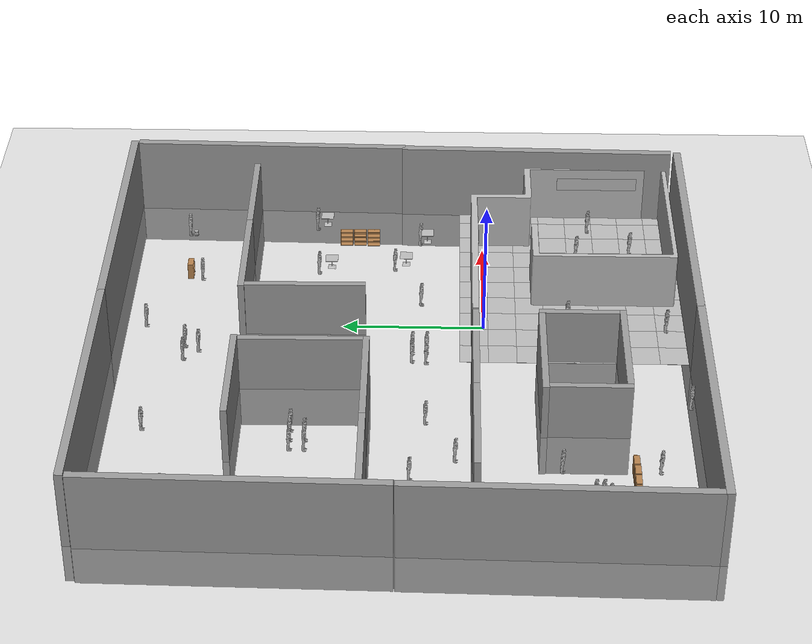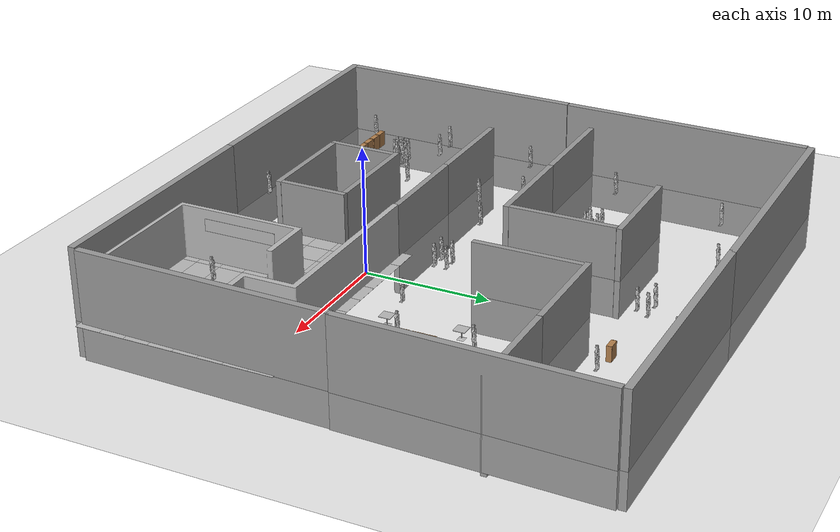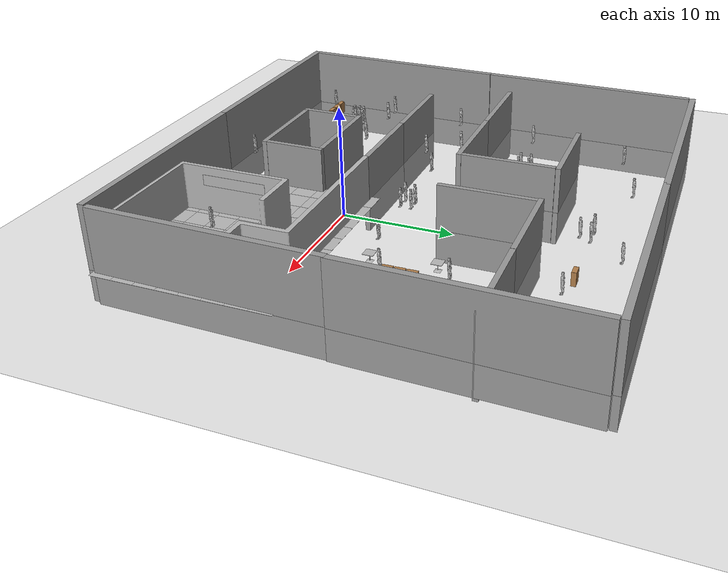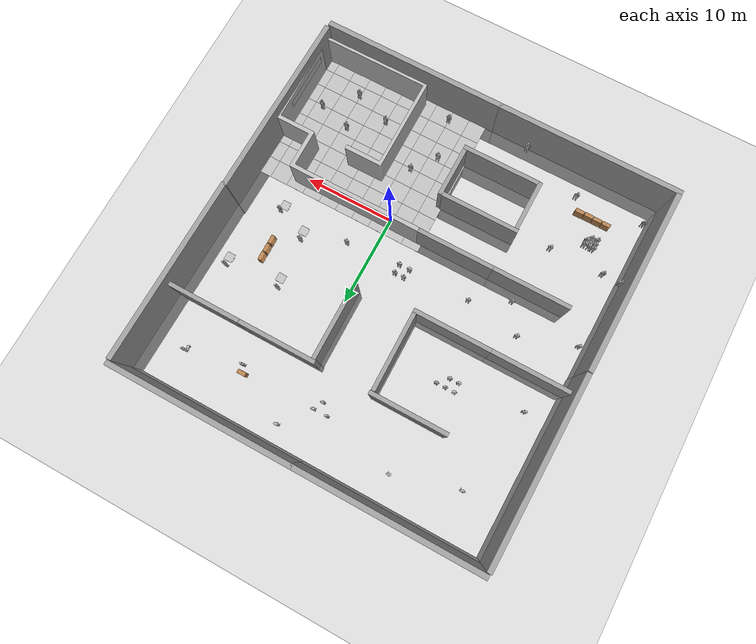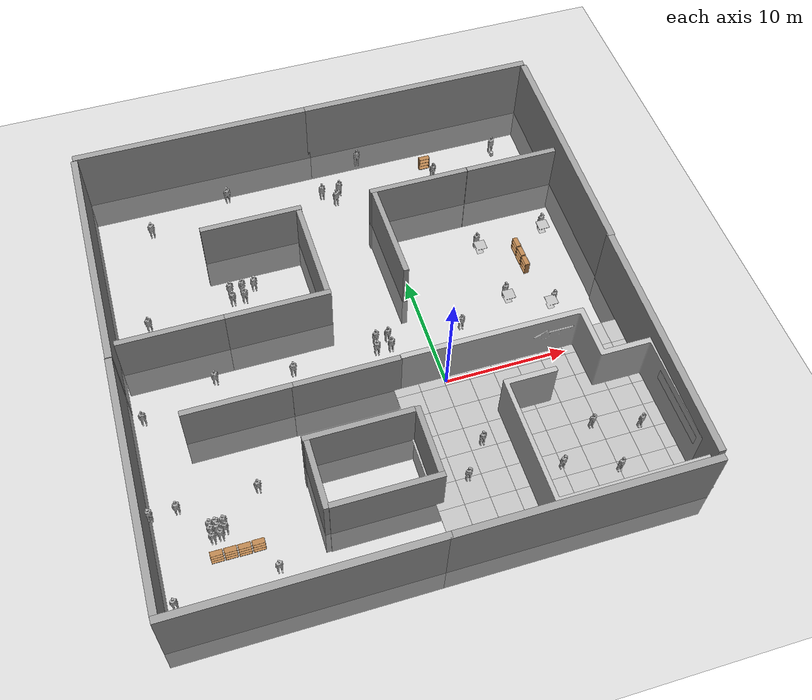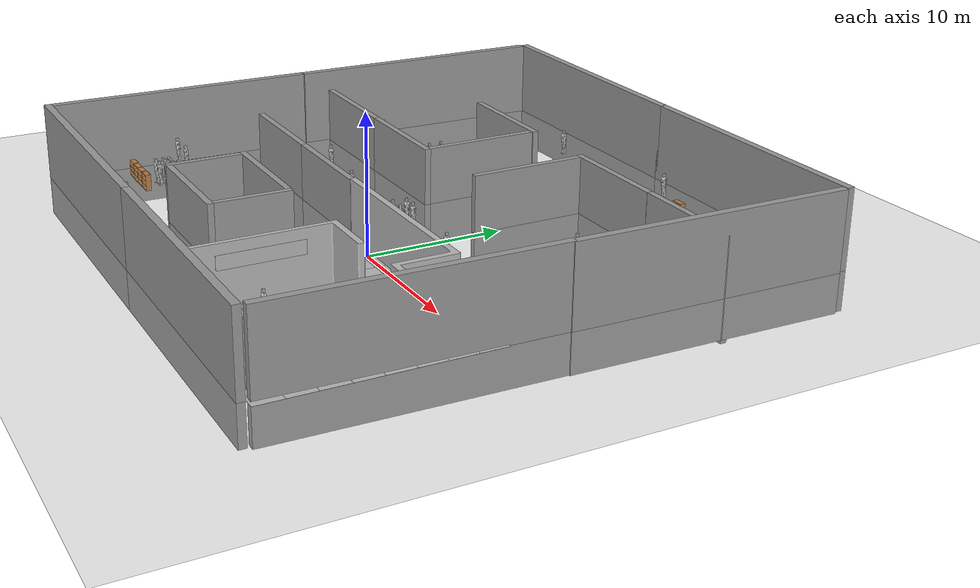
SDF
<?xml version='1.0'?>
<sdf version='1.6'>
  <model name='indoor_environment'>
    <link name='link_1'>
      <pose frame=''>-7.82143 0.660176 0.5 0 -0 0</pose>
      <inertial>
        <mass>28.3649</mass>
        <inertia>
          <ixx>127.542</ixx>
          <ixy>0</ixy>
          <ixz>0</ixz>
          <iyy>299.16</iyy>
          <iyz>0</iyz>
          <izz>172.59</izz>
        </inertia>
        <pose frame=''>0 0 0 0 -0 0</pose>
      </inertial>
      <visual name='visual'>
        <pose frame=''>0 0 0 0 -0 0</pose>
        <geometry>
          <box>
            <size>8.53288 0.453408 7.33157</size>
          </box>
        </geometry>
        <material>
          <lighting>1</lighting>
          <script>
            <uri>file://media/materials/scripts/gazebo.material</uri>
            <name>Gazebo/Grey</name>
          </script>
          <ambient>0.3 0.3 0.3 1</ambient>
          <diffuse>0.7 0.7 0.7 1</diffuse>
          <specular>0.01 0.01 0.01 1</specular>
          <emissive>0 0 0 1</emissive>
        </material>
        <cast_shadows>1</cast_shadows>
        <transparency>0</transparency>
      </visual>
      <collision name='collision'>
        <laser_retro>0</laser_retro>
        <max_contacts>10</max_contacts>
        <pose frame=''>0 0 0 0 -0 0</pose>
        <geometry>
          <box>
            <size>8.53288 0.453408 7.33157</size>
          </box>
        </geometry>
        <surface>
          <friction>
            <ode>
              <mu>1</mu>
              <mu2>1</mu2>
              <fdir1>0 0 0</fdir1>
              <slip1>0</slip1>
              <slip2>0</slip2>
            </ode>
            <torsional>
              <coefficient>1</coefficient>
              <patch_radius>0</patch_radius>
              <surface_radius>0</surface_radius>
              <use_patch_radius>1</use_patch_radius>
              <ode>
                <slip>0</slip>
              </ode>
            </torsional>
          </friction>
          <bounce>
            <restitution_coefficient>0</restitution_coefficient>
            <threshold>1e+06</threshold>
          </bounce>
          <contact>
            <collide_without_contact>0</collide_without_contact>
            <collide_without_contact_bitmask>1</collide_without_contact_bitmask>
            <collide_bitmask>1</collide_bitmask>
            <ode>
              <soft_cfm>0</soft_cfm>
              <soft_erp>0.2</soft_erp>
              <kp>1e+13</kp>
              <kd>1</kd>
              <max_vel>0.01</max_vel>
              <min_depth>0</min_depth>
            </ode>
            <bullet>
              <split_impulse>1</split_impulse>
              <split_impulse_penetration_threshold>-0.01</split_impulse_penetration_threshold>
              <soft_cfm>0</soft_cfm>
              <soft_erp>0.2</soft_erp>
              <kp>1e+13</kp>
              <kd>1</kd>
            </bullet>
          </contact>
        </surface>
      </collision>
    </link>
    <link name='link_1_clone'>
      <pose frame=''>-8.22159 -3.89518 0.5 0 -0 0</pose>
      <inertial>
        <mass>28.3649</mass>
        <inertia>
          <ixx>127.542</ixx>
          <ixy>0</ixy>
          <ixz>0</ixz>
          <iyy>299.16</iyy>
          <iyz>0</iyz>
          <izz>172.59</izz>
        </inertia>
        <pose frame=''>0 0 0 0 -0 0</pose>
      </inertial>
      <visual name='visual'>
        <pose frame=''>0 0 0 0 -0 0</pose>
        <geometry>
          <box>
            <size>8.53288 0.453408 7.33157</size>
          </box>
        </geometry>
        <material>
          <lighting>1</lighting>
          <script>
            <uri>file://media/materials/scripts/gazebo.material</uri>
            <name>Gazebo/Grey</name>
          </script>
          <ambient>0.3 0.3 0.3 1</ambient>
          <diffuse>0.7 0.7 0.7 1</diffuse>
          <specular>0.01 0.01 0.01 1</specular>
          <emissive>0 0 0 1</emissive>
          <shader type='pixel'/>
        </material>
        <cast_shadows>1</cast_shadows>
        <transparency>0</transparency>
      </visual>
      <collision name='collision'>
        <laser_retro>0</laser_retro>
        <max_contacts>10</max_contacts>
        <pose frame=''>0 0 0 0 -0 0</pose>
        <geometry>
          <box>
            <size>8.53288 0.453408 7.33157</size>
          </box>
        </geometry>
        <surface>
          <friction>
            <ode>
              <mu>1</mu>
              <mu2>1</mu2>
              <fdir1>0 0 0</fdir1>
              <slip1>0</slip1>
              <slip2>0</slip2>
            </ode>
            <torsional>
              <coefficient>1</coefficient>
              <patch_radius>0</patch_radius>
              <surface_radius>0</surface_radius>
              <use_patch_radius>1</use_patch_radius>
              <ode>
                <slip>0</slip>
              </ode>
            </torsional>
          </friction>
          <bounce>
            <restitution_coefficient>0</restitution_coefficient>
            <threshold>1e+06</threshold>
          </bounce>
          <contact>
            <collide_without_contact>0</collide_without_contact>
            <collide_without_contact_bitmask>1</collide_without_contact_bitmask>
            <collide_bitmask>1</collide_bitmask>
            <ode>
              <soft_cfm>0</soft_cfm>
              <soft_erp>0.2</soft_erp>
              <kp>1e+13</kp>
              <kd>1</kd>
              <max_vel>0.01</max_vel>
              <min_depth>0</min_depth>
            </ode>
            <bullet>
              <split_impulse>1</split_impulse>
              <split_impulse_penetration_threshold>-0.01</split_impulse_penetration_threshold>
              <soft_cfm>0</soft_cfm>
              <soft_erp>0.2</soft_erp>
              <kp>1e+13</kp>
              <kd>1</kd>
            </bullet>
          </contact>
        </surface>
      </collision>
    </link>
    <link name='link_1_clone_0'>
      <pose frame=''>-3.76052 -6.48703 0.5 0 -0 1.56273</pose>
      <inertial>
        <mass>18.4526</mass>
        <inertia>
          <ixx>82.9715</ixx>
          <ixy>0</ixy>
          <ixz>0</ixz>
          <iyy>130.038</iyy>
          <iyz>0</iyz>
          <izz>47.6988</izz>
        </inertia>
        <pose frame=''>0 0 0 0 -0 0</pose>
      </inertial>
      <visual name='visual'>
        <pose frame=''>0 0 0 0 -0 0</pose>
        <geometry>
          <box>
            <size>5.551 0.453408 7.33157</size>
          </box>
        </geometry>
        <material>
          <lighting>1</lighting>
          <script>
            <uri>file://media/materials/scripts/gazebo.material</uri>
            <name>Gazebo/Grey</name>
          </script>
          <ambient>0.3 0.3 0.3 1</ambient>
          <diffuse>0.7 0.7 0.7 1</diffuse>
          <specular>0.01 0.01 0.01 1</specular>
          <emissive>0 0 0 1</emissive>
          <shader type='pixel'/>
        </material>
        <cast_shadows>1</cast_shadows>
        <transparency>0</transparency>
      </visual>
      <collision name='collision'>
        <laser_retro>0</laser_retro>
        <max_contacts>10</max_contacts>
        <pose frame=''>0 0 0 0 -0 0</pose>
        <geometry>
          <box>
            <size>5.551 0.453408 7.33157</size>
          </box>
        </geometry>
        <surface>
          <friction>
            <ode>
              <mu>1</mu>
              <mu2>1</mu2>
              <fdir1>0 0 0</fdir1>
              <slip1>0</slip1>
              <slip2>0</slip2>
            </ode>
            <torsional>
              <coefficient>1</coefficient>
              <patch_radius>0</patch_radius>
              <surface_radius>0</surface_radius>
              <use_patch_radius>1</use_patch_radius>
              <ode>
                <slip>0</slip>
              </ode>
            </torsional>
          </friction>
          <bounce>
            <restitution_coefficient>0</restitution_coefficient>
            <threshold>1e+06</threshold>
          </bounce>
          <contact>
            <collide_without_contact>0</collide_without_contact>
            <collide_without_contact_bitmask>1</collide_without_contact_bitmask>
            <collide_bitmask>1</collide_bitmask>
            <ode>
              <soft_cfm>0</soft_cfm>
              <soft_erp>0.2</soft_erp>
              <kp>1e+13</kp>
              <kd>1</kd>
              <max_vel>0.01</max_vel>
              <min_depth>0</min_depth>
            </ode>
            <bullet>
              <split_impulse>1</split_impulse>
              <split_impulse_penetration_threshold>-0.01</split_impulse_penetration_threshold>
              <soft_cfm>0</soft_cfm>
              <soft_erp>0.2</soft_erp>
              <kp>1e+13</kp>
              <kd>1</kd>
            </bullet>
          </contact>
        </surface>
      </collision>
    </link>
    <link name='link_1_clone_0_clone'>
      <pose frame=''>-12.2216 -6.89518 0.5 0 -0 1.56273</pose>
      <inertial>
        <mass>18.4526</mass>
        <inertia>
          <ixx>82.9715</ixx>
          <ixy>0</ixy>
          <ixz>0</ixz>
          <iyy>130.038</iyy>
          <iyz>0</iyz>
          <izz>47.6988</izz>
        </inertia>
        <pose frame=''>0 0 0 0 -0 0</pose>
      </inertial>
      <visual name='visual'>
        <pose frame=''>0 0 0 0 -0 0</pose>
        <geometry>
          <box>
            <size>5.551 0.453408 7.33157</size>
          </box>
        </geometry>
        <material>
          <lighting>1</lighting>
          <script>
            <uri>file://media/materials/scripts/gazebo.material</uri>
            <name>Gazebo/Grey</name>
          </script>
          <ambient>0.3 0.3 0.3 1</ambient>
          <diffuse>0.7 0.7 0.7 1</diffuse>
          <specular>0.01 0.01 0.01 1</specular>
          <emissive>0 0 0 1</emissive>
          <shader type='pixel'/>
        </material>
        <cast_shadows>1</cast_shadows>
        <transparency>0</transparency>
      </visual>
      <collision name='collision'>
        <laser_retro>0</laser_retro>
        <max_contacts>10</max_contacts>
        <pose frame=''>0 0 0 0 -0 0</pose>
        <geometry>
          <box>
            <size>5.551 0.453408 7.33157</size>
          </box>
        </geometry>
        <surface>
          <friction>
            <ode>
              <mu>1</mu>
              <mu2>1</mu2>
              <fdir1>0 0 0</fdir1>
              <slip1>0</slip1>
              <slip2>0</slip2>
            </ode>
            <torsional>
              <coefficient>1</coefficient>
              <patch_radius>0</patch_radius>
              <surface_radius>0</surface_radius>
              <use_patch_radius>1</use_patch_radius>
              <ode>
                <slip>0</slip>
              </ode>
            </torsional>
          </friction>
          <bounce>
            <restitution_coefficient>0</restitution_coefficient>
            <threshold>1e+06</threshold>
          </bounce>
          <contact>
            <collide_without_contact>0</collide_without_contact>
            <collide_without_contact_bitmask>1</collide_without_contact_bitmask>
            <collide_bitmask>1</collide_bitmask>
            <ode>
              <soft_cfm>0</soft_cfm>
              <soft_erp>0.2</soft_erp>
              <kp>1e+13</kp>
              <kd>1</kd>
              <max_vel>0.01</max_vel>
              <min_depth>0</min_depth>
            </ode>
            <bullet>
              <split_impulse>1</split_impulse>
              <split_impulse_penetration_threshold>-0.01</split_impulse_penetration_threshold>
              <soft_cfm>0</soft_cfm>
              <soft_erp>0.2</soft_erp>
              <kp>1e+13</kp>
              <kd>1</kd>
            </bullet>
          </contact>
        </surface>
      </collision>
    </link>
    <link name='link_1_clone_1'>
      <pose frame=''>11.7784 17.1048 0.5 0 -0 0</pose>
      <inertial>
        <mass>28.3649</mass>
        <inertia>
          <ixx>127.542</ixx>
          <ixy>0</ixy>
          <ixz>0</ixz>
          <iyy>299.16</iyy>
          <iyz>0</iyz>
          <izz>172.59</izz>
        </inertia>
        <pose frame=''>0 0 0 0 -0 0</pose>
      </inertial>
      <visual name='visual'>
        <pose frame=''>0 0 0 0 -0 0</pose>
        <geometry>
          <box>
            <size>8.53288 0.453408 7.33157</size>
          </box>
        </geometry>
        <material>
          <lighting>1</lighting>
          <script>
            <uri>file://media/materials/scripts/gazebo.material</uri>
            <name>Gazebo/Grey</name>
          </script>
          <ambient>0.3 0.3 0.3 1</ambient>
          <diffuse>0.7 0.7 0.7 1</diffuse>
          <specular>0.01 0.01 0.01 1</specular>
          <emissive>0 0 0 1</emissive>
          <shader type='pixel'/>
        </material>
        <cast_shadows>1</cast_shadows>
        <transparency>0</transparency>
      </visual>
      <collision name='collision'>
        <laser_retro>0</laser_retro>
        <max_contacts>10</max_contacts>
        <pose frame=''>0 0 0 0 -0 0</pose>
        <geometry>
          <box>
            <size>8.53288 0.453408 7.33157</size>
          </box>
        </geometry>
        <surface>
          <friction>
            <ode>
              <mu>1</mu>
              <mu2>1</mu2>
              <fdir1>0 0 0</fdir1>
              <slip1>0</slip1>
              <slip2>0</slip2>
            </ode>
            <torsional>
              <coefficient>1</coefficient>
              <patch_radius>0</patch_radius>
              <surface_radius>0</surface_radius>
              <use_patch_radius>1</use_patch_radius>
              <ode>
                <slip>0</slip>
              </ode>
            </torsional>
          </friction>
          <bounce>
            <restitution_coefficient>0</restitution_coefficient>
            <threshold>1e+06</threshold>
          </bounce>
          <contact>
            <collide_without_contact>0</collide_without_contact>
            <collide_without_contact_bitmask>1</collide_without_contact_bitmask>
            <collide_bitmask>1</collide_bitmask>
            <ode>
              <soft_cfm>0</soft_cfm>
              <soft_erp>0.2</soft_erp>
              <kp>1e+13</kp>
              <kd>1</kd>
              <max_vel>0.01</max_vel>
              <min_depth>0</min_depth>
            </ode>
            <bullet>
              <split_impulse>1</split_impulse>
              <split_impulse_penetration_threshold>-0.01</split_impulse_penetration_threshold>
              <soft_cfm>0</soft_cfm>
              <soft_erp>0.2</soft_erp>
              <kp>1e+13</kp>
              <kd>1</kd>
            </bullet>
          </contact>
        </surface>
      </collision>
    </link>
    <link name='link_1_clone_2'>
      <pose frame=''>3.21873 17.1048 0.5 0 -0 0</pose>
      <inertial>
        <mass>28.3649</mass>
        <inertia>
          <ixx>127.542</ixx>
          <ixy>0</ixy>
          <ixz>0</ixz>
          <iyy>299.16</iyy>
          <iyz>0</iyz>
          <izz>172.59</izz>
        </inertia>
        <pose frame=''>0 0 0 0 -0 0</pose>
      </inertial>
      <visual name='visual'>
        <pose frame=''>0 0 0 0 -0 0</pose>
        <geometry>
          <box>
            <size>8.53288 0.453408 7.33157</size>
          </box>
        </geometry>
        <material>
          <lighting>1</lighting>
          <script>
            <uri>file://media/materials/scripts/gazebo.material</uri>
            <name>Gazebo/Grey</name>
          </script>
          <ambient>0.3 0.3 0.3 1</ambient>
          <diffuse>0.7 0.7 0.7 1</diffuse>
          <specular>0.01 0.01 0.01 1</specular>
          <emissive>0 0 0 1</emissive>
          <shader type='pixel'/>
        </material>
        <cast_shadows>1</cast_shadows>
        <transparency>0</transparency>
      </visual>
      <collision name='collision'>
        <laser_retro>0</laser_retro>
        <max_contacts>10</max_contacts>
        <pose frame=''>0 0 0 0 -0 0</pose>
        <geometry>
          <box>
            <size>8.53288 0.453408 7.33157</size>
          </box>
        </geometry>
        <surface>
          <friction>
            <ode>
              <mu>1</mu>
              <mu2>1</mu2>
              <fdir1>0 0 0</fdir1>
              <slip1>0</slip1>
              <slip2>0</slip2>
            </ode>
            <torsional>
              <coefficient>1</coefficient>
              <patch_radius>0</patch_radius>
              <surface_radius>0</surface_radius>
              <use_patch_radius>1</use_patch_radius>
              <ode>
                <slip>0</slip>
              </ode>
            </torsional>
          </friction>
          <bounce>
            <restitution_coefficient>0</restitution_coefficient>
            <threshold>1e+06</threshold>
          </bounce>
          <contact>
            <collide_without_contact>0</collide_without_contact>
            <collide_without_contact_bitmask>1</collide_without_contact_bitmask>
            <collide_bitmask>1</collide_bitmask>
            <ode>
              <soft_cfm>0</soft_cfm>
              <soft_erp>0.2</soft_erp>
              <kp>1e+13</kp>
              <kd>1</kd>
              <max_vel>0.01</max_vel>
              <min_depth>0</min_depth>
            </ode>
            <bullet>
              <split_impulse>1</split_impulse>
              <split_impulse_penetration_threshold>-0.01</split_impulse_penetration_threshold>
              <soft_cfm>0</soft_cfm>
              <soft_erp>0.2</soft_erp>
              <kp>1e+13</kp>
              <kd>1</kd>
            </bullet>
          </contact>
        </surface>
      </collision>
    </link>
    <link name='link_1_clone_2_clone'>
      <pose frame=''>-11.2216 17.1048 0.5 0 -0 0</pose>
      <inertial>
        <mass>28.3649</mass>
        <inertia>
          <ixx>127.542</ixx>
          <ixy>0</ixy>
          <ixz>0</ixz>
          <iyy>299.16</iyy>
          <iyz>0</iyz>
          <izz>172.59</izz>
        </inertia>
        <pose frame=''>0 0 0 0 -0 0</pose>
      </inertial>
      <visual name='visual'>
        <pose frame=''>0 0 0 0 -0 0</pose>
        <geometry>
          <box>
            <size>8.53288 0.453408 7.33157</size>
          </box>
        </geometry>
        <material>
          <lighting>1</lighting>
          <script>
            <uri>file://media/materials/scripts/gazebo.material</uri>
            <name>Gazebo/Grey</name>
          </script>
          <ambient>0.3 0.3 0.3 1</ambient>
          <diffuse>0.7 0.7 0.7 1</diffuse>
          <specular>0.01 0.01 0.01 1</specular>
          <emissive>0 0 0 1</emissive>
          <shader type='pixel'/>
        </material>
        <cast_shadows>1</cast_shadows>
        <transparency>0</transparency>
      </visual>
      <collision name='collision'>
        <laser_retro>0</laser_retro>
        <max_contacts>10</max_contacts>
        <pose frame=''>0 0 0 0 -0 0</pose>
        <geometry>
          <box>
            <size>8.53288 0.453408 7.33157</size>
          </box>
        </geometry>
        <surface>
          <friction>
            <ode>
              <mu>1</mu>
              <mu2>1</mu2>
              <fdir1>0 0 0</fdir1>
              <slip1>0</slip1>
              <slip2>0</slip2>
            </ode>
            <torsional>
              <coefficient>1</coefficient>
              <patch_radius>0</patch_radius>
              <surface_radius>0</surface_radius>
              <use_patch_radius>1</use_patch_radius>
              <ode>
                <slip>0</slip>
              </ode>
            </torsional>
          </friction>
          <bounce>
            <restitution_coefficient>0</restitution_coefficient>
            <threshold>1e+06</threshold>
          </bounce>
          <contact>
            <collide_without_contact>0</collide_without_contact>
            <collide_without_contact_bitmask>1</collide_without_contact_bitmask>
            <collide_bitmask>1</collide_bitmask>
            <ode>
              <soft_cfm>0</soft_cfm>
              <soft_erp>0.2</soft_erp>
              <kp>1e+13</kp>
              <kd>1</kd>
              <max_vel>0.01</max_vel>
              <min_depth>0</min_depth>
            </ode>
            <bullet>
              <split_impulse>1</split_impulse>
              <split_impulse_penetration_threshold>-0.01</split_impulse_penetration_threshold>
              <soft_cfm>0</soft_cfm>
              <soft_erp>0.2</soft_erp>
              <kp>1e+13</kp>
              <kd>1</kd>
            </bullet>
          </contact>
        </surface>
      </collision>
    </link>
    <link name='link_1_clone_2_clone_0'>
      <pose frame=''>-11.2216 8.10482 0.5 0 -0 0</pose>
      <inertial>
        <mass>28.3649</mass>
        <inertia>
          <ixx>127.542</ixx>
          <ixy>0</ixy>
          <ixz>0</ixz>
          <iyy>299.16</iyy>
          <iyz>0</iyz>
          <izz>172.59</izz>
        </inertia>
        <pose frame=''>0 0 0 0 -0 0</pose>
      </inertial>
      <visual name='visual'>
        <pose frame=''>0 0 0 0 -0 0</pose>
        <geometry>
          <box>
            <size>8.53288 0.453408 7.33157</size>
          </box>
        </geometry>
        <material>
          <lighting>1</lighting>
          <script>
            <uri>file://media/materials/scripts/gazebo.material</uri>
            <name>Gazebo/Grey</name>
          </script>
          <ambient>0.3 0.3 0.3 1</ambient>
          <diffuse>0.7 0.7 0.7 1</diffuse>
          <specular>0.01 0.01 0.01 1</specular>
          <emissive>0 0 0 1</emissive>
          <shader type='pixel'/>
        </material>
        <cast_shadows>1</cast_shadows>
        <transparency>0</transparency>
      </visual>
      <collision name='collision'>
        <laser_retro>0</laser_retro>
        <max_contacts>10</max_contacts>
        <pose frame=''>0 0 0 0 -0 0</pose>
        <geometry>
          <box>
            <size>8.53288 0.453408 7.33157</size>
          </box>
        </geometry>
        <surface>
          <friction>
            <ode>
              <mu>1</mu>
              <mu2>1</mu2>
              <fdir1>0 0 0</fdir1>
              <slip1>0</slip1>
              <slip2>0</slip2>
            </ode>
            <torsional>
              <coefficient>1</coefficient>
              <patch_radius>0</patch_radius>
              <surface_radius>0</surface_radius>
              <use_patch_radius>1</use_patch_radius>
              <ode>
                <slip>0</slip>
              </ode>
            </torsional>
          </friction>
          <bounce>
            <restitution_coefficient>0</restitution_coefficient>
            <threshold>1e+06</threshold>
          </bounce>
          <contact>
            <collide_without_contact>0</collide_without_contact>
            <collide_without_contact_bitmask>1</collide_without_contact_bitmask>
            <collide_bitmask>1</collide_bitmask>
            <ode>
              <soft_cfm>0</soft_cfm>
              <soft_erp>0.2</soft_erp>
              <kp>1e+13</kp>
              <kd>1</kd>
              <max_vel>0.01</max_vel>
              <min_depth>0</min_depth>
            </ode>
            <bullet>
              <split_impulse>1</split_impulse>
              <split_impulse_penetration_threshold>-0.01</split_impulse_penetration_threshold>
              <soft_cfm>0</soft_cfm>
              <soft_erp>0.2</soft_erp>
              <kp>1e+13</kp>
              <kd>1</kd>
            </bullet>
          </contact>
        </surface>
      </collision>
    </link>
    <link name='link_1_clone_2_clone_1'>
      <pose frame=''>-19.7276 8.10482 0.5 0 -0 0</pose>
      <inertial>
        <mass>28.3649</mass>
        <inertia>
          <ixx>127.542</ixx>
          <ixy>0</ixy>
          <ixz>0</ixz>
          <iyy>299.16</iyy>
          <iyz>0</iyz>
          <izz>172.59</izz>
        </inertia>
        <pose frame=''>0 0 0 0 -0 0</pose>
      </inertial>
      <visual name='visual'>
        <pose frame=''>0 0 0 0 -0 0</pose>
        <geometry>
          <box>
            <size>8.53288 0.453408 7.33157</size>
          </box>
        </geometry>
        <material>
          <lighting>1</lighting>
          <script>
            <uri>file://media/materials/scripts/gazebo.material</uri>
            <name>Gazebo/Grey</name>
          </script>
          <ambient>0.3 0.3 0.3 1</ambient>
          <diffuse>0.7 0.7 0.7 1</diffuse>
          <specular>0.01 0.01 0.01 1</specular>
          <emissive>0 0 0 1</emissive>
          <shader type='pixel'/>
        </material>
        <cast_shadows>1</cast_shadows>
        <transparency>0</transparency>
      </visual>
      <collision name='collision'>
        <laser_retro>0</laser_retro>
        <max_contacts>10</max_contacts>
        <pose frame=''>0 0 0 0 -0 0</pose>
        <geometry>
          <box>
            <size>8.53288 0.453408 7.33157</size>
          </box>
        </geometry>
        <surface>
          <friction>
            <ode>
              <mu>1</mu>
              <mu2>1</mu2>
              <fdir1>0 0 0</fdir1>
              <slip1>0</slip1>
              <slip2>0</slip2>
            </ode>
            <torsional>
              <coefficient>1</coefficient>
              <patch_radius>0</patch_radius>
              <surface_radius>0</surface_radius>
              <use_patch_radius>1</use_patch_radius>
              <ode>
                <slip>0</slip>
              </ode>
            </torsional>
          </friction>
          <bounce>
            <restitution_coefficient>0</restitution_coefficient>
            <threshold>1e+06</threshold>
          </bounce>
          <contact>
            <collide_without_contact>0</collide_without_contact>
            <collide_without_contact_bitmask>1</collide_without_contact_bitmask>
            <collide_bitmask>1</collide_bitmask>
            <ode>
              <soft_cfm>0</soft_cfm>
              <soft_erp>0.2</soft_erp>
              <kp>1e+13</kp>
              <kd>1</kd>
              <max_vel>0.01</max_vel>
              <min_depth>0</min_depth>
            </ode>
            <bullet>
              <split_impulse>1</split_impulse>
              <split_impulse_penetration_threshold>-0.01</split_impulse_penetration_threshold>
              <soft_cfm>0</soft_cfm>
              <soft_erp>0.2</soft_erp>
              <kp>1e+13</kp>
              <kd>1</kd>
            </bullet>
          </contact>
        </surface>
      </collision>
    </link>
    <link name='link_1_clone_2_clone_2'>
      <pose frame=''>-16.2216 0.663889 0.5 0 -0 0</pose>
      <inertial>
        <mass>28.3649</mass>
        <inertia>
          <ixx>127.542</ixx>
          <ixy>0</ixy>
          <ixz>0</ixz>
          <iyy>299.16</iyy>
          <iyz>0</iyz>
          <izz>172.59</izz>
        </inertia>
        <pose frame=''>0 0 0 0 -0 0</pose>
      </inertial>
      <visual name='visual'>
        <pose frame=''>0 0 0 0 -0 0</pose>
        <geometry>
          <box>
            <size>8.53288 0.453408 7.33157</size>
          </box>
        </geometry>
        <material>
          <lighting>1</lighting>
          <script>
            <uri>file://media/materials/scripts/gazebo.material</uri>
            <name>Gazebo/Grey</name>
          </script>
          <ambient>0.3 0.3 0.3 1</ambient>
          <diffuse>0.7 0.7 0.7 1</diffuse>
          <specular>0.01 0.01 0.01 1</specular>
          <emissive>0 0 0 1</emissive>
          <shader type='pixel'/>
        </material>
        <cast_shadows>1</cast_shadows>
        <transparency>0</transparency>
      </visual>
      <collision name='collision'>
        <laser_retro>0</laser_retro>
        <max_contacts>10</max_contacts>
        <pose frame=''>0 0 0 0 -0 0</pose>
        <geometry>
          <box>
            <size>8.53288 0.453408 7.33157</size>
          </box>
        </geometry>
        <surface>
          <friction>
            <ode>
              <mu>1</mu>
              <mu2>1</mu2>
              <fdir1>0 0 0</fdir1>
              <slip1>0</slip1>
              <slip2>0</slip2>
            </ode>
            <torsional>
              <coefficient>1</coefficient>
              <patch_radius>0</patch_radius>
              <surface_radius>0</surface_radius>
              <use_patch_radius>1</use_patch_radius>
              <ode>
                <slip>0</slip>
              </ode>
            </torsional>
          </friction>
          <bounce>
            <restitution_coefficient>0</restitution_coefficient>
            <threshold>1e+06</threshold>
          </bounce>
          <contact>
            <collide_without_contact>0</collide_without_contact>
            <collide_without_contact_bitmask>1</collide_without_contact_bitmask>
            <collide_bitmask>1</collide_bitmask>
            <ode>
              <soft_cfm>0</soft_cfm>
              <soft_erp>0.2</soft_erp>
              <kp>1e+13</kp>
              <kd>1</kd>
              <max_vel>0.01</max_vel>
              <min_depth>0</min_depth>
            </ode>
            <bullet>
              <split_impulse>1</split_impulse>
              <split_impulse_penetration_threshold>-0.01</split_impulse_penetration_threshold>
              <soft_cfm>0</soft_cfm>
              <soft_erp>0.2</soft_erp>
              <kp>1e+13</kp>
              <kd>1</kd>
            </bullet>
          </contact>
        </surface>
      </collision>
    </link>
    <link name='link_1_clone_3'>
      <pose frame=''>-0.698625 12.6258 0.5 0 0 -1.56558</pose>
      <inertial>
        <mass>28.3649</mass>
        <inertia>
          <ixx>127.542</ixx>
          <ixy>0</ixy>
          <ixz>0</ixz>
          <iyy>299.16</iyy>
          <iyz>0</iyz>
          <izz>172.59</izz>
        </inertia>
        <pose frame=''>0 0 0 0 -0 0</pose>
      </inertial>
      <visual name='visual'>
        <pose frame=''>0 0 0 0 -0 0</pose>
        <geometry>
          <box>
            <size>8.53288 0.453408 7.33157</size>
          </box>
        </geometry>
        <material>
          <lighting>1</lighting>
          <script>
            <uri>file://media/materials/scripts/gazebo.material</uri>
            <name>Gazebo/Grey</name>
          </script>
          <ambient>0.3 0.3 0.3 1</ambient>
          <diffuse>0.7 0.7 0.7 1</diffuse>
          <specular>0.01 0.01 0.01 1</specular>
          <emissive>0 0 0 1</emissive>
          <shader type='pixel'/>
        </material>
        <cast_shadows>1</cast_shadows>
        <transparency>0</transparency>
      </visual>
      <collision name='collision'>
        <laser_retro>0</laser_retro>
        <max_contacts>10</max_contacts>
        <pose frame=''>0 0 0 0 -0 0</pose>
        <geometry>
          <box>
            <size>8.53288 0.453408 7.33157</size>
          </box>
        </geometry>
        <surface>
          <friction>
            <ode>
              <mu>1</mu>
              <mu2>1</mu2>
              <fdir1>0 0 0</fdir1>
              <slip1>0</slip1>
              <slip2>0</slip2>
            </ode>
            <torsional>
              <coefficient>1</coefficient>
              <patch_radius>0</patch_radius>
              <surface_radius>0</surface_radius>
              <use_patch_radius>1</use_patch_radius>
              <ode>
                <slip>0</slip>
              </ode>
            </torsional>
          </friction>
          <bounce>
            <restitution_coefficient>0</restitution_coefficient>
            <threshold>1e+06</threshold>
          </bounce>
          <contact>
            <collide_without_contact>0</collide_without_contact>
            <collide_without_contact_bitmask>1</collide_without_contact_bitmask>
            <collide_bitmask>1</collide_bitmask>
            <ode>
              <soft_cfm>0</soft_cfm>
              <soft_erp>0.2</soft_erp>
              <kp>1e+13</kp>
              <kd>1</kd>
              <max_vel>0.01</max_vel>
              <min_depth>0</min_depth>
            </ode>
            <bullet>
              <split_impulse>1</split_impulse>
              <split_impulse_penetration_threshold>-0.01</split_impulse_penetration_threshold>
              <soft_cfm>0</soft_cfm>
              <soft_erp>0.2</soft_erp>
              <kp>1e+13</kp>
              <kd>1</kd>
            </bullet>
          </contact>
        </surface>
      </collision>
    </link>
    <link name='link_1_clone_3_clone'>
      <pose frame=''>-7.22159 12.5786 0.5 0 0 -1.56558</pose>
      <inertial>
        <mass>28.3649</mass>
        <inertia>
          <ixx>127.542</ixx>
          <ixy>0</ixy>
          <ixz>0</ixz>
          <iyy>299.16</iyy>
          <iyz>0</iyz>
          <izz>172.59</izz>
        </inertia>
        <pose frame=''>0 0 0 0 -0 0</pose>
      </inertial>
      <visual name='visual'>
        <pose frame=''>0 0 0 0 -0 0</pose>
        <geometry>
          <box>
            <size>8.53288 0.453408 7.33157</size>
          </box>
        </geometry>
        <material>
          <lighting>1</lighting>
          <script>
            <uri>file://media/materials/scripts/gazebo.material</uri>
            <name>Gazebo/Grey</name>
          </script>
          <ambient>0.3 0.3 0.3 1</ambient>
          <diffuse>0.7 0.7 0.7 1</diffuse>
          <specular>0.01 0.01 0.01 1</specular>
          <emissive>0 0 0 1</emissive>
          <shader type='pixel'/>
        </material>
        <cast_shadows>1</cast_shadows>
        <transparency>0</transparency>
      </visual>
      <collision name='collision'>
        <laser_retro>0</laser_retro>
        <max_contacts>10</max_contacts>
        <pose frame=''>0 0 0 0 -0 0</pose>
        <geometry>
          <box>
            <size>8.53288 0.453408 7.33157</size>
          </box>
        </geometry>
        <surface>
          <friction>
            <ode>
              <mu>1</mu>
              <mu2>1</mu2>
              <fdir1>0 0 0</fdir1>
              <slip1>0</slip1>
              <slip2>0</slip2>
            </ode>
            <torsional>
              <coefficient>1</coefficient>
              <patch_radius>0</patch_radius>
              <surface_radius>0</surface_radius>
              <use_patch_radius>1</use_patch_radius>
              <ode>
                <slip>0</slip>
              </ode>
            </torsional>
          </friction>
          <bounce>
            <restitution_coefficient>0</restitution_coefficient>
            <threshold>1e+06</threshold>
          </bounce>
          <contact>
            <collide_without_contact>0</collide_without_contact>
            <collide_without_contact_bitmask>1</collide_without_contact_bitmask>
            <collide_bitmask>1</collide_bitmask>
            <ode>
              <soft_cfm>0</soft_cfm>
              <soft_erp>0.2</soft_erp>
              <kp>1e+13</kp>
              <kd>1</kd>
              <max_vel>0.01</max_vel>
              <min_depth>0</min_depth>
            </ode>
            <bullet>
              <split_impulse>1</split_impulse>
              <split_impulse_penetration_threshold>-0.01</split_impulse_penetration_threshold>
              <soft_cfm>0</soft_cfm>
              <soft_erp>0.2</soft_erp>
              <kp>1e+13</kp>
              <kd>1</kd>
            </bullet>
          </contact>
        </surface>
      </collision>
    </link>
    <link name='link_1_clone_clone'>
      <pose frame=''>-7.80975 -9.48511 0.5 0 -0 0</pose>
      <inertial>
        <mass>28.3649</mass>
        <inertia>
          <ixx>127.542</ixx>
          <ixy>0</ixy>
          <ixz>0</ixz>
          <iyy>299.16</iyy>
          <iyz>0</iyz>
          <izz>172.59</izz>
        </inertia>
        <pose frame=''>0 0 0 0 -0 0</pose>
      </inertial>
      <visual name='visual'>
        <pose frame=''>0 0 0 0 -0 0</pose>
        <geometry>
          <box>
            <size>8.53288 0.453408 7.33157</size>
          </box>
        </geometry>
        <material>
          <lighting>1</lighting>
          <script>
            <uri>file://media/materials/scripts/gazebo.material</uri>
            <name>Gazebo/Grey</name>
          </script>
          <ambient>0.3 0.3 0.3 1</ambient>
          <diffuse>0.7 0.7 0.7 1</diffuse>
          <specular>0.01 0.01 0.01 1</specular>
          <emissive>0 0 0 1</emissive>
          <shader type='pixel'/>
        </material>
        <cast_shadows>1</cast_shadows>
        <transparency>0</transparency>
      </visual>
      <collision name='collision'>
        <laser_retro>0</laser_retro>
        <max_contacts>10</max_contacts>
        <pose frame=''>0 0 0 0 -0 0</pose>
        <geometry>
          <box>
            <size>8.53288 0.453408 7.33157</size>
          </box>
        </geometry>
        <surface>
          <friction>
            <ode>
              <mu>1</mu>
              <mu2>1</mu2>
              <fdir1>0 0 0</fdir1>
              <slip1>0</slip1>
              <slip2>0</slip2>
            </ode>
            <torsional>
              <coefficient>1</coefficient>
              <patch_radius>0</patch_radius>
              <surface_radius>0</surface_radius>
              <use_patch_radius>1</use_patch_radius>
              <ode>
                <slip>0</slip>
              </ode>
            </torsional>
          </friction>
          <bounce>
            <restitution_coefficient>0</restitution_coefficient>
            <threshold>1e+06</threshold>
          </bounce>
          <contact>
            <collide_without_contact>0</collide_without_contact>
            <collide_without_contact_bitmask>1</collide_without_contact_bitmask>
            <collide_bitmask>1</collide_bitmask>
            <ode>
              <soft_cfm>0</soft_cfm>
              <soft_erp>0.2</soft_erp>
              <kp>1e+13</kp>
              <kd>1</kd>
              <max_vel>0.01</max_vel>
              <min_depth>0</min_depth>
            </ode>
            <bullet>
              <split_impulse>1</split_impulse>
              <split_impulse_penetration_threshold>-0.01</split_impulse_penetration_threshold>
              <soft_cfm>0</soft_cfm>
              <soft_erp>0.2</soft_erp>
              <kp>1e+13</kp>
              <kd>1</kd>
            </bullet>
          </contact>
        </surface>
      </collision>
    </link>
    <model name='Starting Pen'>
      <static>1</static>
      <link name='link'>
        <collision name='wall_01'>
          <pose frame=''>-0 0 2.14 0 -0 0</pose>
          <geometry>
            <box>
              <size>12.15 0.31 4.28</size>
            </box>
          </geometry>
        </collision>
        <collision name='wall_02'>
          <pose frame=''>-5.28 14.3205 2.14 0 -0 0</pose>
          <geometry>
            <box>
              <size>14.8 0.46 4.28</size>
            </box>
          </geometry>
        </collision>
        <collision name='wall_03'>
          <pose frame=''>-5.91 5 2.14 0 -0 0</pose>
          <geometry>
            <box>
              <size>0.385 10.3 4.28</size>
            </box>
          </geometry>
        </collision>
        <collision name='wall_04'>
          <pose frame=''>5.91 5.161 2.14 0 -0 0</pose>
          <geometry>
            <box>
              <size>0.385 10.66 4.28</size>
            </box>
          </geometry>
        </collision>
        <collision name='wall_05'>
          <pose frame=''>3.9 10.285 2.14 0 -0 0</pose>
          <geometry>
            <box>
              <size>4.38 0.45 4.28</size>
            </box>
          </geometry>
        </collision>
        <collision name='wall_06'>
          <pose frame=''>-4 9.95 2.14 0 -0 0</pose>
          <geometry>
            <box>
              <size>4.25 0.45 4.28</size>
            </box>
          </geometry>
        </collision>
        <collision name='wall_07'>
          <pose frame=''>1.94 12.3 2.14 0 -0 0</pose>
          <geometry>
            <box>
              <size>0.45 4.5 4.28</size>
            </box>
          </geometry>
        </collision>
        <collision name='wall_arrow'>
          <pose frame=''>-0.232 14.03 2.46 0 -0 0</pose>
          <geometry>
            <box>
              <size>3.33 0.12 1.16</size>
            </box>
          </geometry>
        </collision>
        <collision name='collision_floor'>
          <pose frame=''>-3.21 7.355 0 0 -0 0</pose>
          <geometry>
            <box>
              <size>20 16 0.01</size>
            </box>
          </geometry>
          <surface>
            <friction>
              <ode>
                <mu>100</mu>
                <mu2>50</mu2>
              </ode>
            </friction>
          </surface>
        </collision>
        <visual name='visual_osrf'>
          <pose frame=''>-5.74 4.99 3 0 -0 0</pose>
          <geometry>
            <box>
              <size>0.01 6 1</size>
            </box>
          </geometry>
          <material>
            <script>
              <uri>model://starting_pen/materials/scripts</uri>
              <uri>model://starting_pen/materials/textures</uri>
              <name>StartingPen/OSRF</name>
            </script>
          </material>
        </visual>
        <visual name='visual_osrf_2'>
          <pose frame=''>5.74 4.99 3 0 -0 0</pose>
          <geometry>
            <box>
              <size>0.01 6 1</size>
            </box>
          </geometry>
          <material>
            <script>
              <uri>model://starting_pen/materials/scripts</uri>
              <uri>model://starting_pen/materials/textures</uri>
              <name>StartingPen/OSRF</name>
            </script>
          </material>
        </visual>
        <visual name='visual'>
          <geometry>
            <mesh>
              <uri>model://starting_pen/meshes/starting_pen.dae</uri>
            </mesh>
          </geometry>
        </visual>
        <visual name='visual_floor_0'>
          <pose frame=''>-12.21 0.35 0 0 -0 0</pose>
          <geometry>
            <box>
              <size>2 2 0.01</size>
            </box>
          </geometry>
          <material>
            <script>
              <uri>model://starting_pen/materials/scripts</uri>
              <uri>model://starting_pen/materials/textures</uri>
              <name>StartingPen/Floor</name>
            </script>
          </material>
        </visual>
        <visual name='visual_floor_1'>
          <pose frame=''>-10.21 0.35 0 0 -0 0</pose>
          <geometry>
            <box>
              <size>2 2 0.01</size>
            </box>
          </geometry>
          <material>
            <script>
              <uri>model://starting_pen/materials/scripts</uri>
              <uri>model://starting_pen/materials/textures</uri>
              <name>StartingPen/Floor</name>
            </script>
          </material>
        </visual>
        <visual name='visual_floor_2'>
          <pose frame=''>-8.21 0.35 0 0 -0 0</pose>
          <geometry>
            <box>
              <size>2 2 0.01</size>
            </box>
          </geometry>
          <material>
            <script>
              <uri>model://starting_pen/materials/scripts</uri>
              <uri>model://starting_pen/materials/textures</uri>
              <name>StartingPen/Floor</name>
            </script>
          </material>
        </visual>
        <visual name='visual_floor_3'>
          <pose frame=''>-6.21 0.35 0 0 -0 0</pose>
          <geometry>
            <box>
              <size>2 2 0.01</size>
            </box>
          </geometry>
          <material>
            <script>
              <uri>model://starting_pen/materials/scripts</uri>
              <uri>model://starting_pen/materials/textures</uri>
              <name>StartingPen/Floor</name>
            </script>
          </material>
        </visual>
        <visual name='visual_floor_4'>
          <pose frame=''>-4.21 0.35 0 0 -0 0</pose>
          <geometry>
            <box>
              <size>2 2 0.01</size>
            </box>
          </geometry>
          <material>
            <script>
              <uri>model://starting_pen/materials/scripts</uri>
              <uri>model://starting_pen/materials/textures</uri>
              <name>StartingPen/Floor</name>
            </script>
          </material>
        </visual>
        <visual name='visual_floor_5'>
          <pose frame=''>-2.21 0.35 0 0 -0 0</pose>
          <geometry>
            <box>
              <size>2 2 0.01</size>
            </box>
          </geometry>
          <material>
            <script>
              <uri>model://starting_pen/materials/scripts</uri>
              <uri>model://starting_pen/materials/textures</uri>
              <name>StartingPen/Floor</name>
            </script>
          </material>
        </visual>
        <visual name='visual_floor_6'>
          <pose frame=''>-0.21 0.35 0 0 -0 0</pose>
          <geometry>
            <box>
              <size>2 2 0.01</size>
            </box>
          </geometry>
          <material>
            <script>
              <uri>model://starting_pen/materials/scripts</uri>
              <uri>model://starting_pen/materials/textures</uri>
              <name>StartingPen/Floor</name>
            </script>
          </material>
        </visual>
        <visual name='visual_floor_7'>
          <pose frame=''>1.79 0.35 0 0 -0 1.5707</pose>
          <geometry>
            <box>
              <size>2 2 0.01</size>
            </box>
          </geometry>
          <material>
            <script>
              <uri>model://starting_pen/materials/scripts</uri>
              <uri>model://starting_pen/materials/textures</uri>
              <name>StartingPen/FloorStripped</name>
            </script>
          </material>
        </visual>
        <visual name='visual_floor_8'>
          <pose frame=''>3.79 0.35 0 0 -0 0</pose>
          <geometry>
            <box>
              <size>2 2 0.01</size>
            </box>
          </geometry>
          <material>
            <script>
              <uri>model://starting_pen/materials/scripts</uri>
              <uri>model://starting_pen/materials/textures</uri>
              <name>StartingPen/Floor</name>
            </script>
          </material>
        </visual>
        <visual name='visual_floor_9'>
          <pose frame=''>5.79 0.35 0 0 -0 0</pose>
          <geometry>
            <box>
              <size>2 2 0.01</size>
            </box>
          </geometry>
          <material>
            <script>
              <uri>model://starting_pen/materials/scripts</uri>
              <uri>model://starting_pen/materials/textures</uri>
              <name>StartingPen/Floor</name>
            </script>
          </material>
        </visual>
        <visual name='visual_floor_10'>
          <pose frame=''>-12.21 2.35 0 0 -0 1.5707</pose>
          <geometry>
            <box>
              <size>2 2 0.01</size>
            </box>
          </geometry>
          <material>
            <script>
              <uri>model://starting_pen/materials/scripts</uri>
              <uri>model://starting_pen/materials/textures</uri>
              <name>StartingPen/FloorStripped</name>
            </script>
          </material>
        </visual>
        <visual name='visual_floor_11'>
          <pose frame=''>-10.21 2.35 0 0 -0 0</pose>
          <geometry>
            <box>
              <size>2 2 0.01</size>
            </box>
          </geometry>
          <material>
            <script>
              <uri>model://starting_pen/materials/scripts</uri>
              <uri>model://starting_pen/materials/textures</uri>
              <name>StartingPen/Floor</name>
            </script>
          </material>
        </visual>
        <visual name='visual_floor_12'>
          <pose frame=''>-8.21 2.35 0 0 -0 0</pose>
          <geometry>
            <box>
              <size>2 2 0.01</size>
            </box>
          </geometry>
          <material>
            <script>
              <uri>model://starting_pen/materials/scripts</uri>
              <uri>model://starting_pen/materials/textures</uri>
              <name>StartingPen/Floor</name>
            </script>
          </material>
        </visual>
        <visual name='visual_floor_13'>
          <pose frame=''>-6.21 2.35 0 0 -0 0</pose>
          <geometry>
            <box>
              <size>2 2 0.01</size>
            </box>
          </geometry>
          <material>
            <script>
              <uri>model://starting_pen/materials/scripts</uri>
              <uri>model://starting_pen/materials/textures</uri>
              <name>StartingPen/Floor</name>
            </script>
          </material>
        </visual>
        <visual name='visual_floor_14'>
          <pose frame=''>-4.21 2.35 0 0 -0 0</pose>
          <geometry>
            <box>
              <size>2 2 0.01</size>
            </box>
          </geometry>
          <material>
            <script>
              <uri>model://starting_pen/materials/scripts</uri>
              <uri>model://starting_pen/materials/textures</uri>
              <name>StartingPen/Floor</name>
            </script>
          </material>
        </visual>
        <visual name='visual_floor_15'>
          <pose frame=''>-2.21 2.35 0 0 -0 0</pose>
          <geometry>
            <box>
              <size>2 2 0.01</size>
            </box>
          </geometry>
          <material>
            <script>
              <uri>model://starting_pen/materials/scripts</uri>
              <uri>model://starting_pen/materials/textures</uri>
              <name>StartingPen/Floor</name>
            </script>
          </material>
        </visual>
        <visual name='visual_floor_16'>
          <pose frame=''>-0.21 2.35 0 0 -0 1.5707</pose>
          <geometry>
            <box>
              <size>2 2 0.01</size>
            </box>
          </geometry>
          <material>
            <script>
              <uri>model://starting_pen/materials/scripts</uri>
              <uri>model://starting_pen/materials/textures</uri>
              <name>StartingPen/FloorStripped</name>
            </script>
          </material>
        </visual>
        <visual name='visual_floor_17'>
          <pose frame=''>1.79 2.35 0 0 -0 1.5707</pose>
          <geometry>
            <box>
              <size>2 2 0.01</size>
            </box>
          </geometry>
          <material>
            <script>
              <uri>model://starting_pen/materials/scripts</uri>
              <uri>model://starting_pen/materials/textures</uri>
              <name>StartingPen/Floor</name>
            </script>
          </material>
        </visual>
        <visual name='visual_floor_18'>
          <pose frame=''>3.79 2.35 0 0 -0 0</pose>
          <geometry>
            <box>
              <size>2 2 0.01</size>
            </box>
          </geometry>
          <material>
            <script>
              <uri>model://starting_pen/materials/scripts</uri>
              <uri>model://starting_pen/materials/textures</uri>
              <name>StartingPen/Floor</name>
            </script>
          </material>
        </visual>
        <visual name='visual_floor_19'>
          <pose frame=''>5.79 2.35 0 0 -0 0</pose>
          <geometry>
            <box>
              <size>2 2 0.01</size>
            </box>
          </geometry>
          <material>
            <script>
              <uri>model://starting_pen/materials/scripts</uri>
              <uri>model://starting_pen/materials/textures</uri>
              <name>StartingPen/Floor</name>
            </script>
          </material>
        </visual>
        <visual name='visual_floor_20'>
          <pose frame=''>-12.21 4.35 0 0 -0 0</pose>
          <geometry>
            <box>
              <size>2 2 0.01</size>
            </box>
          </geometry>
          <material>
            <script>
              <uri>model://starting_pen/materials/scripts</uri>
              <uri>model://starting_pen/materials/textures</uri>
              <name>StartingPen/Floor</name>
            </script>
          </material>
        </visual>
        <visual name='visual_floor_21'>
          <pose frame=''>-10.21 4.35 0 0 -0 0</pose>
          <geometry>
            <box>
              <size>2 2 0.01</size>
            </box>
          </geometry>
          <material>
            <script>
              <uri>model://starting_pen/materials/scripts</uri>
              <uri>model://starting_pen/materials/textures</uri>
              <name>StartingPen/Floor</name>
            </script>
          </material>
        </visual>
        <visual name='visual_floor_22'>
          <pose frame=''>-8.21 4.35 0 0 -0 1.5707</pose>
          <geometry>
            <box>
              <size>2 2 0.01</size>
            </box>
          </geometry>
          <material>
            <script>
              <uri>model://starting_pen/materials/scripts</uri>
              <uri>model://starting_pen/materials/textures</uri>
              <name>StartingPen/FloorStripped</name>
            </script>
          </material>
        </visual>
        <visual name='visual_floor_23'>
          <pose frame=''>-6.21 4.35 0 0 -0 0</pose>
          <geometry>
            <box>
              <size>2 2 0.01</size>
            </box>
          </geometry>
          <material>
            <script>
              <uri>model://starting_pen/materials/scripts</uri>
              <uri>model://starting_pen/materials/textures</uri>
              <name>StartingPen/Floor</name>
            </script>
          </material>
        </visual>
        <visual name='visual_floor_24'>
          <pose frame=''>-4.21 4.35 0 0 -0 0</pose>
          <geometry>
            <box>
              <size>2 2 0.01</size>
            </box>
          </geometry>
          <material>
            <script>
              <uri>model://starting_pen/materials/scripts</uri>
              <uri>model://starting_pen/materials/textures</uri>
              <name>StartingPen/Floor</name>
            </script>
          </material>
        </visual>
        <visual name='visual_floor_25'>
          <pose frame=''>-2.21 4.35 0 0 -0 0</pose>
          <geometry>
            <box>
              <size>2 2 0.01</size>
            </box>
          </geometry>
          <material>
            <script>
              <uri>model://starting_pen/materials/scripts</uri>
              <uri>model://starting_pen/materials/textures</uri>
              <name>StartingPen/Floor</name>
            </script>
          </material>
        </visual>
        <visual name='visual_floor_26'>
          <pose frame=''>-0.21 4.35 0 0 -0 0</pose>
          <geometry>
            <box>
              <size>2 2 0.01</size>
            </box>
          </geometry>
          <material>
            <script>
              <uri>model://starting_pen/materials/scripts</uri>
              <uri>model://starting_pen/materials/textures</uri>
              <name>StartingPen/Floor</name>
            </script>
          </material>
        </visual>
        <visual name='visual_floor_27'>
          <pose frame=''>1.79 4.35 0 0 -0 0</pose>
          <geometry>
            <box>
              <size>2 2 0.01</size>
            </box>
          </geometry>
          <material>
            <script>
              <uri>model://starting_pen/materials/scripts</uri>
              <uri>model://starting_pen/materials/textures</uri>
              <name>StartingPen/Floor</name>
            </script>
          </material>
        </visual>
        <visual name='visual_floor_28'>
          <pose frame=''>3.79 4.35 0 0 -0 0</pose>
          <geometry>
            <box>
              <size>2 2 0.01</size>
            </box>
          </geometry>
          <material>
            <script>
              <uri>model://starting_pen/materials/scripts</uri>
              <uri>model://starting_pen/materials/textures</uri>
              <name>StartingPen/Floor</name>
            </script>
          </material>
        </visual>
        <visual name='visual_floor_29'>
          <pose frame=''>5.79 4.35 0 0 -0 1.5707</pose>
          <geometry>
            <box>
              <size>2 2 0.01</size>
            </box>
          </geometry>
          <material>
            <script>
              <uri>model://starting_pen/materials/scripts</uri>
              <uri>model://starting_pen/materials/textures</uri>
              <name>StartingPen/FloorStripped</name>
            </script>
          </material>
        </visual>
        <visual name='visual_floor_30'>
          <pose frame=''>-12.21 6.35 0 0 -0 0</pose>
          <geometry>
            <box>
              <size>2 2 0.01</size>
            </box>
          </geometry>
          <material>
            <script>
              <uri>model://starting_pen/materials/scripts</uri>
              <uri>model://starting_pen/materials/textures</uri>
              <name>StartingPen/Floor</name>
            </script>
          </material>
        </visual>
        <visual name='visual_floor_31'>
          <pose frame=''>-10.21 6.35 0 0 -0 0</pose>
          <geometry>
            <box>
              <size>2 2 0.01</size>
            </box>
          </geometry>
          <material>
            <script>
              <uri>model://starting_pen/materials/scripts</uri>
              <uri>model://starting_pen/materials/textures</uri>
              <name>StartingPen/Floor</name>
            </script>
          </material>
        </visual>
        <visual name='visual_floor_32'>
          <pose frame=''>-8.21 6.35 0 0 -0 0</pose>
          <geometry>
            <box>
              <size>2 2 0.01</size>
            </box>
          </geometry>
          <material>
            <script>
              <uri>model://starting_pen/materials/scripts</uri>
              <uri>model://starting_pen/materials/textures</uri>
              <name>StartingPen/Floor</name>
            </script>
          </material>
        </visual>
        <visual name='visual_floor_33'>
          <pose frame=''>-6.21 6.35 0 0 -0 1.5707</pose>
          <geometry>
            <box>
              <size>2 2 0.01</size>
            </box>
          </geometry>
          <material>
            <script>
              <uri>model://starting_pen/materials/scripts</uri>
              <uri>model://starting_pen/materials/textures</uri>
              <name>StartingPen/FloorStripped</name>
            </script>
          </material>
        </visual>
        <visual name='visual_floor_34'>
          <pose frame=''>-4.21 6.35 0 0 -0 0</pose>
          <geometry>
            <box>
              <size>2 2 0.01</size>
            </box>
          </geometry>
          <material>
            <script>
              <uri>model://starting_pen/materials/scripts</uri>
              <uri>model://starting_pen/materials/textures</uri>
              <name>StartingPen/Floor</name>
            </script>
          </material>
        </visual>
        <visual name='visual_floor_35'>
          <pose frame=''>-2.21 6.35 0 0 -0 1.5707</pose>
          <geometry>
            <box>
              <size>2 2 0.01</size>
            </box>
          </geometry>
          <material>
            <script>
              <uri>model://starting_pen/materials/scripts</uri>
              <uri>model://starting_pen/materials/textures</uri>
              <name>StartingPen/FloorStripped</name>
            </script>
          </material>
        </visual>
        <visual name='visual_floor_36'>
          <pose frame=''>-0.21 6.35 0 0 -0 0</pose>
          <geometry>
            <box>
              <size>2 2 0.01</size>
            </box>
          </geometry>
          <material>
            <script>
              <uri>model://starting_pen/materials/scripts</uri>
              <uri>model://starting_pen/materials/textures</uri>
              <name>StartingPen/Floor</name>
            </script>
          </material>
        </visual>
        <visual name='visual_floor_37'>
          <pose frame=''>1.79 6.35 0 0 -0 0</pose>
          <geometry>
            <box>
              <size>2 2 0.01</size>
            </box>
          </geometry>
          <material>
            <script>
              <uri>model://starting_pen/materials/scripts</uri>
              <uri>model://starting_pen/materials/textures</uri>
              <name>StartingPen/Floor</name>
            </script>
          </material>
        </visual>
        <visual name='visual_floor_38'>
          <pose frame=''>3.79 6.35 0 0 -0 0</pose>
          <geometry>
            <box>
              <size>2 2 0.01</size>
            </box>
          </geometry>
          <material>
            <script>
              <uri>model://starting_pen/materials/scripts</uri>
              <uri>model://starting_pen/materials/textures</uri>
              <name>StartingPen/Floor</name>
            </script>
          </material>
        </visual>
        <visual name='visual_floor_39'>
          <pose frame=''>5.79 6.35 0 0 -0 0</pose>
          <geometry>
            <box>
              <size>2 2 0.01</size>
            </box>
          </geometry>
          <material>
            <script>
              <uri>model://starting_pen/materials/scripts</uri>
              <uri>model://starting_pen/materials/textures</uri>
              <name>StartingPen/Floor</name>
            </script>
          </material>
        </visual>
        <visual name='visual_floor_40'>
          <pose frame=''>-12.21 8.35 0 0 -0 0</pose>
          <geometry>
            <box>
              <size>2 2 0.01</size>
            </box>
          </geometry>
          <material>
            <script>
              <uri>model://starting_pen/materials/scripts</uri>
              <uri>model://starting_pen/materials/textures</uri>
              <name>StartingPen/Floor</name>
            </script>
          </material>
        </visual>
        <visual name='visual_floor_41'>
          <pose frame=''>-10.21 8.35 0 0 -0 0</pose>
          <geometry>
            <box>
              <size>2 2 0.01</size>
            </box>
          </geometry>
          <material>
            <script>
              <uri>model://starting_pen/materials/scripts</uri>
              <uri>model://starting_pen/materials/textures</uri>
              <name>StartingPen/Floor</name>
            </script>
          </material>
        </visual>
        <visual name='visual_floor_42'>
          <pose frame=''>-8.21 8.35 0 0 -0 1.5707</pose>
          <geometry>
            <box>
              <size>2 2 0.01</size>
            </box>
          </geometry>
          <material>
            <script>
              <uri>model://starting_pen/materials/scripts</uri>
              <uri>model://starting_pen/materials/textures</uri>
              <name>StartingPen/FloorStripped</name>
            </script>
          </material>
        </visual>
        <visual name='visual_floor_43'>
          <pose frame=''>-6.21 8.35 0 0 -0 0</pose>
          <geometry>
            <box>
              <size>2 2 0.01</size>
            </box>
          </geometry>
          <material>
            <script>
              <uri>model://starting_pen/materials/scripts</uri>
              <uri>model://starting_pen/materials/textures</uri>
              <name>StartingPen/Floor</name>
            </script>
          </material>
        </visual>
        <visual name='visual_floor_44'>
          <pose frame=''>-4.21 8.35 0 0 -0 0</pose>
          <geometry>
            <box>
              <size>2 2 0.01</size>
            </box>
          </geometry>
          <material>
            <script>
              <uri>model://starting_pen/materials/scripts</uri>
              <uri>model://starting_pen/materials/textures</uri>
              <name>StartingPen/Floor</name>
            </script>
          </material>
        </visual>
        <visual name='visual_floor_45'>
          <pose frame=''>-2.21 8.35 0 0 -0 0</pose>
          <geometry>
            <box>
              <size>2 2 0.01</size>
            </box>
          </geometry>
          <material>
            <script>
              <uri>model://starting_pen/materials/scripts</uri>
              <uri>model://starting_pen/materials/textures</uri>
              <name>StartingPen/Floor</name>
            </script>
          </material>
        </visual>
        <visual name='visual_floor_46'>
          <pose frame=''>-0.21 8.35 0 0 -0 1.5707</pose>
          <geometry>
            <box>
              <size>2 2 0.01</size>
            </box>
          </geometry>
          <material>
            <script>
              <uri>model://starting_pen/materials/scripts</uri>
              <uri>model://starting_pen/materials/textures</uri>
              <name>StartingPen/FloorStripped</name>
            </script>
          </material>
        </visual>
        <visual name='visual_floor_47'>
          <pose frame=''>1.79 8.35 0 0 -0 0</pose>
          <geometry>
            <box>
              <size>2 2 0.01</size>
            </box>
          </geometry>
          <material>
            <script>
              <uri>model://starting_pen/materials/scripts</uri>
              <uri>model://starting_pen/materials/textures</uri>
              <name>StartingPen/Floor</name>
            </script>
          </material>
        </visual>
        <visual name='visual_floor_48'>
          <pose frame=''>3.79 8.35 0 0 -0 0</pose>
          <geometry>
            <box>
              <size>2 2 0.01</size>
            </box>
          </geometry>
          <material>
            <script>
              <uri>model://starting_pen/materials/scripts</uri>
              <uri>model://starting_pen/materials/textures</uri>
              <name>StartingPen/Floor</name>
            </script>
          </material>
        </visual>
        <visual name='visual_floor_49'>
          <pose frame=''>5.79 8.35 0 0 -0 0</pose>
          <geometry>
            <box>
              <size>2 2 0.01</size>
            </box>
          </geometry>
          <material>
            <script>
              <uri>model://starting_pen/materials/scripts</uri>
              <uri>model://starting_pen/materials/textures</uri>
              <name>StartingPen/Floor</name>
            </script>
          </material>
        </visual>
        <visual name='visual_floor_50'>
          <pose frame=''>-12.21 10.35 0 0 -0 0</pose>
          <geometry>
            <box>
              <size>2 2 0.01</size>
            </box>
          </geometry>
          <material>
            <script>
              <uri>model://starting_pen/materials/scripts</uri>
              <uri>model://starting_pen/materials/textures</uri>
              <name>StartingPen/Floor</name>
            </script>
          </material>
        </visual>
        <visual name='visual_floor_51'>
          <pose frame=''>-10.21 10.35 0 0 -0 0</pose>
          <geometry>
            <box>
              <size>2 2 0.01</size>
            </box>
          </geometry>
          <material>
            <script>
              <uri>model://starting_pen/materials/scripts</uri>
              <uri>model://starting_pen/materials/textures</uri>
              <name>StartingPen/Floor</name>
            </script>
          </material>
        </visual>
        <visual name='visual_floor_52'>
          <pose frame=''>-8.21 10.35 0 0 -0 0</pose>
          <geometry>
            <box>
              <size>2 2 0.01</size>
            </box>
          </geometry>
          <material>
            <script>
              <uri>model://starting_pen/materials/scripts</uri>
              <uri>model://starting_pen/materials/textures</uri>
              <name>StartingPen/Floor</name>
            </script>
          </material>
        </visual>
        <visual name='visual_floor_53'>
          <pose frame=''>-6.21 10.35 0 0 -0 1.5707</pose>
          <geometry>
            <box>
              <size>2 2 0.01</size>
            </box>
          </geometry>
          <material>
            <script>
              <uri>model://starting_pen/materials/scripts</uri>
              <uri>model://starting_pen/materials/textures</uri>
              <name>StartingPen/FloorStripped</name>
            </script>
          </material>
        </visual>
        <visual name='visual_floor_54'>
          <pose frame=''>-4.21 10.35 0 0 -0 0</pose>
          <geometry>
            <box>
              <size>2 2 0.01</size>
            </box>
          </geometry>
          <material>
            <script>
              <uri>model://starting_pen/materials/scripts</uri>
              <uri>model://starting_pen/materials/textures</uri>
              <name>StartingPen/Floor</name>
            </script>
          </material>
        </visual>
        <visual name='visual_floor_55'>
          <pose frame=''>-2.21 10.35 0 0 -0 0</pose>
          <geometry>
            <box>
              <size>2 2 0.01</size>
            </box>
          </geometry>
          <material>
            <script>
              <uri>model://starting_pen/materials/scripts</uri>
              <uri>model://starting_pen/materials/textures</uri>
              <name>StartingPen/Floor</name>
            </script>
          </material>
        </visual>
        <visual name='visual_floor_56'>
          <pose frame=''>-0.21 10.35 0 0 -0 0</pose>
          <geometry>
            <box>
              <size>2 2 0.01</size>
            </box>
          </geometry>
          <material>
            <script>
              <uri>model://starting_pen/materials/scripts</uri>
              <uri>model://starting_pen/materials/textures</uri>
              <name>StartingPen/Floor</name>
            </script>
          </material>
        </visual>
        <visual name='visual_floor_57'>
          <pose frame=''>1.79 10.35 0 0 -0 0</pose>
          <geometry>
            <box>
              <size>2 2 0.01</size>
            </box>
          </geometry>
          <material>
            <script>
              <uri>model://starting_pen/materials/scripts</uri>
              <uri>model://starting_pen/materials/textures</uri>
              <name>StartingPen/Floor</name>
            </script>
          </material>
        </visual>
        <visual name='visual_floor_58'>
          <pose frame=''>3.79 10.35 0 0 -0 0</pose>
          <geometry>
            <box>
              <size>2 2 0.01</size>
            </box>
          </geometry>
          <material>
            <script>
              <uri>model://starting_pen/materials/scripts</uri>
              <uri>model://starting_pen/materials/textures</uri>
              <name>StartingPen/Floor</name>
            </script>
          </material>
        </visual>
        <visual name='visual_floor_59'>
          <pose frame=''>5.79 10.35 0 0 -0 0</pose>
          <geometry>
            <box>
              <size>2 2 0.01</size>
            </box>
          </geometry>
          <material>
            <script>
              <uri>model://starting_pen/materials/scripts</uri>
              <uri>model://starting_pen/materials/textures</uri>
              <name>StartingPen/Floor</name>
            </script>
          </material>
        </visual>
        <visual name='visual_floor_60'>
          <pose frame=''>-12.21 12.35 0 0 -0 1.5707</pose>
          <geometry>
            <box>
              <size>2 2 0.01</size>
            </box>
          </geometry>
          <material>
            <script>
              <uri>model://starting_pen/materials/scripts</uri>
              <uri>model://starting_pen/materials/textures</uri>
              <name>StartingPen/FloorStripped</name>
            </script>
          </material>
        </visual>
        <visual name='visual_floor_61'>
          <pose frame=''>-10.21 12.35 0 0 -0 0</pose>
          <geometry>
            <box>
              <size>2 2 0.01</size>
            </box>
          </geometry>
          <material>
            <script>
              <uri>model://starting_pen/materials/scripts</uri>
              <uri>model://starting_pen/materials/textures</uri>
              <name>StartingPen/Floor</name>
            </script>
          </material>
        </visual>
        <visual name='visual_floor_62'>
          <pose frame=''>-8.21 12.35 0 0 -0 0</pose>
          <geometry>
            <box>
              <size>2 2 0.01</size>
            </box>
          </geometry>
          <material>
            <script>
              <uri>model://starting_pen/materials/scripts</uri>
              <uri>model://starting_pen/materials/textures</uri>
              <name>StartingPen/Floor</name>
            </script>
          </material>
        </visual>
        <visual name='visual_floor_63'>
          <pose frame=''>-6.21 12.35 0 0 -0 0</pose>
          <geometry>
            <box>
              <size>2 2 0.01</size>
            </box>
          </geometry>
          <material>
            <script>
              <uri>model://starting_pen/materials/scripts</uri>
              <uri>model://starting_pen/materials/textures</uri>
              <name>StartingPen/Floor</name>
            </script>
          </material>
        </visual>
        <visual name='visual_floor_64'>
          <pose frame=''>-4.21 12.35 0 0 -0 0</pose>
          <geometry>
            <box>
              <size>2 2 0.01</size>
            </box>
          </geometry>
          <material>
            <script>
              <uri>model://starting_pen/materials/scripts</uri>
              <uri>model://starting_pen/materials/textures</uri>
              <name>StartingPen/Floor</name>
            </script>
          </material>
        </visual>
        <visual name='visual_floor_65'>
          <pose frame=''>-2.21 12.35 0 0 -0 1.5707</pose>
          <geometry>
            <box>
              <size>2 2 0.01</size>
            </box>
          </geometry>
          <material>
            <script>
              <uri>model://starting_pen/materials/scripts</uri>
              <uri>model://starting_pen/materials/textures</uri>
              <name>StartingPen/FloorStripped</name>
            </script>
          </material>
        </visual>
        <visual name='visual_floor_66'>
          <pose frame=''>-0.21 12.35 0 0 -0 0</pose>
          <geometry>
            <box>
              <size>2 2 0.01</size>
            </box>
          </geometry>
          <material>
            <script>
              <uri>model://starting_pen/materials/scripts</uri>
              <uri>model://starting_pen/materials/textures</uri>
              <name>StartingPen/Floor</name>
            </script>
          </material>
        </visual>
        <visual name='visual_floor_67'>
          <pose frame=''>1.79 12.35 0 0 -0 0</pose>
          <geometry>
            <box>
              <size>2 2 0.01</size>
            </box>
          </geometry>
          <material>
            <script>
              <uri>model://starting_pen/materials/scripts</uri>
              <uri>model://starting_pen/materials/textures</uri>
              <name>StartingPen/Floor</name>
            </script>
          </material>
        </visual>
        <visual name='visual_floor_68'>
          <pose frame=''>3.79 12.35 0 0 -0 0</pose>
          <geometry>
            <box>
              <size>2 2 0.01</size>
            </box>
          </geometry>
          <material>
            <script>
              <uri>model://starting_pen/materials/scripts</uri>
              <uri>model://starting_pen/materials/textures</uri>
              <name>StartingPen/Floor</name>
            </script>
          </material>
        </visual>
        <visual name='visual_floor_69'>
          <pose frame=''>5.79 12.35 0 0 -0 0</pose>
          <geometry>
            <box>
              <size>2 2 0.01</size>
            </box>
          </geometry>
          <material>
            <script>
              <uri>model://starting_pen/materials/scripts</uri>
              <uri>model://starting_pen/materials/textures</uri>
              <name>StartingPen/Floor</name>
            </script>
          </material>
        </visual>
        <visual name='visual_floor_70'>
          <pose frame=''>-12.21 14.35 0 0 -0 0</pose>
          <geometry>
            <box>
              <size>2 2 0.01</size>
            </box>
          </geometry>
          <material>
            <script>
              <uri>model://starting_pen/materials/scripts</uri>
              <uri>model://starting_pen/materials/textures</uri>
              <name>StartingPen/Floor</name>
            </script>
          </material>
        </visual>
        <visual name='visual_floor_71'>
          <pose frame=''>-10.21 14.35 0 0 -0 0</pose>
          <geometry>
            <box>
              <size>2 2 0.01</size>
            </box>
          </geometry>
          <material>
            <script>
              <uri>model://starting_pen/materials/scripts</uri>
              <uri>model://starting_pen/materials/textures</uri>
              <name>StartingPen/Floor</name>
            </script>
          </material>
        </visual>
        <visual name='visual_floor_72'>
          <pose frame=''>-8.21 14.35 0 0 -0 0</pose>
          <geometry>
            <box>
              <size>2 2 0.01</size>
            </box>
          </geometry>
          <material>
            <script>
              <uri>model://starting_pen/materials/scripts</uri>
              <uri>model://starting_pen/materials/textures</uri>
              <name>StartingPen/Floor</name>
            </script>
          </material>
        </visual>
        <visual name='visual_floor_73'>
          <pose frame=''>-6.21 14.35 0 0 -0 0</pose>
          <geometry>
            <box>
              <size>2 2 0.01</size>
            </box>
          </geometry>
          <material>
            <script>
              <uri>model://starting_pen/materials/scripts</uri>
              <uri>model://starting_pen/materials/textures</uri>
              <name>StartingPen/Floor</name>
            </script>
          </material>
        </visual>
        <visual name='visual_floor_74'>
          <pose frame=''>-4.21 14.35 0 0 -0 1.5707</pose>
          <geometry>
            <box>
              <size>2 2 0.01</size>
            </box>
          </geometry>
          <material>
            <script>
              <uri>model://starting_pen/materials/scripts</uri>
              <uri>model://starting_pen/materials/textures</uri>
              <name>StartingPen/FloorStripped</name>
            </script>
          </material>
        </visual>
        <visual name='visual_floor_75'>
          <pose frame=''>-2.21 14.35 0 0 -0 1.5707</pose>
          <geometry>
            <box>
              <size>2 2 0.01</size>
            </box>
          </geometry>
          <material>
            <script>
              <uri>model://starting_pen/materials/scripts</uri>
              <uri>model://starting_pen/materials/textures</uri>
              <name>StartingPen/Floor</name>
            </script>
          </material>
        </visual>
        <visual name='visual_floor_76'>
          <pose frame=''>-0.21 14.35 0 0 -0 0</pose>
          <geometry>
            <box>
              <size>2 2 0.01</size>
            </box>
          </geometry>
          <material>
            <script>
              <uri>model://starting_pen/materials/scripts</uri>
              <uri>model://starting_pen/materials/textures</uri>
              <name>StartingPen/Floor</name>
            </script>
          </material>
        </visual>
        <visual name='visual_floor_77'>
          <pose frame=''>1.79 14.35 0 0 -0 0</pose>
          <geometry>
            <box>
              <size>2 2 0.01</size>
            </box>
          </geometry>
          <material>
            <script>
              <uri>model://starting_pen/materials/scripts</uri>
              <uri>model://starting_pen/materials/textures</uri>
              <name>StartingPen/Floor</name>
            </script>
          </material>
        </visual>
        <visual name='visual_floor_78'>
          <pose frame=''>3.79 14.35 0 0 -0 0</pose>
          <geometry>
            <box>
              <size>2 2 0.01</size>
            </box>
          </geometry>
          <material>
            <script>
              <uri>model://starting_pen/materials/scripts</uri>
              <uri>model://starting_pen/materials/textures</uri>
              <name>StartingPen/FloorStripped</name>
            </script>
          </material>
        </visual>
        <visual name='visual_floor_79'>
          <pose frame=''>5.79 14.35 0 0 -0 0</pose>
          <geometry>
            <box>
              <size>2 2 0.01</size>
            </box>
          </geometry>
          <material>
            <script>
              <uri>model://starting_pen/materials/scripts</uri>
              <uri>model://starting_pen/materials/textures</uri>
              <name>StartingPen/Floor</name>
            </script>
          </material>
        </visual>
      </link>
      <pose frame=''>9.07387 -13.6569 0 0 -0 0</pose>
    </model>
    <model name='bookshelf'>
      <static>1</static>
      <link name='link'>
        <inertial>
          <mass>1</mass>
        </inertial>
        <collision name='back'>
          <pose frame=''>0 0.005 0.6 0 -0 0</pose>
          <geometry>
            <box>
              <size>0.9 0.01 1.2</size>
            </box>
          </geometry>
        </collision>
        <visual name='visual1'>
          <pose frame=''>0 0.005 0.6 0 -0 0</pose>
          <geometry>
            <box>
              <size>0.9 0.01 1.2</size>
            </box>
          </geometry>
          <material>
            <script>
              <uri>file://media/materials/scripts/gazebo.material</uri>
              <name>Gazebo/Wood</name>
            </script>
          </material>
        </visual>
        <collision name='left_side'>
          <pose frame=''>0.45 -0.195 0.6 0 -0 0</pose>
          <geometry>
            <box>
              <size>0.02 0.4 1.2</size>
            </box>
          </geometry>
        </collision>
        <visual name='visual2'>
          <pose frame=''>0.45 -0.195 0.6 0 -0 0</pose>
          <geometry>
            <box>
              <size>0.02 0.4 1.2</size>
            </box>
          </geometry>
          <material>
            <script>
              <uri>file://media/materials/scripts/gazebo.material</uri>
              <name>Gazebo/Wood</name>
            </script>
          </material>
        </visual>
        <collision name='right_side'>
          <pose frame=''>-0.45 -0.195 0.6 0 -0 0</pose>
          <geometry>
            <box>
              <size>0.02 0.4 1.2</size>
            </box>
          </geometry>
        </collision>
        <visual name='visual3'>
          <pose frame=''>-0.45 -0.195 0.6 0 -0 0</pose>
          <geometry>
            <box>
              <size>0.02 0.4 1.2</size>
            </box>
          </geometry>
          <material>
            <script>
              <uri>file://media/materials/scripts/gazebo.material</uri>
              <name>Gazebo/Wood</name>
            </script>
          </material>
        </visual>
        <collision name='bottom'>
          <pose frame=''>0 -0.195 0.03 0 -0 0</pose>
          <geometry>
            <box>
              <size>0.88 0.4 0.06</size>
            </box>
          </geometry>
        </collision>
        <visual name='visual4'>
          <pose frame=''>0 -0.195 0.03 0 -0 0</pose>
          <geometry>
            <box>
              <size>0.88 0.4 0.06</size>
            </box>
          </geometry>
          <material>
            <script>
              <uri>file://media/materials/scripts/gazebo.material</uri>
              <name>Gazebo/Wood</name>
            </script>
          </material>
        </visual>
        <collision name='top'>
          <pose frame=''>0 -0.195 1.19 0 -0 0</pose>
          <geometry>
            <box>
              <size>0.88 0.4 0.02</size>
            </box>
          </geometry>
        </collision>
        <visual name='visual5'>
          <pose frame=''>0 -0.195 1.19 0 -0 0</pose>
          <geometry>
            <box>
              <size>0.88 0.4 0.02</size>
            </box>
          </geometry>
          <material>
            <script>
              <uri>file://media/materials/scripts/gazebo.material</uri>
              <name>Gazebo/Wood</name>
            </script>
          </material>
        </visual>
        <collision name='low_shelf'>
          <pose frame=''>0 -0.195 0.43 0 -0 0</pose>
          <geometry>
            <box>
              <size>0.88 0.4 0.02</size>
            </box>
          </geometry>
        </collision>
        <visual name='visual6'>
          <pose frame=''>0 -0.195 0.43 0 -0 0</pose>
          <geometry>
            <box>
              <size>0.88 0.4 0.02</size>
            </box>
          </geometry>
          <material>
            <script>
              <uri>file://media/materials/scripts/gazebo.material</uri>
              <name>Gazebo/Wood</name>
            </script>
          </material>
        </visual>
        <collision name='high_shelf'>
          <pose frame=''>0 -0.195 0.8 0 -0 0</pose>
          <geometry>
            <box>
              <size>0.88 0.4 0.02</size>
            </box>
          </geometry>
        </collision>
        <visual name='visual7'>
          <pose frame=''>0 -0.195 0.8 0 -0 0</pose>
          <geometry>
            <box>
              <size>0.88 0.4 0.02</size>
            </box>
          </geometry>
          <material>
            <script>
              <uri>file://media/materials/scripts/gazebo.material</uri>
              <name>Gazebo/Wood</name>
            </script>
          </material>
        </visual>
      </link>
      <pose frame=''>5.19672 21.5087 0.765649 0 -0 0</pose>
    </model>
    <model name='bookshelf_clone'>
      <static>1</static>
      <link name='link'>
        <inertial>
          <mass>1</mass>
        </inertial>
        <collision name='back'>
          <pose frame=''>0 0.005 0.6 0 -0 0</pose>
          <geometry>
            <box>
              <size>0.9 0.01 1.2</size>
            </box>
          </geometry>
        </collision>
        <visual name='visual1'>
          <pose frame=''>0 0.005 0.6 0 -0 0</pose>
          <geometry>
            <box>
              <size>0.9 0.01 1.2</size>
            </box>
          </geometry>
          <material>
            <script>
              <uri>file://media/materials/scripts/gazebo.material</uri>
              <name>Gazebo/Wood</name>
            </script>
          </material>
        </visual>
        <collision name='left_side'>
          <pose frame=''>0.45 -0.195 0.6 0 -0 0</pose>
          <geometry>
            <box>
              <size>0.02 0.4 1.2</size>
            </box>
          </geometry>
        </collision>
        <visual name='visual2'>
          <pose frame=''>0.45 -0.195 0.6 0 -0 0</pose>
          <geometry>
            <box>
              <size>0.02 0.4 1.2</size>
            </box>
          </geometry>
          <material>
            <script>
              <uri>file://media/materials/scripts/gazebo.material</uri>
              <name>Gazebo/Wood</name>
            </script>
          </material>
        </visual>
        <collision name='right_side'>
          <pose frame=''>-0.45 -0.195 0.6 0 -0 0</pose>
          <geometry>
            <box>
              <size>0.02 0.4 1.2</size>
            </box>
          </geometry>
        </collision>
        <visual name='visual3'>
          <pose frame=''>-0.45 -0.195 0.6 0 -0 0</pose>
          <geometry>
            <box>
              <size>0.02 0.4 1.2</size>
            </box>
          </geometry>
          <material>
            <script>
              <uri>file://media/materials/scripts/gazebo.material</uri>
              <name>Gazebo/Wood</name>
            </script>
          </material>
        </visual>
        <collision name='bottom'>
          <pose frame=''>0 -0.195 0.03 0 -0 0</pose>
          <geometry>
            <box>
              <size>0.88 0.4 0.06</size>
            </box>
          </geometry>
        </collision>
        <visual name='visual4'>
          <pose frame=''>0 -0.195 0.03 0 -0 0</pose>
          <geometry>
            <box>
              <size>0.88 0.4 0.06</size>
            </box>
          </geometry>
          <material>
            <script>
              <uri>file://media/materials/scripts/gazebo.material</uri>
              <name>Gazebo/Wood</name>
            </script>
          </material>
        </visual>
        <collision name='top'>
          <pose frame=''>0 -0.195 1.19 0 -0 0</pose>
          <geometry>
            <box>
              <size>0.88 0.4 0.02</size>
            </box>
          </geometry>
        </collision>
        <visual name='visual5'>
          <pose frame=''>0 -0.195 1.19 0 -0 0</pose>
          <geometry>
            <box>
              <size>0.88 0.4 0.02</size>
            </box>
          </geometry>
          <material>
            <script>
              <uri>file://media/materials/scripts/gazebo.material</uri>
              <name>Gazebo/Wood</name>
            </script>
          </material>
        </visual>
        <collision name='low_shelf'>
          <pose frame=''>0 -0.195 0.43 0 -0 0</pose>
          <geometry>
            <box>
              <size>0.88 0.4 0.02</size>
            </box>
          </geometry>
        </collision>
        <visual name='visual6'>
          <pose frame=''>0 -0.195 0.43 0 -0 0</pose>
          <geometry>
            <box>
              <size>0.88 0.4 0.02</size>
            </box>
          </geometry>
          <material>
            <script>
              <uri>file://media/materials/scripts/gazebo.material</uri>
              <name>Gazebo/Wood</name>
            </script>
          </material>
        </visual>
        <collision name='high_shelf'>
          <pose frame=''>0 -0.195 0.8 0 -0 0</pose>
          <geometry>
            <box>
              <size>0.88 0.4 0.02</size>
            </box>
          </geometry>
        </collision>
        <visual name='visual7'>
          <pose frame=''>0 -0.195 0.8 0 -0 0</pose>
          <geometry>
            <box>
              <size>0.88 0.4 0.02</size>
            </box>
          </geometry>
          <material>
            <script>
              <uri>file://media/materials/scripts/gazebo.material</uri>
              <name>Gazebo/Wood</name>
            </script>
          </material>
        </visual>
      </link>
      <pose frame=''>-19.2216 -9.47364 0.765649 0 -0 0</pose>
    </model>
    <model name='bookshelf_clone_0'>
      <static>1</static>
      <link name='link'>
        <inertial>
          <mass>1</mass>
        </inertial>
        <collision name='back'>
          <pose frame=''>0 0.005 0.6 0 -0 0</pose>
          <geometry>
            <box>
              <size>0.9 0.01 1.2</size>
            </box>
          </geometry>
        </collision>
        <visual name='visual1'>
          <pose frame=''>0 0.005 0.6 0 -0 0</pose>
          <geometry>
            <box>
              <size>0.9 0.01 1.2</size>
            </box>
          </geometry>
          <material>
            <script>
              <uri>file://media/materials/scripts/gazebo.material</uri>
              <name>Gazebo/Wood</name>
            </script>
          </material>
        </visual>
        <collision name='left_side'>
          <pose frame=''>0.45 -0.195 0.6 0 -0 0</pose>
          <geometry>
            <box>
              <size>0.02 0.4 1.2</size>
            </box>
          </geometry>
        </collision>
        <visual name='visual2'>
          <pose frame=''>0.45 -0.195 0.6 0 -0 0</pose>
          <geometry>
            <box>
              <size>0.02 0.4 1.2</size>
            </box>
          </geometry>
          <material>
            <script>
              <uri>file://media/materials/scripts/gazebo.material</uri>
              <name>Gazebo/Wood</name>
            </script>
          </material>
        </visual>
        <collision name='right_side'>
          <pose frame=''>-0.45 -0.195 0.6 0 -0 0</pose>
          <geometry>
            <box>
              <size>0.02 0.4 1.2</size>
            </box>
          </geometry>
        </collision>
        <visual name='visual3'>
          <pose frame=''>-0.45 -0.195 0.6 0 -0 0</pose>
          <geometry>
            <box>
              <size>0.02 0.4 1.2</size>
            </box>
          </geometry>
          <material>
            <script>
              <uri>file://media/materials/scripts/gazebo.material</uri>
              <name>Gazebo/Wood</name>
            </script>
          </material>
        </visual>
        <collision name='bottom'>
          <pose frame=''>0 -0.195 0.03 0 -0 0</pose>
          <geometry>
            <box>
              <size>0.88 0.4 0.06</size>
            </box>
          </geometry>
        </collision>
        <visual name='visual4'>
          <pose frame=''>0 -0.195 0.03 0 -0 0</pose>
          <geometry>
            <box>
              <size>0.88 0.4 0.06</size>
            </box>
          </geometry>
          <material>
            <script>
              <uri>file://media/materials/scripts/gazebo.material</uri>
              <name>Gazebo/Wood</name>
            </script>
          </material>
        </visual>
        <collision name='top'>
          <pose frame=''>0 -0.195 1.19 0 -0 0</pose>
          <geometry>
            <box>
              <size>0.88 0.4 0.02</size>
            </box>
          </geometry>
        </collision>
        <visual name='visual5'>
          <pose frame=''>0 -0.195 1.19 0 -0 0</pose>
          <geometry>
            <box>
              <size>0.88 0.4 0.02</size>
            </box>
          </geometry>
          <material>
            <script>
              <uri>file://media/materials/scripts/gazebo.material</uri>
              <name>Gazebo/Wood</name>
            </script>
          </material>
        </visual>
        <collision name='low_shelf'>
          <pose frame=''>0 -0.195 0.43 0 -0 0</pose>
          <geometry>
            <box>
              <size>0.88 0.4 0.02</size>
            </box>
          </geometry>
        </collision>
        <visual name='visual6'>
          <pose frame=''>0 -0.195 0.43 0 -0 0</pose>
          <geometry>
            <box>
              <size>0.88 0.4 0.02</size>
            </box>
          </geometry>
          <material>
            <script>
              <uri>file://media/materials/scripts/gazebo.material</uri>
              <name>Gazebo/Wood</name>
            </script>
          </material>
        </visual>
        <collision name='high_shelf'>
          <pose frame=''>0 -0.195 0.8 0 -0 0</pose>
          <geometry>
            <box>
              <size>0.88 0.4 0.02</size>
            </box>
          </geometry>
        </collision>
        <visual name='visual7'>
          <pose frame=''>0 -0.195 0.8 0 -0 0</pose>
          <geometry>
            <box>
              <size>0.88 0.4 0.02</size>
            </box>
          </geometry>
          <material>
            <script>
              <uri>file://media/materials/scripts/gazebo.material</uri>
              <name>Gazebo/Wood</name>
            </script>
          </material>
        </visual>
      </link>
      <pose frame=''>-20.2216 -9.466 0.765649 0 -0 0</pose>
    </model>
    <model name='bookshelf_clone_1'>
      <static>1</static>
      <link name='link'>
        <inertial>
          <mass>1</mass>
        </inertial>
        <collision name='back'>
          <pose frame=''>0 0.005 0.6 0 -0 0</pose>
          <geometry>
            <box>
              <size>0.9 0.01 1.2</size>
            </box>
          </geometry>
        </collision>
        <visual name='visual1'>
          <pose frame=''>0 0.005 0.6 0 -0 0</pose>
          <geometry>
            <box>
              <size>0.9 0.01 1.2</size>
            </box>
          </geometry>
          <material>
            <script>
              <uri>file://media/materials/scripts/gazebo.material</uri>
              <name>Gazebo/Wood</name>
            </script>
          </material>
        </visual>
        <collision name='left_side'>
          <pose frame=''>0.45 -0.195 0.6 0 -0 0</pose>
          <geometry>
            <box>
              <size>0.02 0.4 1.2</size>
            </box>
          </geometry>
        </collision>
        <visual name='visual2'>
          <pose frame=''>0.45 -0.195 0.6 0 -0 0</pose>
          <geometry>
            <box>
              <size>0.02 0.4 1.2</size>
            </box>
          </geometry>
          <material>
            <script>
              <uri>file://media/materials/scripts/gazebo.material</uri>
              <name>Gazebo/Wood</name>
            </script>
          </material>
        </visual>
        <collision name='right_side'>
          <pose frame=''>-0.45 -0.195 0.6 0 -0 0</pose>
          <geometry>
            <box>
              <size>0.02 0.4 1.2</size>
            </box>
          </geometry>
        </collision>
        <visual name='visual3'>
          <pose frame=''>-0.45 -0.195 0.6 0 -0 0</pose>
          <geometry>
            <box>
              <size>0.02 0.4 1.2</size>
            </box>
          </geometry>
          <material>
            <script>
              <uri>file://media/materials/scripts/gazebo.material</uri>
              <name>Gazebo/Wood</name>
            </script>
          </material>
        </visual>
        <collision name='bottom'>
          <pose frame=''>0 -0.195 0.03 0 -0 0</pose>
          <geometry>
            <box>
              <size>0.88 0.4 0.06</size>
            </box>
          </geometry>
        </collision>
        <visual name='visual4'>
          <pose frame=''>0 -0.195 0.03 0 -0 0</pose>
          <geometry>
            <box>
              <size>0.88 0.4 0.06</size>
            </box>
          </geometry>
          <material>
            <script>
              <uri>file://media/materials/scripts/gazebo.material</uri>
              <name>Gazebo/Wood</name>
            </script>
          </material>
        </visual>
        <collision name='top'>
          <pose frame=''>0 -0.195 1.19 0 -0 0</pose>
          <geometry>
            <box>
              <size>0.88 0.4 0.02</size>
            </box>
          </geometry>
        </collision>
        <visual name='visual5'>
          <pose frame=''>0 -0.195 1.19 0 -0 0</pose>
          <geometry>
            <box>
              <size>0.88 0.4 0.02</size>
            </box>
          </geometry>
          <material>
            <script>
              <uri>file://media/materials/scripts/gazebo.material</uri>
              <name>Gazebo/Wood</name>
            </script>
          </material>
        </visual>
        <collision name='low_shelf'>
          <pose frame=''>0 -0.195 0.43 0 -0 0</pose>
          <geometry>
            <box>
              <size>0.88 0.4 0.02</size>
            </box>
          </geometry>
        </collision>
        <visual name='visual6'>
          <pose frame=''>0 -0.195 0.43 0 -0 0</pose>
          <geometry>
            <box>
              <size>0.88 0.4 0.02</size>
            </box>
          </geometry>
          <material>
            <script>
              <uri>file://media/materials/scripts/gazebo.material</uri>
              <name>Gazebo/Wood</name>
            </script>
          </material>
        </visual>
        <collision name='high_shelf'>
          <pose frame=''>0 -0.195 0.8 0 -0 0</pose>
          <geometry>
            <box>
              <size>0.88 0.4 0.02</size>
            </box>
          </geometry>
        </collision>
        <visual name='visual7'>
          <pose frame=''>0 -0.195 0.8 0 -0 0</pose>
          <geometry>
            <box>
              <size>0.88 0.4 0.02</size>
            </box>
          </geometry>
          <material>
            <script>
              <uri>file://media/materials/scripts/gazebo.material</uri>
              <name>Gazebo/Wood</name>
            </script>
          </material>
        </visual>
      </link>
      <pose frame=''>-18.2216 -9.49133 0.765649 0 -0 0</pose>
    </model>
    <model name='bookshelf_clone_2'>
      <static>1</static>
      <link name='link'>
        <inertial>
          <mass>1</mass>
        </inertial>
        <collision name='back'>
          <pose frame=''>0 0.005 0.6 0 -0 0</pose>
          <geometry>
            <box>
              <size>0.9 0.01 1.2</size>
            </box>
          </geometry>
        </collision>
        <visual name='visual1'>
          <pose frame=''>0 0.005 0.6 0 -0 0</pose>
          <geometry>
            <box>
              <size>0.9 0.01 1.2</size>
            </box>
          </geometry>
          <material>
            <script>
              <uri>file://media/materials/scripts/gazebo.material</uri>
              <name>Gazebo/Wood</name>
            </script>
          </material>
        </visual>
        <collision name='left_side'>
          <pose frame=''>0.45 -0.195 0.6 0 -0 0</pose>
          <geometry>
            <box>
              <size>0.02 0.4 1.2</size>
            </box>
          </geometry>
        </collision>
        <visual name='visual2'>
          <pose frame=''>0.45 -0.195 0.6 0 -0 0</pose>
          <geometry>
            <box>
              <size>0.02 0.4 1.2</size>
            </box>
          </geometry>
          <material>
            <script>
              <uri>file://media/materials/scripts/gazebo.material</uri>
              <name>Gazebo/Wood</name>
            </script>
          </material>
        </visual>
        <collision name='right_side'>
          <pose frame=''>-0.45 -0.195 0.6 0 -0 0</pose>
          <geometry>
            <box>
              <size>0.02 0.4 1.2</size>
            </box>
          </geometry>
        </collision>
        <visual name='visual3'>
          <pose frame=''>-0.45 -0.195 0.6 0 -0 0</pose>
          <geometry>
            <box>
              <size>0.02 0.4 1.2</size>
            </box>
          </geometry>
          <material>
            <script>
              <uri>file://media/materials/scripts/gazebo.material</uri>
              <name>Gazebo/Wood</name>
            </script>
          </material>
        </visual>
        <collision name='bottom'>
          <pose frame=''>0 -0.195 0.03 0 -0 0</pose>
          <geometry>
            <box>
              <size>0.88 0.4 0.06</size>
            </box>
          </geometry>
        </collision>
        <visual name='visual4'>
          <pose frame=''>0 -0.195 0.03 0 -0 0</pose>
          <geometry>
            <box>
              <size>0.88 0.4 0.06</size>
            </box>
          </geometry>
          <material>
            <script>
              <uri>file://media/materials/scripts/gazebo.material</uri>
              <name>Gazebo/Wood</name>
            </script>
          </material>
        </visual>
        <collision name='top'>
          <pose frame=''>0 -0.195 1.19 0 -0 0</pose>
          <geometry>
            <box>
              <size>0.88 0.4 0.02</size>
            </box>
          </geometry>
        </collision>
        <visual name='visual5'>
          <pose frame=''>0 -0.195 1.19 0 -0 0</pose>
          <geometry>
            <box>
              <size>0.88 0.4 0.02</size>
            </box>
          </geometry>
          <material>
            <script>
              <uri>file://media/materials/scripts/gazebo.material</uri>
              <name>Gazebo/Wood</name>
            </script>
          </material>
        </visual>
        <collision name='low_shelf'>
          <pose frame=''>0 -0.195 0.43 0 -0 0</pose>
          <geometry>
            <box>
              <size>0.88 0.4 0.02</size>
            </box>
          </geometry>
        </collision>
        <visual name='visual6'>
          <pose frame=''>0 -0.195 0.43 0 -0 0</pose>
          <geometry>
            <box>
              <size>0.88 0.4 0.02</size>
            </box>
          </geometry>
          <material>
            <script>
              <uri>file://media/materials/scripts/gazebo.material</uri>
              <name>Gazebo/Wood</name>
            </script>
          </material>
        </visual>
        <collision name='high_shelf'>
          <pose frame=''>0 -0.195 0.8 0 -0 0</pose>
          <geometry>
            <box>
              <size>0.88 0.4 0.02</size>
            </box>
          </geometry>
        </collision>
        <visual name='visual7'>
          <pose frame=''>0 -0.195 0.8 0 -0 0</pose>
          <geometry>
            <box>
              <size>0.88 0.4 0.02</size>
            </box>
          </geometry>
          <material>
            <script>
              <uri>file://media/materials/scripts/gazebo.material</uri>
              <name>Gazebo/Wood</name>
            </script>
          </material>
        </visual>
      </link>
      <pose frame=''>-17.2216 -9.47371 0.765649 0 -0 0</pose>
    </model>
    <model name='bookshelf_clone_3'>
      <static>1</static>
      <link name='link'>
        <inertial>
          <mass>1</mass>
        </inertial>
        <collision name='back'>
          <pose frame=''>0 0.005 0.6 0 -0 0</pose>
          <geometry>
            <box>
              <size>0.9 0.01 1.2</size>
            </box>
          </geometry>
        </collision>
        <visual name='visual1'>
          <pose frame=''>0 0.005 0.6 0 -0 0</pose>
          <geometry>
            <box>
              <size>0.9 0.01 1.2</size>
            </box>
          </geometry>
          <material>
            <script>
              <uri>file://media/materials/scripts/gazebo.material</uri>
              <name>Gazebo/Wood</name>
            </script>
          </material>
        </visual>
        <collision name='left_side'>
          <pose frame=''>0.45 -0.195 0.6 0 -0 0</pose>
          <geometry>
            <box>
              <size>0.02 0.4 1.2</size>
            </box>
          </geometry>
        </collision>
        <visual name='visual2'>
          <pose frame=''>0.45 -0.195 0.6 0 -0 0</pose>
          <geometry>
            <box>
              <size>0.02 0.4 1.2</size>
            </box>
          </geometry>
          <material>
            <script>
              <uri>file://media/materials/scripts/gazebo.material</uri>
              <name>Gazebo/Wood</name>
            </script>
          </material>
        </visual>
        <collision name='right_side'>
          <pose frame=''>-0.45 -0.195 0.6 0 -0 0</pose>
          <geometry>
            <box>
              <size>0.02 0.4 1.2</size>
            </box>
          </geometry>
        </collision>
        <visual name='visual3'>
          <pose frame=''>-0.45 -0.195 0.6 0 -0 0</pose>
          <geometry>
            <box>
              <size>0.02 0.4 1.2</size>
            </box>
          </geometry>
          <material>
            <script>
              <uri>file://media/materials/scripts/gazebo.material</uri>
              <name>Gazebo/Wood</name>
            </script>
          </material>
        </visual>
        <collision name='bottom'>
          <pose frame=''>0 -0.195 0.03 0 -0 0</pose>
          <geometry>
            <box>
              <size>0.88 0.4 0.06</size>
            </box>
          </geometry>
        </collision>
        <visual name='visual4'>
          <pose frame=''>0 -0.195 0.03 0 -0 0</pose>
          <geometry>
            <box>
              <size>0.88 0.4 0.06</size>
            </box>
          </geometry>
          <material>
            <script>
              <uri>file://media/materials/scripts/gazebo.material</uri>
              <name>Gazebo/Wood</name>
            </script>
          </material>
        </visual>
        <collision name='top'>
          <pose frame=''>0 -0.195 1.19 0 -0 0</pose>
          <geometry>
            <box>
              <size>0.88 0.4 0.02</size>
            </box>
          </geometry>
        </collision>
        <visual name='visual5'>
          <pose frame=''>0 -0.195 1.19 0 -0 0</pose>
          <geometry>
            <box>
              <size>0.88 0.4 0.02</size>
            </box>
          </geometry>
          <material>
            <script>
              <uri>file://media/materials/scripts/gazebo.material</uri>
              <name>Gazebo/Wood</name>
            </script>
          </material>
        </visual>
        <collision name='low_shelf'>
          <pose frame=''>0 -0.195 0.43 0 -0 0</pose>
          <geometry>
            <box>
              <size>0.88 0.4 0.02</size>
            </box>
          </geometry>
        </collision>
        <visual name='visual6'>
          <pose frame=''>0 -0.195 0.43 0 -0 0</pose>
          <geometry>
            <box>
              <size>0.88 0.4 0.02</size>
            </box>
          </geometry>
          <material>
            <script>
              <uri>file://media/materials/scripts/gazebo.material</uri>
              <name>Gazebo/Wood</name>
            </script>
          </material>
        </visual>
        <collision name='high_shelf'>
          <pose frame=''>0 -0.195 0.8 0 -0 0</pose>
          <geometry>
            <box>
              <size>0.88 0.4 0.02</size>
            </box>
          </geometry>
        </collision>
        <visual name='visual7'>
          <pose frame=''>0 -0.195 0.8 0 -0 0</pose>
          <geometry>
            <box>
              <size>0.88 0.4 0.02</size>
            </box>
          </geometry>
          <material>
            <script>
              <uri>file://media/materials/scripts/gazebo.material</uri>
              <name>Gazebo/Wood</name>
            </script>
          </material>
        </visual>
      </link>
      <pose frame=''>9.77841 10.1048 0.765649 0 0 -1.54672</pose>
    </model>
    <model name='bookshelf_clone_3_clone'>
      <static>1</static>
      <link name='link'>
        <inertial>
          <mass>1</mass>
        </inertial>
        <collision name='back'>
          <pose frame=''>0 0.005 0.6 0 -0 0</pose>
          <geometry>
            <box>
              <size>0.9 0.01 1.2</size>
            </box>
          </geometry>
        </collision>
        <visual name='visual1'>
          <pose frame=''>0 0.005 0.6 0 -0 0</pose>
          <geometry>
            <box>
              <size>0.9 0.01 1.2</size>
            </box>
          </geometry>
          <material>
            <script>
              <uri>file://media/materials/scripts/gazebo.material</uri>
              <name>Gazebo/Wood</name>
            </script>
          </material>
        </visual>
        <collision name='left_side'>
          <pose frame=''>0.45 -0.195 0.6 0 -0 0</pose>
          <geometry>
            <box>
              <size>0.02 0.4 1.2</size>
            </box>
          </geometry>
        </collision>
        <visual name='visual2'>
          <pose frame=''>0.45 -0.195 0.6 0 -0 0</pose>
          <geometry>
            <box>
              <size>0.02 0.4 1.2</size>
            </box>
          </geometry>
          <material>
            <script>
              <uri>file://media/materials/scripts/gazebo.material</uri>
              <name>Gazebo/Wood</name>
            </script>
          </material>
        </visual>
        <collision name='right_side'>
          <pose frame=''>-0.45 -0.195 0.6 0 -0 0</pose>
          <geometry>
            <box>
              <size>0.02 0.4 1.2</size>
            </box>
          </geometry>
        </collision>
        <visual name='visual3'>
          <pose frame=''>-0.45 -0.195 0.6 0 -0 0</pose>
          <geometry>
            <box>
              <size>0.02 0.4 1.2</size>
            </box>
          </geometry>
          <material>
            <script>
              <uri>file://media/materials/scripts/gazebo.material</uri>
              <name>Gazebo/Wood</name>
            </script>
          </material>
        </visual>
        <collision name='bottom'>
          <pose frame=''>0 -0.195 0.03 0 -0 0</pose>
          <geometry>
            <box>
              <size>0.88 0.4 0.06</size>
            </box>
          </geometry>
        </collision>
        <visual name='visual4'>
          <pose frame=''>0 -0.195 0.03 0 -0 0</pose>
          <geometry>
            <box>
              <size>0.88 0.4 0.06</size>
            </box>
          </geometry>
          <material>
            <script>
              <uri>file://media/materials/scripts/gazebo.material</uri>
              <name>Gazebo/Wood</name>
            </script>
          </material>
        </visual>
        <collision name='top'>
          <pose frame=''>0 -0.195 1.19 0 -0 0</pose>
          <geometry>
            <box>
              <size>0.88 0.4 0.02</size>
            </box>
          </geometry>
        </collision>
        <visual name='visual5'>
          <pose frame=''>0 -0.195 1.19 0 -0 0</pose>
          <geometry>
            <box>
              <size>0.88 0.4 0.02</size>
            </box>
          </geometry>
          <material>
            <script>
              <uri>file://media/materials/scripts/gazebo.material</uri>
              <name>Gazebo/Wood</name>
            </script>
          </material>
        </visual>
        <collision name='low_shelf'>
          <pose frame=''>0 -0.195 0.43 0 -0 0</pose>
          <geometry>
            <box>
              <size>0.88 0.4 0.02</size>
            </box>
          </geometry>
        </collision>
        <visual name='visual6'>
          <pose frame=''>0 -0.195 0.43 0 -0 0</pose>
          <geometry>
            <box>
              <size>0.88 0.4 0.02</size>
            </box>
          </geometry>
          <material>
            <script>
              <uri>file://media/materials/scripts/gazebo.material</uri>
              <name>Gazebo/Wood</name>
            </script>
          </material>
        </visual>
        <collision name='high_shelf'>
          <pose frame=''>0 -0.195 0.8 0 -0 0</pose>
          <geometry>
            <box>
              <size>0.88 0.4 0.02</size>
            </box>
          </geometry>
        </collision>
        <visual name='visual7'>
          <pose frame=''>0 -0.195 0.8 0 -0 0</pose>
          <geometry>
            <box>
              <size>0.88 0.4 0.02</size>
            </box>
          </geometry>
          <material>
            <script>
              <uri>file://media/materials/scripts/gazebo.material</uri>
              <name>Gazebo/Wood</name>
            </script>
          </material>
        </visual>
      </link>
      <pose frame=''>9.77841 9.10482 0.765649 0 0 -1.54431</pose>
    </model>
    <model name='bookshelf_clone_3_clone_0'>
      <static>1</static>
      <link name='link'>
        <inertial>
          <mass>1</mass>
        </inertial>
        <collision name='back'>
          <pose frame=''>0 0.005 0.6 0 -0 0</pose>
          <geometry>
            <box>
              <size>0.9 0.01 1.2</size>
            </box>
          </geometry>
        </collision>
        <visual name='visual1'>
          <pose frame=''>0 0.005 0.6 0 -0 0</pose>
          <geometry>
            <box>
              <size>0.9 0.01 1.2</size>
            </box>
          </geometry>
          <material>
            <script>
              <uri>file://media/materials/scripts/gazebo.material</uri>
              <name>Gazebo/Wood</name>
            </script>
          </material>
        </visual>
        <collision name='left_side'>
          <pose frame=''>0.45 -0.195 0.6 0 -0 0</pose>
          <geometry>
            <box>
              <size>0.02 0.4 1.2</size>
            </box>
          </geometry>
        </collision>
        <visual name='visual2'>
          <pose frame=''>0.45 -0.195 0.6 0 -0 0</pose>
          <geometry>
            <box>
              <size>0.02 0.4 1.2</size>
            </box>
          </geometry>
          <material>
            <script>
              <uri>file://media/materials/scripts/gazebo.material</uri>
              <name>Gazebo/Wood</name>
            </script>
          </material>
        </visual>
        <collision name='right_side'>
          <pose frame=''>-0.45 -0.195 0.6 0 -0 0</pose>
          <geometry>
            <box>
              <size>0.02 0.4 1.2</size>
            </box>
          </geometry>
        </collision>
        <visual name='visual3'>
          <pose frame=''>-0.45 -0.195 0.6 0 -0 0</pose>
          <geometry>
            <box>
              <size>0.02 0.4 1.2</size>
            </box>
          </geometry>
          <material>
            <script>
              <uri>file://media/materials/scripts/gazebo.material</uri>
              <name>Gazebo/Wood</name>
            </script>
          </material>
        </visual>
        <collision name='bottom'>
          <pose frame=''>0 -0.195 0.03 0 -0 0</pose>
          <geometry>
            <box>
              <size>0.88 0.4 0.06</size>
            </box>
          </geometry>
        </collision>
        <visual name='visual4'>
          <pose frame=''>0 -0.195 0.03 0 -0 0</pose>
          <geometry>
            <box>
              <size>0.88 0.4 0.06</size>
            </box>
          </geometry>
          <material>
            <script>
              <uri>file://media/materials/scripts/gazebo.material</uri>
              <name>Gazebo/Wood</name>
            </script>
          </material>
        </visual>
        <collision name='top'>
          <pose frame=''>0 -0.195 1.19 0 -0 0</pose>
          <geometry>
            <box>
              <size>0.88 0.4 0.02</size>
            </box>
          </geometry>
        </collision>
        <visual name='visual5'>
          <pose frame=''>0 -0.195 1.19 0 -0 0</pose>
          <geometry>
            <box>
              <size>0.88 0.4 0.02</size>
            </box>
          </geometry>
          <material>
            <script>
              <uri>file://media/materials/scripts/gazebo.material</uri>
              <name>Gazebo/Wood</name>
            </script>
          </material>
        </visual>
        <collision name='low_shelf'>
          <pose frame=''>0 -0.195 0.43 0 -0 0</pose>
          <geometry>
            <box>
              <size>0.88 0.4 0.02</size>
            </box>
          </geometry>
        </collision>
        <visual name='visual6'>
          <pose frame=''>0 -0.195 0.43 0 -0 0</pose>
          <geometry>
            <box>
              <size>0.88 0.4 0.02</size>
            </box>
          </geometry>
          <material>
            <script>
              <uri>file://media/materials/scripts/gazebo.material</uri>
              <name>Gazebo/Wood</name>
            </script>
          </material>
        </visual>
        <collision name='high_shelf'>
          <pose frame=''>0 -0.195 0.8 0 -0 0</pose>
          <geometry>
            <box>
              <size>0.88 0.4 0.02</size>
            </box>
          </geometry>
        </collision>
        <visual name='visual7'>
          <pose frame=''>0 -0.195 0.8 0 -0 0</pose>
          <geometry>
            <box>
              <size>0.88 0.4 0.02</size>
            </box>
          </geometry>
          <material>
            <script>
              <uri>file://media/materials/scripts/gazebo.material</uri>
              <name>Gazebo/Wood</name>
            </script>
          </material>
        </visual>
      </link>
      <pose frame=''>9.77841 8.10482 0.765649 0 0 -1.54431</pose>
    </model>
    <model name='cafe_table'>
      <static>1</static>
      <link name='link'>
        <collision name='surface'>
          <pose frame=''>0 0 0.755 0 -0 0</pose>
          <geometry>
            <box>
              <size>0.913 0.913 0.04</size>
            </box>
          </geometry>
        </collision>
        <collision name='column'>
          <pose frame=''>0 0 0.37 0 -0 0</pose>
          <geometry>
            <box>
              <size>0.042 0.042 0.74</size>
            </box>
          </geometry>
        </collision>
        <collision name='base'>
          <pose frame=''>0 0 0.02 0 -0 0</pose>
          <geometry>
            <box>
              <size>0.56 0.56 0.04</size>
            </box>
          </geometry>
        </collision>
        <visual name='visual'>
          <geometry>
            <mesh>
              <uri>model://cafe_table/meshes/cafe_table.dae</uri>
            </mesh>
          </geometry>
        </visual>
      </link>
      <pose frame=''>6.77841 11.1048 0.607174 0 -0 0</pose>
    </model>
    <model name='cafe_table_clone'>
      <static>1</static>
      <link name='link'>
        <collision name='surface'>
          <pose frame=''>0 0 0.755 0 -0 0</pose>
          <geometry>
            <box>
              <size>0.913 0.913 0.04</size>
            </box>
          </geometry>
        </collision>
        <collision name='column'>
          <pose frame=''>0 0 0.37 0 -0 0</pose>
          <geometry>
            <box>
              <size>0.042 0.042 0.74</size>
            </box>
          </geometry>
        </collision>
        <collision name='base'>
          <pose frame=''>0 0 0.02 0 -0 0</pose>
          <geometry>
            <box>
              <size>0.56 0.56 0.04</size>
            </box>
          </geometry>
        </collision>
        <visual name='visual'>
          <geometry>
            <mesh>
              <uri>model://cafe_table/meshes/cafe_table.dae</uri>
            </mesh>
          </geometry>
        </visual>
      </link>
      <pose frame=''>12.5914 11.6777 0.607174 0 -0 0</pose>
    </model>
    <model name='cafe_table_clone_0'>
      <static>1</static>
      <link name='link'>
        <collision name='surface'>
          <pose frame=''>0 0 0.755 0 -0 0</pose>
          <geometry>
            <box>
              <size>0.913 0.913 0.04</size>
            </box>
          </geometry>
        </collision>
        <collision name='column'>
          <pose frame=''>0 0 0.37 0 -0 0</pose>
          <geometry>
            <box>
              <size>0.042 0.042 0.74</size>
            </box>
          </geometry>
        </collision>
        <collision name='base'>
          <pose frame=''>0 0 0.02 0 -0 0</pose>
          <geometry>
            <box>
              <size>0.56 0.56 0.04</size>
            </box>
          </geometry>
        </collision>
        <visual name='visual'>
          <geometry>
            <mesh>
              <uri>model://cafe_table/meshes/cafe_table.dae</uri>
            </mesh>
          </geometry>
        </visual>
      </link>
      <pose frame=''>7.23423 5.63329 0.607174 0 -0 0</pose>
    </model>
    <model name='cafe_table_clone_1'>
      <static>1</static>
      <link name='link'>
        <collision name='surface'>
          <pose frame=''>0 0 0.755 0 -0 0</pose>
          <geometry>
            <box>
              <size>0.913 0.913 0.04</size>
            </box>
          </geometry>
        </collision>
        <collision name='column'>
          <pose frame=''>0 0 0.37 0 -0 0</pose>
          <geometry>
            <box>
              <size>0.042 0.042 0.74</size>
            </box>
          </geometry>
        </collision>
        <collision name='base'>
          <pose frame=''>0 0 0.02 0 -0 0</pose>
          <geometry>
            <box>
              <size>0.56 0.56 0.04</size>
            </box>
          </geometry>
        </collision>
        <visual name='visual'>
          <geometry>
            <mesh>
              <uri>model://cafe_table/meshes/cafe_table.dae</uri>
            </mesh>
          </geometry>
        </visual>
      </link>
      <pose frame=''>10.3256 4.10482 0.607174 0 -0 0</pose>
    </model>
    <model name='grey_wall_mw'>
      <link name='link'>
        <pose frame=''>-8.81665 -2.69351 1.4 0 -0 0</pose>
        <inertial>
          <inertia>
            <ixx>nan</ixx>
            <ixy>0</ixy>
            <ixz>0</ixz>
            <iyy>nan</iyy>
            <iyz>0</iyz>
            <izz>nan</izz>
          </inertia>
          <mass>0</mass>
          <pose frame=''>0 0 0 0 -0 0</pose>
        </inertial>
        <self_collide>0</self_collide>
        <kinematic>0</kinematic>
        <visual name='visual'>
          <cast_shadows>0</cast_shadows>
          <geometry>
            <box>
              <size>20.2056 0.556506 8.63552</size>
            </box>
          </geometry>
          <material>
            <script>
              <uri>model://grey_wall/materials/scripts</uri>
              <uri>model://grey_wall/materials/textures</uri>
              <name>vrc/grey_wall</name>
            </script>
            <ambient>1 1 1 1</ambient>
            <diffuse>1 1 1 1</diffuse>
            <specular>0 0 0 1</specular>
            <emissive>0 0 0 1</emissive>
          </material>
          <pose frame=''>0 0 0 0 -0 0</pose>
          <transparency>0</transparency>
        </visual>
        <collision name='collision'>
          <laser_retro>0</laser_retro>
          <max_contacts>10</max_contacts>
          <pose frame=''>0 0 0 0 -0 0</pose>
          <geometry>
            <box>
              <size>20.2056 0.556506 8.63552</size>
            </box>
          </geometry>
          <surface>
            <friction>
              <ode>
                <mu>1</mu>
                <mu2>1</mu2>
                <fdir1>0 0 0</fdir1>
                <slip1>0</slip1>
                <slip2>0</slip2>
              </ode>
              <torsional>
                <coefficient>1</coefficient>
                <patch_radius>0</patch_radius>
                <surface_radius>0</surface_radius>
                <use_patch_radius>1</use_patch_radius>
                <ode>
                  <slip>0</slip>
                </ode>
              </torsional>
            </friction>
            <bounce>
              <restitution_coefficient>0</restitution_coefficient>
              <threshold>1e+06</threshold>
            </bounce>
            <contact>
              <collide_without_contact>0</collide_without_contact>
              <collide_without_contact_bitmask>1</collide_without_contact_bitmask>
              <collide_bitmask>1</collide_bitmask>
              <ode>
                <soft_cfm>0</soft_cfm>
                <soft_erp>0.2</soft_erp>
                <kp>1e+13</kp>
                <kd>1</kd>
                <max_vel>0.01</max_vel>
                <min_depth>0</min_depth>
              </ode>
              <bullet>
                <split_impulse>1</split_impulse>
                <split_impulse_penetration_threshold>-0.01</split_impulse_penetration_threshold>
                <soft_cfm>0</soft_cfm>
                <soft_erp>0.2</soft_erp>
                <kp>1e+13</kp>
                <kd>1</kd>
              </bullet>
            </contact>
          </surface>
        </collision>
      </link>
      <static>1</static>
      <allow_auto_disable>1</allow_auto_disable>
      <pose frame=''>13.7784 -11.8952 0 0 -0 0</pose>
    </model>
    <model name='grey_wall_mw_clone'>
      <link name='link'>
        <pose frame=''>-8.81665 -2.69351 1.4 0 -0 0</pose>
        <inertial>
          <inertia>
            <ixx>nan</ixx>
            <ixy>0</ixy>
            <ixz>0</ixz>
            <iyy>nan</iyy>
            <iyz>0</iyz>
            <izz>nan</izz>
          </inertia>
          <mass>0</mass>
          <pose frame=''>0 0 0 0 -0 0</pose>
        </inertial>
        <self_collide>0</self_collide>
        <kinematic>0</kinematic>
        <visual name='visual'>
          <cast_shadows>0</cast_shadows>
          <geometry>
            <box>
              <size>20.2056 0.556506 8.63552</size>
            </box>
          </geometry>
          <material>
            <script>
              <uri>model://grey_wall/materials/scripts</uri>
              <uri>model://grey_wall/materials/textures</uri>
              <name>vrc/grey_wall</name>
            </script>
            <ambient>1 1 1 1</ambient>
            <diffuse>1 1 1 1</diffuse>
            <specular>0 0 0 1</specular>
            <emissive>0 0 0 1</emissive>
          </material>
          <pose frame=''>0 0 0 0 -0 0</pose>
          <transparency>0</transparency>
        </visual>
        <collision name='collision'>
          <laser_retro>0</laser_retro>
          <max_contacts>10</max_contacts>
          <pose frame=''>0 0 0 0 -0 0</pose>
          <geometry>
            <box>
              <size>20.2056 0.556506 8.63552</size>
            </box>
          </geometry>
          <surface>
            <friction>
              <ode>
                <mu>1</mu>
                <mu2>1</mu2>
                <fdir1>0 0 0</fdir1>
                <slip1>0</slip1>
                <slip2>0</slip2>
              </ode>
              <torsional>
                <coefficient>1</coefficient>
                <patch_radius>0</patch_radius>
                <surface_radius>0</surface_radius>
                <use_patch_radius>1</use_patch_radius>
                <ode>
                  <slip>0</slip>
                </ode>
              </torsional>
            </friction>
            <bounce>
              <restitution_coefficient>0</restitution_coefficient>
              <threshold>1e+06</threshold>
            </bounce>
            <contact>
              <collide_without_contact>0</collide_without_contact>
              <collide_without_contact_bitmask>1</collide_without_contact_bitmask>
              <collide_bitmask>1</collide_bitmask>
              <ode>
                <soft_cfm>0</soft_cfm>
                <soft_erp>0.2</soft_erp>
                <kp>1e+13</kp>
                <kd>1</kd>
                <max_vel>0.01</max_vel>
                <min_depth>0</min_depth>
              </ode>
              <bullet>
                <split_impulse>1</split_impulse>
                <split_impulse_penetration_threshold>-0.01</split_impulse_penetration_threshold>
                <soft_cfm>0</soft_cfm>
                <soft_erp>0.2</soft_erp>
                <kp>1e+13</kp>
                <kd>1</kd>
              </bullet>
            </contact>
          </surface>
        </collision>
      </link>
      <static>1</static>
      <allow_auto_disable>1</allow_auto_disable>
      <pose frame=''>-6.22159 -11.8952 0 0 -0 0</pose>
    </model>
    <model name='grey_wall_mw_clone_0'>
      <link name='link'>
        <pose frame=''>-8.81665 -2.69351 1.4 0 -0 0</pose>
        <inertial>
          <inertia>
            <ixx>nan</ixx>
            <ixy>0</ixy>
            <ixz>0</ixz>
            <iyy>nan</iyy>
            <iyz>0</iyz>
            <izz>nan</izz>
          </inertia>
          <mass>0</mass>
          <pose frame=''>0 0 0 0 -0 0</pose>
        </inertial>
        <self_collide>0</self_collide>
        <kinematic>0</kinematic>
        <visual name='visual'>
          <cast_shadows>0</cast_shadows>
          <geometry>
            <box>
              <size>20.2056 0.556506 8.63552</size>
            </box>
          </geometry>
          <material>
            <script>
              <uri>model://grey_wall/materials/scripts</uri>
              <uri>model://grey_wall/materials/textures</uri>
              <name>vrc/grey_wall</name>
            </script>
            <ambient>1 1 1 1</ambient>
            <diffuse>1 1 1 1</diffuse>
            <specular>0 0 0 1</specular>
            <emissive>0 0 0 1</emissive>
          </material>
          <pose frame=''>0 0 0 0 -0 0</pose>
          <transparency>0</transparency>
        </visual>
        <collision name='collision'>
          <laser_retro>0</laser_retro>
          <max_contacts>10</max_contacts>
          <pose frame=''>0 0 0 0 -0 0</pose>
          <geometry>
            <box>
              <size>20.2056 0.556506 8.63552</size>
            </box>
          </geometry>
          <surface>
            <friction>
              <ode>
                <mu>1</mu>
                <mu2>1</mu2>
                <fdir1>0 0 0</fdir1>
                <slip1>0</slip1>
                <slip2>0</slip2>
              </ode>
              <torsional>
                <coefficient>1</coefficient>
                <patch_radius>0</patch_radius>
                <surface_radius>0</surface_radius>
                <use_patch_radius>1</use_patch_radius>
                <ode>
                  <slip>0</slip>
                </ode>
              </torsional>
            </friction>
            <bounce>
              <restitution_coefficient>0</restitution_coefficient>
              <threshold>1e+06</threshold>
            </bounce>
            <contact>
              <collide_without_contact>0</collide_without_contact>
              <collide_without_contact_bitmask>1</collide_without_contact_bitmask>
              <collide_bitmask>1</collide_bitmask>
              <ode>
                <soft_cfm>0</soft_cfm>
                <soft_erp>0.2</soft_erp>
                <kp>1e+13</kp>
                <kd>1</kd>
                <max_vel>0.01</max_vel>
                <min_depth>0</min_depth>
              </ode>
              <bullet>
                <split_impulse>1</split_impulse>
                <split_impulse_penetration_threshold>-0.01</split_impulse_penetration_threshold>
                <soft_cfm>0</soft_cfm>
                <soft_erp>0.2</soft_erp>
                <kp>1e+13</kp>
                <kd>1</kd>
              </bullet>
            </contact>
          </surface>
        </collision>
      </link>
      <static>1</static>
      <allow_auto_disable>1</allow_auto_disable>
      <pose frame=''>-22.159 -13.1531 0 0 0 -1.59078</pose>
    </model>
    <model name='grey_wall_mw_clone_0_clone'>
      <link name='link'>
        <pose frame=''>-8.81665 -2.69351 1.4 0 -0 0</pose>
        <inertial>
          <inertia>
            <ixx>nan</ixx>
            <ixy>0</ixy>
            <ixz>0</ixz>
            <iyy>nan</iyy>
            <iyz>0</iyz>
            <izz>nan</izz>
          </inertia>
          <mass>0</mass>
          <pose frame=''>0 0 0 0 -0 0</pose>
        </inertial>
        <self_collide>0</self_collide>
        <kinematic>0</kinematic>
        <visual name='visual'>
          <cast_shadows>0</cast_shadows>
          <geometry>
            <box>
              <size>20.2056 0.556506 8.63552</size>
            </box>
          </geometry>
          <material>
            <script>
              <uri>model://grey_wall/materials/scripts</uri>
              <uri>model://grey_wall/materials/textures</uri>
              <name>vrc/grey_wall</name>
            </script>
            <ambient>1 1 1 1</ambient>
            <diffuse>1 1 1 1</diffuse>
            <specular>0 0 0 1</specular>
            <emissive>0 0 0 1</emissive>
          </material>
          <pose frame=''>0 0 0 0 -0 0</pose>
          <transparency>0</transparency>
        </visual>
        <collision name='collision'>
          <laser_retro>0</laser_retro>
          <max_contacts>10</max_contacts>
          <pose frame=''>0 0 0 0 -0 0</pose>
          <geometry>
            <box>
              <size>20.2056 0.556506 8.63552</size>
            </box>
          </geometry>
          <surface>
            <friction>
              <ode>
                <mu>1</mu>
                <mu2>1</mu2>
                <fdir1>0 0 0</fdir1>
                <slip1>0</slip1>
                <slip2>0</slip2>
              </ode>
              <torsional>
                <coefficient>1</coefficient>
                <patch_radius>0</patch_radius>
                <surface_radius>0</surface_radius>
                <use_patch_radius>1</use_patch_radius>
                <ode>
                  <slip>0</slip>
                </ode>
              </torsional>
            </friction>
            <bounce>
              <restitution_coefficient>0</restitution_coefficient>
              <threshold>1e+06</threshold>
            </bounce>
            <contact>
              <collide_without_contact>0</collide_without_contact>
              <collide_without_contact_bitmask>1</collide_without_contact_bitmask>
              <collide_bitmask>1</collide_bitmask>
              <ode>
                <soft_cfm>0</soft_cfm>
                <soft_erp>0.2</soft_erp>
                <kp>1e+13</kp>
                <kd>1</kd>
                <max_vel>0.01</max_vel>
                <min_depth>0</min_depth>
              </ode>
              <bullet>
                <split_impulse>1</split_impulse>
                <split_impulse_penetration_threshold>-0.01</split_impulse_penetration_threshold>
                <soft_cfm>0</soft_cfm>
                <soft_erp>0.2</soft_erp>
                <kp>1e+13</kp>
                <kd>1</kd>
              </bullet>
            </contact>
          </surface>
        </collision>
      </link>
      <static>1</static>
      <allow_auto_disable>1</allow_auto_disable>
      <pose frame=''>-21.7256 7.10482 0 0 0 -1.59078</pose>
    </model>
    <model name='grey_wall_mw_clone_0_clone_0'>
      <link name='link'>
        <pose frame=''>-8.81665 -2.69351 1.4 0 -0 0</pose>
        <inertial>
          <inertia>
            <ixx>nan</ixx>
            <ixy>0</ixy>
            <ixz>0</ixz>
            <iyy>nan</iyy>
            <iyz>0</iyz>
            <izz>nan</izz>
          </inertia>
          <mass>0</mass>
          <pose frame=''>0 0 0 0 -0 0</pose>
        </inertial>
        <self_collide>0</self_collide>
        <kinematic>0</kinematic>
        <visual name='visual'>
          <cast_shadows>0</cast_shadows>
          <geometry>
            <box>
              <size>20.2056 0.556506 8.63552</size>
            </box>
          </geometry>
          <material>
            <script>
              <uri>model://grey_wall/materials/scripts</uri>
              <uri>model://grey_wall/materials/textures</uri>
              <name>vrc/grey_wall</name>
            </script>
            <ambient>1 1 1 1</ambient>
            <diffuse>1 1 1 1</diffuse>
            <specular>0 0 0 1</specular>
            <emissive>0 0 0 1</emissive>
          </material>
          <pose frame=''>0 0 0 0 -0 0</pose>
          <transparency>0</transparency>
        </visual>
        <collision name='collision'>
          <laser_retro>0</laser_retro>
          <max_contacts>10</max_contacts>
          <pose frame=''>0 0 0 0 -0 0</pose>
          <geometry>
            <box>
              <size>20.2056 0.556506 8.63552</size>
            </box>
          </geometry>
          <surface>
            <friction>
              <ode>
                <mu>1</mu>
                <mu2>1</mu2>
                <fdir1>0 0 0</fdir1>
                <slip1>0</slip1>
                <slip2>0</slip2>
              </ode>
              <torsional>
                <coefficient>1</coefficient>
                <patch_radius>0</patch_radius>
                <surface_radius>0</surface_radius>
                <use_patch_radius>1</use_patch_radius>
                <ode>
                  <slip>0</slip>
                </ode>
              </torsional>
            </friction>
            <bounce>
              <restitution_coefficient>0</restitution_coefficient>
              <threshold>1e+06</threshold>
            </bounce>
            <contact>
              <collide_without_contact>0</collide_without_contact>
              <collide_without_contact_bitmask>1</collide_without_contact_bitmask>
              <collide_bitmask>1</collide_bitmask>
              <ode>
                <soft_cfm>0</soft_cfm>
                <soft_erp>0.2</soft_erp>
                <kp>1e+13</kp>
                <kd>1</kd>
                <max_vel>0.01</max_vel>
                <min_depth>0</min_depth>
              </ode>
              <bullet>
                <split_impulse>1</split_impulse>
                <split_impulse_penetration_threshold>-0.01</split_impulse_penetration_threshold>
                <soft_cfm>0</soft_cfm>
                <soft_erp>0.2</soft_erp>
                <kp>1e+13</kp>
                <kd>1</kd>
              </bullet>
            </contact>
          </surface>
        </collision>
      </link>
      <static>1</static>
      <allow_auto_disable>1</allow_auto_disable>
      <pose frame=''>17.7784 -12.8952 0 0 0 -1.59078</pose>
    </model>
    <model name='grey_wall_mw_clone_0_clone_1'>
      <link name='link'>
        <pose frame=''>-8.81665 -2.69351 1.4 0 -0 0</pose>
        <inertial>
          <inertia>
            <ixx>nan</ixx>
            <ixy>0</ixy>
            <ixz>0</ixz>
            <iyy>nan</iyy>
            <iyz>0</iyz>
            <izz>nan</izz>
          </inertia>
          <mass>0</mass>
          <pose frame=''>0 0 0 0 -0 0</pose>
        </inertial>
        <self_collide>0</self_collide>
        <kinematic>0</kinematic>
        <visual name='visual'>
          <cast_shadows>0</cast_shadows>
          <geometry>
            <box>
              <size>20.2056 0.556506 8.63552</size>
            </box>
          </geometry>
          <material>
            <script>
              <uri>model://grey_wall/materials/scripts</uri>
              <uri>model://grey_wall/materials/textures</uri>
              <name>vrc/grey_wall</name>
            </script>
            <ambient>1 1 1 1</ambient>
            <diffuse>1 1 1 1</diffuse>
            <specular>0 0 0 1</specular>
            <emissive>0 0 0 1</emissive>
          </material>
          <pose frame=''>0 0 0 0 -0 0</pose>
          <transparency>0</transparency>
        </visual>
        <collision name='collision'>
          <laser_retro>0</laser_retro>
          <max_contacts>10</max_contacts>
          <pose frame=''>0 0 0 0 -0 0</pose>
          <geometry>
            <box>
              <size>20.2056 0.556506 8.63552</size>
            </box>
          </geometry>
          <surface>
            <friction>
              <ode>
                <mu>1</mu>
                <mu2>1</mu2>
                <fdir1>0 0 0</fdir1>
                <slip1>0</slip1>
                <slip2>0</slip2>
              </ode>
              <torsional>
                <coefficient>1</coefficient>
                <patch_radius>0</patch_radius>
                <surface_radius>0</surface_radius>
                <use_patch_radius>1</use_patch_radius>
                <ode>
                  <slip>0</slip>
                </ode>
              </torsional>
            </friction>
            <bounce>
              <restitution_coefficient>0</restitution_coefficient>
              <threshold>1e+06</threshold>
            </bounce>
            <contact>
              <collide_without_contact>0</collide_without_contact>
              <collide_without_contact_bitmask>1</collide_without_contact_bitmask>
              <collide_bitmask>1</collide_bitmask>
              <ode>
                <soft_cfm>0</soft_cfm>
                <soft_erp>0.2</soft_erp>
                <kp>1e+13</kp>
                <kd>1</kd>
                <max_vel>0.01</max_vel>
                <min_depth>0</min_depth>
              </ode>
              <bullet>
                <split_impulse>1</split_impulse>
                <split_impulse_penetration_threshold>-0.01</split_impulse_penetration_threshold>
                <soft_cfm>0</soft_cfm>
                <soft_erp>0.2</soft_erp>
                <kp>1e+13</kp>
                <kd>1</kd>
              </bullet>
            </contact>
          </surface>
        </collision>
      </link>
      <static>1</static>
      <allow_auto_disable>1</allow_auto_disable>
      <pose frame=''>18.2637 7.10482 0 0 0 -1.59078</pose>
    </model>
    <model name='grey_wall_mw_clone_1'>
      <link name='link'>
        <pose frame=''>-8.81665 -2.69351 1.4 0 -0 0</pose>
        <inertial>
          <inertia>
            <ixx>nan</ixx>
            <ixy>0</ixy>
            <ixz>0</ixz>
            <iyy>nan</iyy>
            <iyz>0</iyz>
            <izz>nan</izz>
          </inertia>
          <mass>0</mass>
          <pose frame=''>0 0 0 0 -0 0</pose>
        </inertial>
        <self_collide>0</self_collide>
        <kinematic>0</kinematic>
        <visual name='visual'>
          <cast_shadows>0</cast_shadows>
          <geometry>
            <box>
              <size>20.2056 0.556506 8.63552</size>
            </box>
          </geometry>
          <material>
            <script>
              <uri>model://grey_wall/materials/scripts</uri>
              <uri>model://grey_wall/materials/textures</uri>
              <name>vrc/grey_wall</name>
            </script>
            <ambient>1 1 1 1</ambient>
            <diffuse>1 1 1 1</diffuse>
            <specular>0 0 0 1</specular>
            <emissive>0 0 0 1</emissive>
          </material>
          <pose frame=''>0 0 0 0 -0 0</pose>
          <transparency>0</transparency>
        </visual>
        <collision name='collision'>
          <laser_retro>0</laser_retro>
          <max_contacts>10</max_contacts>
          <pose frame=''>0 0 0 0 -0 0</pose>
          <geometry>
            <box>
              <size>20.2056 0.556506 8.63552</size>
            </box>
          </geometry>
          <surface>
            <friction>
              <ode>
                <mu>1</mu>
                <mu2>1</mu2>
                <fdir1>0 0 0</fdir1>
                <slip1>0</slip1>
                <slip2>0</slip2>
              </ode>
              <torsional>
                <coefficient>1</coefficient>
                <patch_radius>0</patch_radius>
                <surface_radius>0</surface_radius>
                <use_patch_radius>1</use_patch_radius>
                <ode>
                  <slip>0</slip>
                </ode>
              </torsional>
            </friction>
            <bounce>
              <restitution_coefficient>0</restitution_coefficient>
              <threshold>1e+06</threshold>
            </bounce>
            <contact>
              <collide_without_contact>0</collide_without_contact>
              <collide_without_contact_bitmask>1</collide_without_contact_bitmask>
              <collide_bitmask>1</collide_bitmask>
              <ode>
                <soft_cfm>0</soft_cfm>
                <soft_erp>0.2</soft_erp>
                <kp>1e+13</kp>
                <kd>1</kd>
                <max_vel>0.01</max_vel>
                <min_depth>0</min_depth>
              </ode>
              <bullet>
                <split_impulse>1</split_impulse>
                <split_impulse_penetration_threshold>-0.01</split_impulse_penetration_threshold>
                <soft_cfm>0</soft_cfm>
                <soft_erp>0.2</soft_erp>
                <kp>1e+13</kp>
                <kd>1</kd>
              </bullet>
            </contact>
          </surface>
        </collision>
      </link>
      <static>1</static>
      <allow_auto_disable>1</allow_auto_disable>
      <pose frame=''>14.7784 29.1048 0 0 -0 0</pose>
    </model>
    <model name='grey_wall_mw_clone_clone'>
      <link name='link'>
        <pose frame=''>-8.81665 -2.69351 1.4 0 -0 0</pose>
        <inertial>
          <inertia>
            <ixx>nan</ixx>
            <ixy>0</ixy>
            <ixz>0</ixz>
            <iyy>nan</iyy>
            <iyz>0</iyz>
            <izz>nan</izz>
          </inertia>
          <mass>0</mass>
          <pose frame=''>0 0 0 0 -0 0</pose>
        </inertial>
        <self_collide>0</self_collide>
        <kinematic>0</kinematic>
        <visual name='visual'>
          <cast_shadows>0</cast_shadows>
          <geometry>
            <box>
              <size>20.2056 0.556506 8.63552</size>
            </box>
          </geometry>
          <material>
            <script>
              <uri>model://grey_wall/materials/scripts</uri>
              <uri>model://grey_wall/materials/textures</uri>
              <name>vrc/grey_wall</name>
            </script>
            <ambient>1 1 1 1</ambient>
            <diffuse>1 1 1 1</diffuse>
            <specular>0 0 0 1</specular>
            <emissive>0 0 0 1</emissive>
          </material>
          <pose frame=''>0 0 0 0 -0 0</pose>
          <transparency>0</transparency>
        </visual>
        <collision name='collision'>
          <laser_retro>0</laser_retro>
          <max_contacts>10</max_contacts>
          <pose frame=''>0 0 0 0 -0 0</pose>
          <geometry>
            <box>
              <size>20.2056 0.556506 8.63552</size>
            </box>
          </geometry>
          <surface>
            <friction>
              <ode>
                <mu>1</mu>
                <mu2>1</mu2>
                <fdir1>0 0 0</fdir1>
                <slip1>0</slip1>
                <slip2>0</slip2>
              </ode>
              <torsional>
                <coefficient>1</coefficient>
                <patch_radius>0</patch_radius>
                <surface_radius>0</surface_radius>
                <use_patch_radius>1</use_patch_radius>
                <ode>
                  <slip>0</slip>
                </ode>
              </torsional>
            </friction>
            <bounce>
              <restitution_coefficient>0</restitution_coefficient>
              <threshold>1e+06</threshold>
            </bounce>
            <contact>
              <collide_without_contact>0</collide_without_contact>
              <collide_without_contact_bitmask>1</collide_without_contact_bitmask>
              <collide_bitmask>1</collide_bitmask>
              <ode>
                <soft_cfm>0</soft_cfm>
                <soft_erp>0.2</soft_erp>
                <kp>1e+13</kp>
                <kd>1</kd>
                <max_vel>0.01</max_vel>
                <min_depth>0</min_depth>
              </ode>
              <bullet>
                <split_impulse>1</split_impulse>
                <split_impulse_penetration_threshold>-0.01</split_impulse_penetration_threshold>
                <soft_cfm>0</soft_cfm>
                <soft_erp>0.2</soft_erp>
                <kp>1e+13</kp>
                <kd>1</kd>
              </bullet>
            </contact>
          </surface>
        </collision>
      </link>
      <static>1</static>
      <allow_auto_disable>1</allow_auto_disable>
      <pose frame=''>-5.22159 29.1048 0 0 -0 0</pose>
    </model>
    <model name='ground_plane'>
      <static>1</static>
      <link name='link'>
        <collision name='collision'>
          <geometry>
            <plane>
              <normal>0 0 1</normal>
              <size>100 100</size>
            </plane>
          </geometry>
          <surface>
            <friction>
              <ode>
                <mu>100</mu>
                <mu2>50</mu2>
              </ode>
            </friction>
          </surface>
        </collision>
        <visual name='visual'>
          <cast_shadows>0</cast_shadows>
          <geometry>
            <plane>
              <normal>0 0 1</normal>
              <size>100 100</size>
            </plane>
          </geometry>
          <material>
            <script>
              <uri>file://media/materials/scripts/gazebo.material</uri>
              <name>Gazebo/Grey</name>
            </script>
          </material>
        </visual>
      </link>
      <pose frame=''>-0.221587 0.104822 0 0 -0 0</pose>
    </model>
    <model name='person_standing'>
      <link name='link'>
        <inertial>
          <pose frame=''>0 -0.1 0.95 0 -0 0</pose>
          <mass>80</mass>
          <inertia>
            <ixx>24.88</ixx>
            <ixy>0</ixy>
            <ixz>0</ixz>
            <iyy>25.73</iyy>
            <iyz>0</iyz>
            <izz>2.48</izz>
          </inertia>
        </inertial>
        <collision name='bottom'>
          <pose frame=''>0 -0.1 0.01 0 -0 0</pose>
          <geometry>
            <box>
              <size>0.5 0.35 0.02</size>
            </box>
          </geometry>
        </collision>
        <collision name='person'>
          <pose frame=''>0 0 0.02 0.04 -0 0</pose>
          <geometry>
            <mesh>
              <uri>model://person_standing/meshes/standing.dae</uri>
            </mesh>
          </geometry>
        </collision>
        <visual name='visual'>
          <pose frame=''>0 0 0.02 0.04 -0 0</pose>
          <geometry>
            <mesh>
              <uri>model://person_standing/meshes/standing.dae</uri>
            </mesh>
          </geometry>
        </visual>
      </link>
      <pose frame=''>9.20744 -6.89518 0 0 -0 0</pose>
    </model>
    <model name='person_standing_clone'>
      <link name='link'>
        <inertial>
          <pose frame=''>0 -0.1 0.95 0 -0 0</pose>
          <mass>80</mass>
          <inertia>
            <ixx>24.88</ixx>
            <ixy>0</ixy>
            <ixz>0</ixz>
            <iyy>25.73</iyy>
            <iyz>0</iyz>
            <izz>2.48</izz>
          </inertia>
        </inertial>
        <collision name='bottom'>
          <pose frame=''>0 -0.1 0.01 0 -0 0</pose>
          <geometry>
            <box>
              <size>0.5 0.35 0.02</size>
            </box>
          </geometry>
        </collision>
        <collision name='person'>
          <pose frame=''>0 0 0.02 0.04 -0 0</pose>
          <geometry>
            <mesh>
              <uri>model://person_standing/meshes/standing.dae</uri>
            </mesh>
          </geometry>
        </collision>
        <visual name='visual'>
          <pose frame=''>0 0 0.02 0.04 -0 0</pose>
          <geometry>
            <mesh>
              <uri>model://person_standing/meshes/standing.dae</uri>
            </mesh>
          </geometry>
        </visual>
      </link>
      <pose frame=''>12.7784 -7.89518 0 0 -0 0</pose>
    </model>
    <model name='person_standing_clone_0'>
      <link name='link'>
        <inertial>
          <pose frame=''>0 -0.1 0.95 0 -0 0</pose>
          <mass>80</mass>
          <inertia>
            <ixx>24.88</ixx>
            <ixy>0</ixy>
            <ixz>0</ixz>
            <iyy>25.73</iyy>
            <iyz>0</iyz>
            <izz>2.48</izz>
          </inertia>
        </inertial>
        <collision name='bottom'>
          <pose frame=''>0 -0.1 0.01 0 -0 0</pose>
          <geometry>
            <box>
              <size>0.5 0.35 0.02</size>
            </box>
          </geometry>
        </collision>
        <collision name='person'>
          <pose frame=''>0 0 0.02 0.04 -0 0</pose>
          <geometry>
            <mesh>
              <uri>model://person_standing/meshes/standing.dae</uri>
            </mesh>
          </geometry>
        </collision>
        <visual name='visual'>
          <pose frame=''>0 0 0.02 0.04 -0 0</pose>
          <geometry>
            <mesh>
              <uri>model://person_standing/meshes/standing.dae</uri>
            </mesh>
          </geometry>
        </visual>
      </link>
      <pose frame=''>9.77841 -10.8952 0 0 -0 0</pose>
    </model>
    <model name='person_standing_clone_1'>
      <link name='link'>
        <inertial>
          <pose frame=''>0 -0.1 0.95 0 -0 0</pose>
          <mass>80</mass>
          <inertia>
            <ixx>24.88</ixx>
            <ixy>0</ixy>
            <ixz>0</ixz>
            <iyy>25.73</iyy>
            <iyz>0</iyz>
            <izz>2.48</izz>
          </inertia>
        </inertial>
        <collision name='bottom'>
          <pose frame=''>0 -0.1 0.01 0 -0 0</pose>
          <geometry>
            <box>
              <size>0.5 0.35 0.02</size>
            </box>
          </geometry>
        </collision>
        <collision name='person'>
          <pose frame=''>0 0 0.02 0.04 -0 0</pose>
          <geometry>
            <mesh>
              <uri>model://person_standing/meshes/standing.dae</uri>
            </mesh>
          </geometry>
        </collision>
        <visual name='visual'>
          <pose frame=''>0 0 0.02 0.04 -0 0</pose>
          <geometry>
            <mesh>
              <uri>model://person_standing/meshes/standing.dae</uri>
            </mesh>
          </geometry>
        </visual>
      </link>
      <pose frame=''>5.77841 -9.48392 0 0 -0 0</pose>
    </model>
    <model name='person_standing_clone_10'>
      <link name='link'>
        <inertial>
          <pose frame=''>0 -0.1 0.95 0 -0 0</pose>
          <mass>80</mass>
          <inertia>
            <ixx>24.88</ixx>
            <ixy>0</ixy>
            <ixz>0</ixz>
            <iyy>25.73</iyy>
            <iyz>0</iyz>
            <izz>2.48</izz>
          </inertia>
        </inertial>
        <collision name='bottom'>
          <pose frame=''>0 -0.1 0.01 0 -0 0</pose>
          <geometry>
            <box>
              <size>0.5 0.35 0.02</size>
            </box>
          </geometry>
        </collision>
        <collision name='person'>
          <pose frame=''>0 0 0.02 0.04 -0 0</pose>
          <geometry>
            <mesh>
              <uri>model://person_standing/meshes/standing.dae</uri>
            </mesh>
          </geometry>
        </collision>
        <visual name='visual'>
          <pose frame=''>0 0 0.02 0.04 -0 0</pose>
          <geometry>
            <mesh>
              <uri>model://person_standing/meshes/standing.dae</uri>
            </mesh>
          </geometry>
        </visual>
      </link>
      <pose frame=''>-0.221587 24.1048 0 0 -0 0</pose>
    </model>
    <model name='person_standing_clone_11'>
      <link name='link'>
        <inertial>
          <pose frame=''>0 -0.1 0.95 0 -0 0</pose>
          <mass>80</mass>
          <inertia>
            <ixx>24.88</ixx>
            <ixy>0</ixy>
            <ixz>0</ixz>
            <iyy>25.73</iyy>
            <iyz>0</iyz>
            <izz>2.48</izz>
          </inertia>
        </inertial>
        <collision name='bottom'>
          <pose frame=''>0 -0.1 0.01 0 -0 0</pose>
          <geometry>
            <box>
              <size>0.5 0.35 0.02</size>
            </box>
          </geometry>
        </collision>
        <collision name='person'>
          <pose frame=''>0 0 0.02 0.04 -0 0</pose>
          <geometry>
            <mesh>
              <uri>model://person_standing/meshes/standing.dae</uri>
            </mesh>
          </geometry>
        </collision>
        <visual name='visual'>
          <pose frame=''>0 0 0.02 0.04 -0 0</pose>
          <geometry>
            <mesh>
              <uri>model://person_standing/meshes/standing.dae</uri>
            </mesh>
          </geometry>
        </visual>
      </link>
      <pose frame=''>-3.22159 20.1048 0 0 -0 0</pose>
    </model>
    <model name='person_standing_clone_11_clone'>
      <link name='link'>
        <inertial>
          <pose frame=''>0 -0.1 0.95 0 -0 0</pose>
          <mass>80</mass>
          <inertia>
            <ixx>24.88</ixx>
            <ixy>0</ixy>
            <ixz>0</ixz>
            <iyy>25.73</iyy>
            <iyz>0</iyz>
            <izz>2.48</izz>
          </inertia>
        </inertial>
        <collision name='bottom'>
          <pose frame=''>0 -0.1 0.01 0 -0 0</pose>
          <geometry>
            <box>
              <size>0.5 0.35 0.02</size>
            </box>
          </geometry>
        </collision>
        <collision name='person'>
          <pose frame=''>0 0 0.02 0.04 -0 0</pose>
          <geometry>
            <mesh>
              <uri>model://person_standing/meshes/standing.dae</uri>
            </mesh>
          </geometry>
        </collision>
        <visual name='visual'>
          <pose frame=''>0 0 0.02 0.04 -0 0</pose>
          <geometry>
            <mesh>
              <uri>model://person_standing/meshes/standing.dae</uri>
            </mesh>
          </geometry>
        </visual>
      </link>
      <pose frame=''>-3.22159 5.10482 0 0 -0 0</pose>
    </model>
    <model name='person_standing_clone_11_clone_0'>
      <link name='link'>
        <inertial>
          <pose frame=''>0 -0.1 0.95 0 -0 0</pose>
          <mass>80</mass>
          <inertia>
            <ixx>24.88</ixx>
            <ixy>0</ixy>
            <ixz>0</ixz>
            <iyy>25.73</iyy>
            <iyz>0</iyz>
            <izz>2.48</izz>
          </inertia>
        </inertial>
        <collision name='bottom'>
          <pose frame=''>0 -0.1 0.01 0 -0 0</pose>
          <geometry>
            <box>
              <size>0.5 0.35 0.02</size>
            </box>
          </geometry>
        </collision>
        <collision name='person'>
          <pose frame=''>0 0 0.02 0.04 -0 0</pose>
          <geometry>
            <mesh>
              <uri>model://person_standing/meshes/standing.dae</uri>
            </mesh>
          </geometry>
        </collision>
        <visual name='visual'>
          <pose frame=''>0 0 0.02 0.04 -0 0</pose>
          <geometry>
            <mesh>
              <uri>model://person_standing/meshes/standing.dae</uri>
            </mesh>
          </geometry>
        </visual>
      </link>
      <pose frame=''>-3.22159 4.10482 0 0 -0 0</pose>
    </model>
    <model name='person_standing_clone_11_clone_1'>
      <link name='link'>
        <inertial>
          <pose frame=''>0 -0.1 0.95 0 -0 0</pose>
          <mass>80</mass>
          <inertia>
            <ixx>24.88</ixx>
            <ixy>0</ixy>
            <ixz>0</ixz>
            <iyy>25.73</iyy>
            <iyz>0</iyz>
            <izz>2.48</izz>
          </inertia>
        </inertial>
        <collision name='bottom'>
          <pose frame=''>0 -0.1 0.01 0 -0 0</pose>
          <geometry>
            <box>
              <size>0.5 0.35 0.02</size>
            </box>
          </geometry>
        </collision>
        <collision name='person'>
          <pose frame=''>0 0 0.02 0.04 -0 0</pose>
          <geometry>
            <mesh>
              <uri>model://person_standing/meshes/standing.dae</uri>
            </mesh>
          </geometry>
        </collision>
        <visual name='visual'>
          <pose frame=''>0 0 0.02 0.04 -0 0</pose>
          <geometry>
            <mesh>
              <uri>model://person_standing/meshes/standing.dae</uri>
            </mesh>
          </geometry>
        </visual>
      </link>
      <pose frame=''>-4.22159 5.10482 0 0 -0 0</pose>
    </model>
    <model name='person_standing_clone_11_clone_2'>
      <link name='link'>
        <inertial>
          <pose frame=''>0 -0.1 0.95 0 -0 0</pose>
          <mass>80</mass>
          <inertia>
            <ixx>24.88</ixx>
            <ixy>0</ixy>
            <ixz>0</ixz>
            <iyy>25.73</iyy>
            <iyz>0</iyz>
            <izz>2.48</izz>
          </inertia>
        </inertial>
        <collision name='bottom'>
          <pose frame=''>0 -0.1 0.01 0 -0 0</pose>
          <geometry>
            <box>
              <size>0.5 0.35 0.02</size>
            </box>
          </geometry>
        </collision>
        <collision name='person'>
          <pose frame=''>0 0 0.02 0.04 -0 0</pose>
          <geometry>
            <mesh>
              <uri>model://person_standing/meshes/standing.dae</uri>
            </mesh>
          </geometry>
        </collision>
        <visual name='visual'>
          <pose frame=''>0 0 0.02 0.04 -0 0</pose>
          <geometry>
            <mesh>
              <uri>model://person_standing/meshes/standing.dae</uri>
            </mesh>
          </geometry>
        </visual>
      </link>
      <pose frame=''>-4.39622 4.11748 0 0 -0 0</pose>
    </model>
    <model name='person_standing_clone_11_clone_3'>
      <link name='link'>
        <inertial>
          <pose frame=''>0 -0.1 0.95 0 -0 0</pose>
          <mass>80</mass>
          <inertia>
            <ixx>24.88</ixx>
            <ixy>0</ixy>
            <ixz>0</ixz>
            <iyy>25.73</iyy>
            <iyz>0</iyz>
            <izz>2.48</izz>
          </inertia>
        </inertial>
        <collision name='bottom'>
          <pose frame=''>0 -0.1 0.01 0 -0 0</pose>
          <geometry>
            <box>
              <size>0.5 0.35 0.02</size>
            </box>
          </geometry>
        </collision>
        <collision name='person'>
          <pose frame=''>0 0 0.02 0.04 -0 0</pose>
          <geometry>
            <mesh>
              <uri>model://person_standing/meshes/standing.dae</uri>
            </mesh>
          </geometry>
        </collision>
        <visual name='visual'>
          <pose frame=''>0 0 0.02 0.04 -0 0</pose>
          <geometry>
            <mesh>
              <uri>model://person_standing/meshes/standing.dae</uri>
            </mesh>
          </geometry>
        </visual>
      </link>
      <pose frame=''>-0.221587 -12.8952 0 0 -0 0</pose>
    </model>
    <model name='person_standing_clone_11_clone_4'>
      <link name='link'>
        <inertial>
          <pose frame=''>0 -0.1 0.95 0 -0 0</pose>
          <mass>80</mass>
          <inertia>
            <ixx>24.88</ixx>
            <ixy>0</ixy>
            <ixz>0</ixz>
            <iyy>25.73</iyy>
            <iyz>0</iyz>
            <izz>2.48</izz>
          </inertia>
        </inertial>
        <collision name='bottom'>
          <pose frame=''>0 -0.1 0.01 0 -0 0</pose>
          <geometry>
            <box>
              <size>0.5 0.35 0.02</size>
            </box>
          </geometry>
        </collision>
        <collision name='person'>
          <pose frame=''>0 0 0.02 0.04 -0 0</pose>
          <geometry>
            <mesh>
              <uri>model://person_standing/meshes/standing.dae</uri>
            </mesh>
          </geometry>
        </collision>
        <visual name='visual'>
          <pose frame=''>0 0 0.02 0.04 -0 0</pose>
          <geometry>
            <mesh>
              <uri>model://person_standing/meshes/standing.dae</uri>
            </mesh>
          </geometry>
        </visual>
      </link>
      <pose frame=''>-23.756 -11.8952 0 0 -0 0</pose>
    </model>
    <model name='person_standing_clone_11_clone_5'>
      <link name='link'>
        <inertial>
          <pose frame=''>0 -0.1 0.95 0 -0 0</pose>
          <mass>80</mass>
          <inertia>
            <ixx>24.88</ixx>
            <ixy>0</ixy>
            <ixz>0</ixz>
            <iyy>25.73</iyy>
            <iyz>0</iyz>
            <izz>2.48</izz>
          </inertia>
        </inertial>
        <collision name='bottom'>
          <pose frame=''>0 -0.1 0.01 0 -0 0</pose>
          <geometry>
            <box>
              <size>0.5 0.35 0.02</size>
            </box>
          </geometry>
        </collision>
        <collision name='person'>
          <pose frame=''>0 0 0.02 0.04 -0 0</pose>
          <geometry>
            <mesh>
              <uri>model://person_standing/meshes/standing.dae</uri>
            </mesh>
          </geometry>
        </collision>
        <visual name='visual'>
          <pose frame=''>0 0 0.02 0.04 -0 0</pose>
          <geometry>
            <mesh>
              <uri>model://person_standing/meshes/standing.dae</uri>
            </mesh>
          </geometry>
        </visual>
      </link>
      <pose frame=''>-24.2216 -4.89518 0 0 -0 0</pose>
    </model>
    <model name='person_standing_clone_11_clone_6'>
      <link name='link'>
        <inertial>
          <pose frame=''>0 -0.1 0.95 0 -0 0</pose>
          <mass>80</mass>
          <inertia>
            <ixx>24.88</ixx>
            <ixy>0</ixy>
            <ixz>0</ixz>
            <iyy>25.73</iyy>
            <iyz>0</iyz>
            <izz>2.48</izz>
          </inertia>
        </inertial>
        <collision name='bottom'>
          <pose frame=''>0 -0.1 0.01 0 -0 0</pose>
          <geometry>
            <box>
              <size>0.5 0.35 0.02</size>
            </box>
          </geometry>
        </collision>
        <collision name='person'>
          <pose frame=''>0 0 0.02 0.04 -0 0</pose>
          <geometry>
            <mesh>
              <uri>model://person_standing/meshes/standing.dae</uri>
            </mesh>
          </geometry>
        </collision>
        <visual name='visual'>
          <pose frame=''>0 0 0.02 0.04 -0 0</pose>
          <geometry>
            <mesh>
              <uri>model://person_standing/meshes/standing.dae</uri>
            </mesh>
          </geometry>
        </visual>
      </link>
      <pose frame=''>-22.2216 -4.89518 0 0 -0 0</pose>
    </model>
    <model name='person_standing_clone_11_clone_7'>
      <link name='link'>
        <inertial>
          <pose frame=''>0 -0.1 0.95 0 -0 0</pose>
          <mass>80</mass>
          <inertia>
            <ixx>24.88</ixx>
            <ixy>0</ixy>
            <ixz>0</ixz>
            <iyy>25.73</iyy>
            <iyz>0</iyz>
            <izz>2.48</izz>
          </inertia>
        </inertial>
        <collision name='bottom'>
          <pose frame=''>0 -0.1 0.01 0 -0 0</pose>
          <geometry>
            <box>
              <size>0.5 0.35 0.02</size>
            </box>
          </geometry>
        </collision>
        <collision name='person'>
          <pose frame=''>0 0 0.02 0.04 -0 0</pose>
          <geometry>
            <mesh>
              <uri>model://person_standing/meshes/standing.dae</uri>
            </mesh>
          </geometry>
        </collision>
        <visual name='visual'>
          <pose frame=''>0 0 0.02 0.04 -0 0</pose>
          <geometry>
            <mesh>
              <uri>model://person_standing/meshes/standing.dae</uri>
            </mesh>
          </geometry>
        </visual>
      </link>
      <pose frame=''>-23.2216 3.10482 0 0 -0 0</pose>
    </model>
    <model name='person_standing_clone_11_clone_8'>
      <link name='link'>
        <inertial>
          <pose frame=''>0 -0.1 0.95 0 -0 0</pose>
          <mass>80</mass>
          <inertia>
            <ixx>24.88</ixx>
            <ixy>0</ixy>
            <ixz>0</ixz>
            <iyy>25.73</iyy>
            <iyz>0</iyz>
            <izz>2.48</izz>
          </inertia>
        </inertial>
        <collision name='bottom'>
          <pose frame=''>0 -0.1 0.01 0 -0 0</pose>
          <geometry>
            <box>
              <size>0.5 0.35 0.02</size>
            </box>
          </geometry>
        </collision>
        <collision name='person'>
          <pose frame=''>0 0 0.02 0.04 -0 0</pose>
          <geometry>
            <mesh>
              <uri>model://person_standing/meshes/standing.dae</uri>
            </mesh>
          </geometry>
        </collision>
        <visual name='visual'>
          <pose frame=''>0 0 0.02 0.04 -0 0</pose>
          <geometry>
            <mesh>
              <uri>model://person_standing/meshes/standing.dae</uri>
            </mesh>
          </geometry>
        </visual>
      </link>
      <pose frame=''>-17.2216 5.10482 0 0 -0 0</pose>
    </model>
    <model name='person_standing_clone_11_clone_9'>
      <link name='link'>
        <inertial>
          <pose frame=''>0 -0.1 0.95 0 -0 0</pose>
          <mass>80</mass>
          <inertia>
            <ixx>24.88</ixx>
            <ixy>0</ixy>
            <ixz>0</ixz>
            <iyy>25.73</iyy>
            <iyz>0</iyz>
            <izz>2.48</izz>
          </inertia>
        </inertial>
        <collision name='bottom'>
          <pose frame=''>0 -0.1 0.01 0 -0 0</pose>
          <geometry>
            <box>
              <size>0.5 0.35 0.02</size>
            </box>
          </geometry>
        </collision>
        <collision name='person'>
          <pose frame=''>0 0 0.02 0.04 -0 0</pose>
          <geometry>
            <mesh>
              <uri>model://person_standing/meshes/standing.dae</uri>
            </mesh>
          </geometry>
        </collision>
        <visual name='visual'>
          <pose frame=''>0 0 0.02 0.04 -0 0</pose>
          <geometry>
            <mesh>
              <uri>model://person_standing/meshes/standing.dae</uri>
            </mesh>
          </geometry>
        </visual>
      </link>
      <pose frame=''>-15.2216 2.10482 0 0 -0 0</pose>
    </model>
    <model name='person_standing_clone_12'>
      <link name='link'>
        <inertial>
          <pose frame=''>0 -0.1 0.95 0 -0 0</pose>
          <mass>80</mass>
          <inertia>
            <ixx>24.88</ixx>
            <ixy>0</ixy>
            <ixz>0</ixz>
            <iyy>25.73</iyy>
            <iyz>0</iyz>
            <izz>2.48</izz>
          </inertia>
        </inertial>
        <collision name='bottom'>
          <pose frame=''>0 -0.1 0.01 0 -0 0</pose>
          <geometry>
            <box>
              <size>0.5 0.35 0.02</size>
            </box>
          </geometry>
        </collision>
        <collision name='person'>
          <pose frame=''>0 0 0.02 0.04 -0 0</pose>
          <geometry>
            <mesh>
              <uri>model://person_standing/meshes/standing.dae</uri>
            </mesh>
          </geometry>
        </collision>
        <visual name='visual'>
          <pose frame=''>0 0 0.02 0.04 -0 0</pose>
          <geometry>
            <mesh>
              <uri>model://person_standing/meshes/standing.dae</uri>
            </mesh>
          </geometry>
        </visual>
      </link>
      <pose frame=''>-12.2216 23.1048 0 0 -0 0</pose>
    </model>
    <model name='person_standing_clone_13'>
      <link name='link'>
        <inertial>
          <pose frame=''>0 -0.1 0.95 0 -0 0</pose>
          <mass>80</mass>
          <inertia>
            <ixx>24.88</ixx>
            <ixy>0</ixy>
            <ixz>0</ixz>
            <iyy>25.73</iyy>
            <iyz>0</iyz>
            <izz>2.48</izz>
          </inertia>
        </inertial>
        <collision name='bottom'>
          <pose frame=''>0 -0.1 0.01 0 -0 0</pose>
          <geometry>
            <box>
              <size>0.5 0.35 0.02</size>
            </box>
          </geometry>
        </collision>
        <collision name='person'>
          <pose frame=''>0 0 0.02 0.04 -0 0</pose>
          <geometry>
            <mesh>
              <uri>model://person_standing/meshes/standing.dae</uri>
            </mesh>
          </geometry>
        </collision>
        <visual name='visual'>
          <pose frame=''>0 0 0.02 0.04 -0 0</pose>
          <geometry>
            <mesh>
              <uri>model://person_standing/meshes/standing.dae</uri>
            </mesh>
          </geometry>
        </visual>
      </link>
      <pose frame=''>-19.2216 21.1048 0 0 -0 0</pose>
    </model>
    <model name='person_standing_clone_14'>
      <link name='link'>
        <inertial>
          <pose frame=''>0 -0.1 0.95 0 -0 0</pose>
          <mass>80</mass>
          <inertia>
            <ixx>24.88</ixx>
            <ixy>0</ixy>
            <ixz>0</ixz>
            <iyy>25.73</iyy>
            <iyz>0</iyz>
            <izz>2.48</izz>
          </inertia>
        </inertial>
        <collision name='bottom'>
          <pose frame=''>0 -0.1 0.01 0 -0 0</pose>
          <geometry>
            <box>
              <size>0.5 0.35 0.02</size>
            </box>
          </geometry>
        </collision>
        <collision name='person'>
          <pose frame=''>0 0 0.02 0.04 -0 0</pose>
          <geometry>
            <mesh>
              <uri>model://person_standing/meshes/standing.dae</uri>
            </mesh>
          </geometry>
        </collision>
        <visual name='visual'>
          <pose frame=''>0 0 0.02 0.04 -0 0</pose>
          <geometry>
            <mesh>
              <uri>model://person_standing/meshes/standing.dae</uri>
            </mesh>
          </geometry>
        </visual>
      </link>
      <pose frame=''>-21.2216 11.5404 0 0 -0 0</pose>
    </model>
    <model name='person_standing_clone_15'>
      <link name='link'>
        <inertial>
          <pose frame=''>0 -0.1 0.95 0 -0 0</pose>
          <mass>80</mass>
          <inertia>
            <ixx>24.88</ixx>
            <ixy>0</ixy>
            <ixz>0</ixz>
            <iyy>25.73</iyy>
            <iyz>0</iyz>
            <izz>2.48</izz>
          </inertia>
        </inertial>
        <collision name='bottom'>
          <pose frame=''>0 -0.1 0.01 0 -0 0</pose>
          <geometry>
            <box>
              <size>0.5 0.35 0.02</size>
            </box>
          </geometry>
        </collision>
        <collision name='person'>
          <pose frame=''>0 0 0.02 0.04 -0 0</pose>
          <geometry>
            <mesh>
              <uri>model://person_standing/meshes/standing.dae</uri>
            </mesh>
          </geometry>
        </collision>
        <visual name='visual'>
          <pose frame=''>0 0 0.02 0.04 -0 0</pose>
          <geometry>
            <mesh>
              <uri>model://person_standing/meshes/standing.dae</uri>
            </mesh>
          </geometry>
        </visual>
      </link>
      <pose frame=''>-13.2216 12.1048 0 0 -0 0</pose>
    </model>
    <model name='person_standing_clone_16'>
      <link name='link'>
        <inertial>
          <pose frame=''>0 -0.1 0.95 0 -0 0</pose>
          <mass>80</mass>
          <inertia>
            <ixx>24.88</ixx>
            <ixy>0</ixy>
            <ixz>0</ixz>
            <iyy>25.73</iyy>
            <iyz>0</iyz>
            <izz>2.48</izz>
          </inertia>
        </inertial>
        <collision name='bottom'>
          <pose frame=''>0 -0.1 0.01 0 -0 0</pose>
          <geometry>
            <box>
              <size>0.5 0.35 0.02</size>
            </box>
          </geometry>
        </collision>
        <collision name='person'>
          <pose frame=''>0 0 0.02 0.04 -0 0</pose>
          <geometry>
            <mesh>
              <uri>model://person_standing/meshes/standing.dae</uri>
            </mesh>
          </geometry>
        </collision>
        <visual name='visual'>
          <pose frame=''>0 0 0.02 0.04 -0 0</pose>
          <geometry>
            <mesh>
              <uri>model://person_standing/meshes/standing.dae</uri>
            </mesh>
          </geometry>
        </visual>
      </link>
      <pose frame=''>-9.22159 -13.8952 0 0 -0 0</pose>
    </model>
    <model name='person_standing_clone_17'>
      <link name='link'>
        <inertial>
          <pose frame=''>0 -0.1 0.95 0 -0 0</pose>
          <mass>80</mass>
          <inertia>
            <ixx>24.88</ixx>
            <ixy>0</ixy>
            <ixz>0</ixz>
            <iyy>25.73</iyy>
            <iyz>0</iyz>
            <izz>2.48</izz>
          </inertia>
        </inertial>
        <collision name='bottom'>
          <pose frame=''>0 -0.1 0.01 0 -0 0</pose>
          <geometry>
            <box>
              <size>0.5 0.35 0.02</size>
            </box>
          </geometry>
        </collision>
        <collision name='person'>
          <pose frame=''>0 0 0.02 0.04 -0 0</pose>
          <geometry>
            <mesh>
              <uri>model://person_standing/meshes/standing.dae</uri>
            </mesh>
          </geometry>
        </collision>
        <visual name='visual'>
          <pose frame=''>0 0 0.02 0.04 -0 0</pose>
          <geometry>
            <mesh>
              <uri>model://person_standing/meshes/standing.dae</uri>
            </mesh>
          </geometry>
        </visual>
      </link>
      <pose frame=''>-20.2216 -7.89518 0 0 -0 0</pose>
    </model>
    <model name='person_standing_clone_17_clone'>
      <link name='link'>
        <inertial>
          <pose frame=''>0 -0.1 0.95 0 -0 0</pose>
          <mass>80</mass>
          <inertia>
            <ixx>24.88</ixx>
            <ixy>0</ixy>
            <ixz>0</ixz>
            <iyy>25.73</iyy>
            <iyz>0</iyz>
            <izz>2.48</izz>
          </inertia>
        </inertial>
        <collision name='bottom'>
          <pose frame=''>0 -0.1 0.01 0 -0 0</pose>
          <geometry>
            <box>
              <size>0.5 0.35 0.02</size>
            </box>
          </geometry>
        </collision>
        <collision name='person'>
          <pose frame=''>0 0 0.02 0.04 -0 0</pose>
          <geometry>
            <mesh>
              <uri>model://person_standing/meshes/standing.dae</uri>
            </mesh>
          </geometry>
        </collision>
        <visual name='visual'>
          <pose frame=''>0 0 0.02 0.04 -0 0</pose>
          <geometry>
            <mesh>
              <uri>model://person_standing/meshes/standing.dae</uri>
            </mesh>
          </geometry>
        </visual>
      </link>
      <pose frame=''>-20.2216 -7.33704 0 0 -0 0</pose>
    </model>
    <model name='person_standing_clone_17_clone_0'>
      <link name='link'>
        <inertial>
          <pose frame=''>0 -0.1 0.95 0 -0 0</pose>
          <mass>80</mass>
          <inertia>
            <ixx>24.88</ixx>
            <ixy>0</ixy>
            <ixz>0</ixz>
            <iyy>25.73</iyy>
            <iyz>0</iyz>
            <izz>2.48</izz>
          </inertia>
        </inertial>
        <collision name='bottom'>
          <pose frame=''>0 -0.1 0.01 0 -0 0</pose>
          <geometry>
            <box>
              <size>0.5 0.35 0.02</size>
            </box>
          </geometry>
        </collision>
        <collision name='person'>
          <pose frame=''>0 0 0.02 0.04 -0 0</pose>
          <geometry>
            <mesh>
              <uri>model://person_standing/meshes/standing.dae</uri>
            </mesh>
          </geometry>
        </collision>
        <visual name='visual'>
          <pose frame=''>0 0 0.02 0.04 -0 0</pose>
          <geometry>
            <mesh>
              <uri>model://person_standing/meshes/standing.dae</uri>
            </mesh>
          </geometry>
        </visual>
      </link>
      <pose frame=''>-20.2216 -6.89518 0 0 -0 0</pose>
    </model>
    <model name='person_standing_clone_17_clone_1'>
      <link name='link'>
        <inertial>
          <pose frame=''>0 -0.1 0.95 0 -0 0</pose>
          <mass>80</mass>
          <inertia>
            <ixx>24.88</ixx>
            <ixy>0</ixy>
            <ixz>0</ixz>
            <iyy>25.73</iyy>
            <iyz>0</iyz>
            <izz>2.48</izz>
          </inertia>
        </inertial>
        <collision name='bottom'>
          <pose frame=''>0 -0.1 0.01 0 -0 0</pose>
          <geometry>
            <box>
              <size>0.5 0.35 0.02</size>
            </box>
          </geometry>
        </collision>
        <collision name='person'>
          <pose frame=''>0 0 0.02 0.04 -0 0</pose>
          <geometry>
            <mesh>
              <uri>model://person_standing/meshes/standing.dae</uri>
            </mesh>
          </geometry>
        </collision>
        <visual name='visual'>
          <pose frame=''>0 0 0.02 0.04 -0 0</pose>
          <geometry>
            <mesh>
              <uri>model://person_standing/meshes/standing.dae</uri>
            </mesh>
          </geometry>
        </visual>
      </link>
      <pose frame=''>-19.794 -6.89518 0 0 -0 0</pose>
    </model>
    <model name='person_standing_clone_17_clone_10'>
      <link name='link'>
        <inertial>
          <pose frame=''>0 -0.1 0.95 0 -0 0</pose>
          <mass>80</mass>
          <inertia>
            <ixx>24.88</ixx>
            <ixy>0</ixy>
            <ixz>0</ixz>
            <iyy>25.73</iyy>
            <iyz>0</iyz>
            <izz>2.48</izz>
          </inertia>
        </inertial>
        <collision name='bottom'>
          <pose frame=''>0 -0.1 0.01 0 -0 0</pose>
          <geometry>
            <box>
              <size>0.5 0.35 0.02</size>
            </box>
          </geometry>
        </collision>
        <collision name='person'>
          <pose frame=''>0 0 0.02 0.04 -0 0</pose>
          <geometry>
            <mesh>
              <uri>model://person_standing/meshes/standing.dae</uri>
            </mesh>
          </geometry>
        </collision>
        <visual name='visual'>
          <pose frame=''>0 0 0.02 0.04 -0 0</pose>
          <geometry>
            <mesh>
              <uri>model://person_standing/meshes/standing.dae</uri>
            </mesh>
          </geometry>
        </visual>
      </link>
      <pose frame=''>-4.22159 21.1048 0 0 -0 0</pose>
    </model>
    <model name='person_standing_clone_17_clone_11'>
      <link name='link'>
        <inertial>
          <pose frame=''>0 -0.1 0.95 0 -0 0</pose>
          <mass>80</mass>
          <inertia>
            <ixx>24.88</ixx>
            <ixy>0</ixy>
            <ixz>0</ixz>
            <iyy>25.73</iyy>
            <iyz>0</iyz>
            <izz>2.48</izz>
          </inertia>
        </inertial>
        <collision name='bottom'>
          <pose frame=''>0 -0.1 0.01 0 -0 0</pose>
          <geometry>
            <box>
              <size>0.5 0.35 0.02</size>
            </box>
          </geometry>
        </collision>
        <collision name='person'>
          <pose frame=''>0 0 0.02 0.04 -0 0</pose>
          <geometry>
            <mesh>
              <uri>model://person_standing/meshes/standing.dae</uri>
            </mesh>
          </geometry>
        </collision>
        <visual name='visual'>
          <pose frame=''>0 0 0.02 0.04 -0 0</pose>
          <geometry>
            <mesh>
              <uri>model://person_standing/meshes/standing.dae</uri>
            </mesh>
          </geometry>
        </visual>
      </link>
      <pose frame=''>-2.68817 21.1048 0 0 -0 0</pose>
    </model>
    <model name='person_standing_clone_17_clone_12'>
      <link name='link'>
        <inertial>
          <pose frame=''>0 -0.1 0.95 0 -0 0</pose>
          <mass>80</mass>
          <inertia>
            <ixx>24.88</ixx>
            <ixy>0</ixy>
            <ixz>0</ixz>
            <iyy>25.73</iyy>
            <iyz>0</iyz>
            <izz>2.48</izz>
          </inertia>
        </inertial>
        <collision name='bottom'>
          <pose frame=''>0 -0.1 0.01 0 -0 0</pose>
          <geometry>
            <box>
              <size>0.5 0.35 0.02</size>
            </box>
          </geometry>
        </collision>
        <collision name='person'>
          <pose frame=''>0 0 0.02 0.04 -0 0</pose>
          <geometry>
            <mesh>
              <uri>model://person_standing/meshes/standing.dae</uri>
            </mesh>
          </geometry>
        </collision>
        <visual name='visual'>
          <pose frame=''>0 0 0.02 0.04 -0 0</pose>
          <geometry>
            <mesh>
              <uri>model://person_standing/meshes/standing.dae</uri>
            </mesh>
          </geometry>
        </visual>
      </link>
      <pose frame=''>-11.2216 4.10482 0 0 -0 0</pose>
    </model>
    <model name='person_standing_clone_17_clone_13'>
      <link name='link'>
        <inertial>
          <pose frame=''>0 -0.1 0.95 0 -0 0</pose>
          <mass>80</mass>
          <inertia>
            <ixx>24.88</ixx>
            <ixy>0</ixy>
            <ixz>0</ixz>
            <iyy>25.73</iyy>
            <iyz>0</iyz>
            <izz>2.48</izz>
          </inertia>
        </inertial>
        <collision name='bottom'>
          <pose frame=''>0 -0.1 0.01 0 -0 0</pose>
          <geometry>
            <box>
              <size>0.5 0.35 0.02</size>
            </box>
          </geometry>
        </collision>
        <collision name='person'>
          <pose frame=''>0 0 0.02 0.04 -0 0</pose>
          <geometry>
            <mesh>
              <uri>model://person_standing/meshes/standing.dae</uri>
            </mesh>
          </geometry>
        </collision>
        <visual name='visual'>
          <pose frame=''>0 0 0.02 0.04 -0 0</pose>
          <geometry>
            <mesh>
              <uri>model://person_standing/meshes/standing.dae</uri>
            </mesh>
          </geometry>
        </visual>
      </link>
      <pose frame=''>-16.2216 -4.89518 0 0 -0 0</pose>
    </model>
    <model name='person_standing_clone_17_clone_14'>
      <link name='link'>
        <inertial>
          <pose frame=''>0 -0.1 0.95 0 -0 0</pose>
          <mass>80</mass>
          <inertia>
            <ixx>24.88</ixx>
            <ixy>0</ixy>
            <ixz>0</ixz>
            <iyy>25.73</iyy>
            <iyz>0</iyz>
            <izz>2.48</izz>
          </inertia>
        </inertial>
        <collision name='bottom'>
          <pose frame=''>0 -0.1 0.01 0 -0 0</pose>
          <geometry>
            <box>
              <size>0.5 0.35 0.02</size>
            </box>
          </geometry>
        </collision>
        <collision name='person'>
          <pose frame=''>0 0 0.02 0.04 -0 0</pose>
          <geometry>
            <mesh>
              <uri>model://person_standing/meshes/standing.dae</uri>
            </mesh>
          </geometry>
        </collision>
        <visual name='visual'>
          <pose frame=''>0 0 0.02 0.04 -0 0</pose>
          <geometry>
            <mesh>
              <uri>model://person_standing/meshes/standing.dae</uri>
            </mesh>
          </geometry>
        </visual>
      </link>
      <pose frame=''>-16.2216 -11.3512 0 0 -0 0</pose>
    </model>
    <model name='person_standing_clone_17_clone_2'>
      <link name='link'>
        <inertial>
          <pose frame=''>0 -0.1 0.95 0 -0 0</pose>
          <mass>80</mass>
          <inertia>
            <ixx>24.88</ixx>
            <ixy>0</ixy>
            <ixz>0</ixz>
            <iyy>25.73</iyy>
            <iyz>0</iyz>
            <izz>2.48</izz>
          </inertia>
        </inertial>
        <collision name='bottom'>
          <pose frame=''>0 -0.1 0.01 0 -0 0</pose>
          <geometry>
            <box>
              <size>0.5 0.35 0.02</size>
            </box>
          </geometry>
        </collision>
        <collision name='person'>
          <pose frame=''>0 0 0.02 0.04 -0 0</pose>
          <geometry>
            <mesh>
              <uri>model://person_standing/meshes/standing.dae</uri>
            </mesh>
          </geometry>
        </collision>
        <visual name='visual'>
          <pose frame=''>0 0 0.02 0.04 -0 0</pose>
          <geometry>
            <mesh>
              <uri>model://person_standing/meshes/standing.dae</uri>
            </mesh>
          </geometry>
        </visual>
      </link>
      <pose frame=''>-19.6114 -7.82356 0 0 -0 0</pose>
    </model>
    <model name='person_standing_clone_17_clone_3'>
      <link name='link'>
        <inertial>
          <pose frame=''>0 -0.1 0.95 0 -0 0</pose>
          <mass>80</mass>
          <inertia>
            <ixx>24.88</ixx>
            <ixy>0</ixy>
            <ixz>0</ixz>
            <iyy>25.73</iyy>
            <iyz>0</iyz>
            <izz>2.48</izz>
          </inertia>
        </inertial>
        <collision name='bottom'>
          <pose frame=''>0 -0.1 0.01 0 -0 0</pose>
          <geometry>
            <box>
              <size>0.5 0.35 0.02</size>
            </box>
          </geometry>
        </collision>
        <collision name='person'>
          <pose frame=''>0 0 0.02 0.04 -0 0</pose>
          <geometry>
            <mesh>
              <uri>model://person_standing/meshes/standing.dae</uri>
            </mesh>
          </geometry>
        </collision>
        <visual name='visual'>
          <pose frame=''>0 0 0.02 0.04 -0 0</pose>
          <geometry>
            <mesh>
              <uri>model://person_standing/meshes/standing.dae</uri>
            </mesh>
          </geometry>
        </visual>
      </link>
      <pose frame=''>-19.7878 -7.29835 0 0 -0 0</pose>
    </model>
    <model name='person_standing_clone_17_clone_4'>
      <link name='link'>
        <inertial>
          <pose frame=''>0 -0.1 0.95 0 -0 0</pose>
          <mass>80</mass>
          <inertia>
            <ixx>24.88</ixx>
            <ixy>0</ixy>
            <ixz>0</ixz>
            <iyy>25.73</iyy>
            <iyz>0</iyz>
            <izz>2.48</izz>
          </inertia>
        </inertial>
        <collision name='bottom'>
          <pose frame=''>0 -0.1 0.01 0 -0 0</pose>
          <geometry>
            <box>
              <size>0.5 0.35 0.02</size>
            </box>
          </geometry>
        </collision>
        <collision name='person'>
          <pose frame=''>0 0 0.02 0.04 -0 0</pose>
          <geometry>
            <mesh>
              <uri>model://person_standing/meshes/standing.dae</uri>
            </mesh>
          </geometry>
        </collision>
        <visual name='visual'>
          <pose frame=''>0 0 0.02 0.04 -0 0</pose>
          <geometry>
            <mesh>
              <uri>model://person_standing/meshes/standing.dae</uri>
            </mesh>
          </geometry>
        </visual>
      </link>
      <pose frame=''>-19.2216 -7.41244 0 0 -0 0</pose>
    </model>
    <model name='person_standing_clone_17_clone_5'>
      <link name='link'>
        <inertial>
          <pose frame=''>0 -0.1 0.95 0 -0 0</pose>
          <mass>80</mass>
          <inertia>
            <ixx>24.88</ixx>
            <ixy>0</ixy>
            <ixz>0</ixz>
            <iyy>25.73</iyy>
            <iyz>0</iyz>
            <izz>2.48</izz>
          </inertia>
        </inertial>
        <collision name='bottom'>
          <pose frame=''>0 -0.1 0.01 0 -0 0</pose>
          <geometry>
            <box>
              <size>0.5 0.35 0.02</size>
            </box>
          </geometry>
        </collision>
        <collision name='person'>
          <pose frame=''>0 0 0.02 0.04 -0 0</pose>
          <geometry>
            <mesh>
              <uri>model://person_standing/meshes/standing.dae</uri>
            </mesh>
          </geometry>
        </collision>
        <visual name='visual'>
          <pose frame=''>0 0 0.02 0.04 -0 0</pose>
          <geometry>
            <mesh>
              <uri>model://person_standing/meshes/standing.dae</uri>
            </mesh>
          </geometry>
        </visual>
      </link>
      <pose frame=''>-19.2216 -6.89518 0 0 -0 0</pose>
    </model>
    <model name='person_standing_clone_17_clone_6'>
      <link name='link'>
        <inertial>
          <pose frame=''>0 -0.1 0.95 0 -0 0</pose>
          <mass>80</mass>
          <inertia>
            <ixx>24.88</ixx>
            <ixy>0</ixy>
            <ixz>0</ixz>
            <iyy>25.73</iyy>
            <iyz>0</iyz>
            <izz>2.48</izz>
          </inertia>
        </inertial>
        <collision name='bottom'>
          <pose frame=''>0 -0.1 0.01 0 -0 0</pose>
          <geometry>
            <box>
              <size>0.5 0.35 0.02</size>
            </box>
          </geometry>
        </collision>
        <collision name='person'>
          <pose frame=''>0 0 0.02 0.04 -0 0</pose>
          <geometry>
            <mesh>
              <uri>model://person_standing/meshes/standing.dae</uri>
            </mesh>
          </geometry>
        </collision>
        <visual name='visual'>
          <pose frame=''>0 0 0.02 0.04 -0 0</pose>
          <geometry>
            <mesh>
              <uri>model://person_standing/meshes/standing.dae</uri>
            </mesh>
          </geometry>
        </visual>
      </link>
      <pose frame=''>-13.2216 13.1048 0 0 -0 0</pose>
    </model>
    <model name='person_standing_clone_17_clone_7'>
      <link name='link'>
        <inertial>
          <pose frame=''>0 -0.1 0.95 0 -0 0</pose>
          <mass>80</mass>
          <inertia>
            <ixx>24.88</ixx>
            <ixy>0</ixy>
            <ixz>0</ixz>
            <iyy>25.73</iyy>
            <iyz>0</iyz>
            <izz>2.48</izz>
          </inertia>
        </inertial>
        <collision name='bottom'>
          <pose frame=''>0 -0.1 0.01 0 -0 0</pose>
          <geometry>
            <box>
              <size>0.5 0.35 0.02</size>
            </box>
          </geometry>
        </collision>
        <collision name='person'>
          <pose frame=''>0 0 0.02 0.04 -0 0</pose>
          <geometry>
            <mesh>
              <uri>model://person_standing/meshes/standing.dae</uri>
            </mesh>
          </geometry>
        </collision>
        <visual name='visual'>
          <pose frame=''>0 0 0.02 0.04 -0 0</pose>
          <geometry>
            <mesh>
              <uri>model://person_standing/meshes/standing.dae</uri>
            </mesh>
          </geometry>
        </visual>
      </link>
      <pose frame=''>-14.2216 12.1048 0 0 -0 0</pose>
    </model>
    <model name='person_standing_clone_17_clone_8'>
      <link name='link'>
        <inertial>
          <pose frame=''>0 -0.1 0.95 0 -0 0</pose>
          <mass>80</mass>
          <inertia>
            <ixx>24.88</ixx>
            <ixy>0</ixy>
            <ixz>0</ixz>
            <iyy>25.73</iyy>
            <iyz>0</iyz>
            <izz>2.48</izz>
          </inertia>
        </inertial>
        <collision name='bottom'>
          <pose frame=''>0 -0.1 0.01 0 -0 0</pose>
          <geometry>
            <box>
              <size>0.5 0.35 0.02</size>
            </box>
          </geometry>
        </collision>
        <collision name='person'>
          <pose frame=''>0 0 0.02 0.04 -0 0</pose>
          <geometry>
            <mesh>
              <uri>model://person_standing/meshes/standing.dae</uri>
            </mesh>
          </geometry>
        </collision>
        <visual name='visual'>
          <pose frame=''>0 0 0.02 0.04 -0 0</pose>
          <geometry>
            <mesh>
              <uri>model://person_standing/meshes/standing.dae</uri>
            </mesh>
          </geometry>
        </visual>
      </link>
      <pose frame=''>-14.2216 13.1048 0 0 -0 0</pose>
    </model>
    <model name='person_standing_clone_17_clone_9'>
      <link name='link'>
        <inertial>
          <pose frame=''>0 -0.1 0.95 0 -0 0</pose>
          <mass>80</mass>
          <inertia>
            <ixx>24.88</ixx>
            <ixy>0</ixy>
            <ixz>0</ixz>
            <iyy>25.73</iyy>
            <iyz>0</iyz>
            <izz>2.48</izz>
          </inertia>
        </inertial>
        <collision name='bottom'>
          <pose frame=''>0 -0.1 0.01 0 -0 0</pose>
          <geometry>
            <box>
              <size>0.5 0.35 0.02</size>
            </box>
          </geometry>
        </collision>
        <collision name='person'>
          <pose frame=''>0 0 0.02 0.04 -0 0</pose>
          <geometry>
            <mesh>
              <uri>model://person_standing/meshes/standing.dae</uri>
            </mesh>
          </geometry>
        </collision>
        <visual name='visual'>
          <pose frame=''>0 0 0.02 0.04 -0 0</pose>
          <geometry>
            <mesh>
              <uri>model://person_standing/meshes/standing.dae</uri>
            </mesh>
          </geometry>
        </visual>
      </link>
      <pose frame=''>-12.2216 13.1048 0 0 -0 0</pose>
    </model>
    <model name='person_standing_clone_1_clone'>
      <link name='link'>
        <inertial>
          <pose frame=''>0 -0.1 0.95 0 -0 0</pose>
          <mass>80</mass>
          <inertia>
            <ixx>24.88</ixx>
            <ixy>0</ixy>
            <ixz>0</ixz>
            <iyy>25.73</iyy>
            <iyz>0</iyz>
            <izz>2.48</izz>
          </inertia>
        </inertial>
        <collision name='bottom'>
          <pose frame=''>0 -0.1 0.01 0 -0 0</pose>
          <geometry>
            <box>
              <size>0.5 0.35 0.02</size>
            </box>
          </geometry>
        </collision>
        <collision name='person'>
          <pose frame=''>0 0 0.02 0.04 -0 0</pose>
          <geometry>
            <mesh>
              <uri>model://person_standing/meshes/standing.dae</uri>
            </mesh>
          </geometry>
        </collision>
        <visual name='visual'>
          <pose frame=''>0 0 0.02 0.04 -0 0</pose>
          <geometry>
            <mesh>
              <uri>model://person_standing/meshes/standing.dae</uri>
            </mesh>
          </geometry>
        </visual>
      </link>
      <pose frame=''>0.778413 -5.89518 0 0 -0 0</pose>
    </model>
    <model name='person_standing_clone_1_clone_0'>
      <link name='link'>
        <inertial>
          <pose frame=''>0 -0.1 0.95 0 -0 0</pose>
          <mass>80</mass>
          <inertia>
            <ixx>24.88</ixx>
            <ixy>0</ixy>
            <ixz>0</ixz>
            <iyy>25.73</iyy>
            <iyz>0</iyz>
            <izz>2.48</izz>
          </inertia>
        </inertial>
        <collision name='bottom'>
          <pose frame=''>0 -0.1 0.01 0 -0 0</pose>
          <geometry>
            <box>
              <size>0.5 0.35 0.02</size>
            </box>
          </geometry>
        </collision>
        <collision name='person'>
          <pose frame=''>0 0 0.02 0.04 -0 0</pose>
          <geometry>
            <mesh>
              <uri>model://person_standing/meshes/standing.dae</uri>
            </mesh>
          </geometry>
        </collision>
        <visual name='visual'>
          <pose frame=''>0 0 0.02 0.04 -0 0</pose>
          <geometry>
            <mesh>
              <uri>model://person_standing/meshes/standing.dae</uri>
            </mesh>
          </geometry>
        </visual>
      </link>
      <pose frame=''>-1.22159 -8.41611 0 0 -0 0</pose>
    </model>
    <model name='person_standing_clone_2'>
      <link name='link'>
        <inertial>
          <pose frame=''>0 -0.1 0.95 0 -0 0</pose>
          <mass>80</mass>
          <inertia>
            <ixx>24.88</ixx>
            <ixy>0</ixy>
            <ixz>0</ixz>
            <iyy>25.73</iyy>
            <iyz>0</iyz>
            <izz>2.48</izz>
          </inertia>
        </inertial>
        <collision name='bottom'>
          <pose frame=''>0 -0.1 0.01 0 -0 0</pose>
          <geometry>
            <box>
              <size>0.5 0.35 0.02</size>
            </box>
          </geometry>
        </collision>
        <collision name='person'>
          <pose frame=''>0 0 0.02 0.04 -0 0</pose>
          <geometry>
            <mesh>
              <uri>model://person_standing/meshes/standing.dae</uri>
            </mesh>
          </geometry>
        </collision>
        <visual name='visual'>
          <pose frame=''>0 0 0.02 0.04 -0 0</pose>
          <geometry>
            <mesh>
              <uri>model://person_standing/meshes/standing.dae</uri>
            </mesh>
          </geometry>
        </visual>
      </link>
      <pose frame=''>12.7784 12.5171 0 0 -0 0</pose>
    </model>
    <model name='person_standing_clone_3'>
      <link name='link'>
        <inertial>
          <pose frame=''>0 -0.1 0.95 0 -0 0</pose>
          <mass>80</mass>
          <inertia>
            <ixx>24.88</ixx>
            <ixy>0</ixy>
            <ixz>0</ixz>
            <iyy>25.73</iyy>
            <iyz>0</iyz>
            <izz>2.48</izz>
          </inertia>
        </inertial>
        <collision name='bottom'>
          <pose frame=''>0 -0.1 0.01 0 -0 0</pose>
          <geometry>
            <box>
              <size>0.5 0.35 0.02</size>
            </box>
          </geometry>
        </collision>
        <collision name='person'>
          <pose frame=''>0 0 0.02 0.04 -0 0</pose>
          <geometry>
            <mesh>
              <uri>model://person_standing/meshes/standing.dae</uri>
            </mesh>
          </geometry>
        </collision>
        <visual name='visual'>
          <pose frame=''>0 0 0.02 0.04 -0 0</pose>
          <geometry>
            <mesh>
              <uri>model://person_standing/meshes/standing.dae</uri>
            </mesh>
          </geometry>
        </visual>
      </link>
      <pose frame=''>10.7784 4.69737 0 0 -0 0</pose>
    </model>
    <model name='person_standing_clone_4'>
      <link name='link'>
        <inertial>
          <pose frame=''>0 -0.1 0.95 0 -0 0</pose>
          <mass>80</mass>
          <inertia>
            <ixx>24.88</ixx>
            <ixy>0</ixy>
            <ixz>0</ixz>
            <iyy>25.73</iyy>
            <iyz>0</iyz>
            <izz>2.48</izz>
          </inertia>
        </inertial>
        <collision name='bottom'>
          <pose frame=''>0 -0.1 0.01 0 -0 0</pose>
          <geometry>
            <box>
              <size>0.5 0.35 0.02</size>
            </box>
          </geometry>
        </collision>
        <collision name='person'>
          <pose frame=''>0 0 0.02 0.04 -0 0</pose>
          <geometry>
            <mesh>
              <uri>model://person_standing/meshes/standing.dae</uri>
            </mesh>
          </geometry>
        </collision>
        <visual name='visual'>
          <pose frame=''>0 0 0.02 0.04 -0 0</pose>
          <geometry>
            <mesh>
              <uri>model://person_standing/meshes/standing.dae</uri>
            </mesh>
          </geometry>
        </visual>
      </link>
      <pose frame=''>6.77841 12.1048 0 0 -0 0</pose>
    </model>
    <model name='person_standing_clone_5'>
      <link name='link'>
        <inertial>
          <pose frame=''>0 -0.1 0.95 0 -0 0</pose>
          <mass>80</mass>
          <inertia>
            <ixx>24.88</ixx>
            <ixy>0</ixy>
            <ixz>0</ixz>
            <iyy>25.73</iyy>
            <iyz>0</iyz>
            <izz>2.48</izz>
          </inertia>
        </inertial>
        <collision name='bottom'>
          <pose frame=''>0 -0.1 0.01 0 -0 0</pose>
          <geometry>
            <box>
              <size>0.5 0.35 0.02</size>
            </box>
          </geometry>
        </collision>
        <collision name='person'>
          <pose frame=''>0 0 0.02 0.04 -0 0</pose>
          <geometry>
            <mesh>
              <uri>model://person_standing/meshes/standing.dae</uri>
            </mesh>
          </geometry>
        </collision>
        <visual name='visual'>
          <pose frame=''>0 0 0.02 0.04 -0 0</pose>
          <geometry>
            <mesh>
              <uri>model://person_standing/meshes/standing.dae</uri>
            </mesh>
          </geometry>
        </visual>
      </link>
      <pose frame=''>2.77841 4.544 0 0 -0 0</pose>
    </model>
    <model name='person_standing_clone_6'>
      <link name='link'>
        <inertial>
          <pose frame=''>0 -0.1 0.95 0 -0 0</pose>
          <mass>80</mass>
          <inertia>
            <ixx>24.88</ixx>
            <ixy>0</ixy>
            <ixz>0</ixz>
            <iyy>25.73</iyy>
            <iyz>0</iyz>
            <izz>2.48</izz>
          </inertia>
        </inertial>
        <collision name='bottom'>
          <pose frame=''>0 -0.1 0.01 0 -0 0</pose>
          <geometry>
            <box>
              <size>0.5 0.35 0.02</size>
            </box>
          </geometry>
        </collision>
        <collision name='person'>
          <pose frame=''>0 0 0.02 0.04 -0 0</pose>
          <geometry>
            <mesh>
              <uri>model://person_standing/meshes/standing.dae</uri>
            </mesh>
          </geometry>
        </collision>
        <visual name='visual'>
          <pose frame=''>0 0 0.02 0.04 -0 0</pose>
          <geometry>
            <mesh>
              <uri>model://person_standing/meshes/standing.dae</uri>
            </mesh>
          </geometry>
        </visual>
      </link>
      <pose frame=''>7.27796 6.52757 0 0 -0 0</pose>
    </model>
    <model name='person_standing_clone_8'>
      <link name='link'>
        <inertial>
          <pose frame=''>0 -0.1 0.95 0 -0 0</pose>
          <mass>80</mass>
          <inertia>
            <ixx>24.88</ixx>
            <ixy>0</ixy>
            <ixz>0</ixz>
            <iyy>25.73</iyy>
            <iyz>0</iyz>
            <izz>2.48</izz>
          </inertia>
        </inertial>
        <collision name='bottom'>
          <pose frame=''>0 -0.1 0.01 0 -0 0</pose>
          <geometry>
            <box>
              <size>0.5 0.35 0.02</size>
            </box>
          </geometry>
        </collision>
        <collision name='person'>
          <pose frame=''>0 0 0.02 0.04 -0 0</pose>
          <geometry>
            <mesh>
              <uri>model://person_standing/meshes/standing.dae</uri>
            </mesh>
          </geometry>
        </collision>
        <visual name='visual'>
          <pose frame=''>0 0 0.02 0.04 -0 0</pose>
          <geometry>
            <mesh>
              <uri>model://person_standing/meshes/standing.dae</uri>
            </mesh>
          </geometry>
        </visual>
      </link>
      <pose frame=''>11.7784 22.1048 0 0 -0 0</pose>
    </model>
    <model name='person_standing_clone_9'>
      <link name='link'>
        <inertial>
          <pose frame=''>0 -0.1 0.95 0 -0 0</pose>
          <mass>80</mass>
          <inertia>
            <ixx>24.88</ixx>
            <ixy>0</ixy>
            <ixz>0</ixz>
            <iyy>25.73</iyy>
            <iyz>0</iyz>
            <izz>2.48</izz>
          </inertia>
        </inertial>
        <collision name='bottom'>
          <pose frame=''>0 -0.1 0.01 0 -0 0</pose>
          <geometry>
            <box>
              <size>0.5 0.35 0.02</size>
            </box>
          </geometry>
        </collision>
        <collision name='person'>
          <pose frame=''>0 0 0.02 0.04 -0 0</pose>
          <geometry>
            <mesh>
              <uri>model://person_standing/meshes/standing.dae</uri>
            </mesh>
          </geometry>
        </collision>
        <visual name='visual'>
          <pose frame=''>0 0 0.02 0.04 -0 0</pose>
          <geometry>
            <mesh>
              <uri>model://person_standing/meshes/standing.dae</uri>
            </mesh>
          </geometry>
        </visual>
      </link>
      <pose frame=''>5.77841 20.6284 0 0 -0 0</pose>
    </model>
    <model name='turtlebot'>
      <link name='rack'>
        <inertial>
          <pose frame=''>0.001453 -0.000453 0.029787 0 -0 0</pose>
          <inertia>
            <ixx>0.05864</ixx>
            <ixy>0.000124</ixy>
            <ixz>0.000615</ixz>
            <iyy>0.058786</iyy>
            <iyz>1.4e-05</iyz>
            <izz>1.53244</izz>
          </inertia>
          <mass>2.234</mass>
        </inertial>
        <collision name='plate_0_collision'>
          <pose frame=''>-0.04334 0 0.084757 0 -0 0</pose>
          <geometry>
            <box>
              <size>0.233502 0.314845 0.006401</size>
            </box>
          </geometry>
        </collision>
        <visual name='plate_0_visual'>
          <pose frame=''>-0.04334 0 0.084757 0 -0 0</pose>
          <geometry>
            <mesh>
              <uri>model://turtlebot/meshes/plate_0_logo.dae</uri>
            </mesh>
          </geometry>
        </visual>
        <collision name='plate_1_collision'>
          <pose frame=''>-0.00266 0 0.141907 0 -0 0</pose>
          <geometry>
            <box>
              <size>0.314856 0.314856 0.006401</size>
            </box>
          </geometry>
        </collision>
        <visual name='plate_1_visual'>
          <pose frame=''>-0.00266 0 0.141907 0 -0 0</pose>
          <geometry>
            <mesh>
              <uri>model://turtlebot/meshes/plate_1_logo.dae</uri>
            </mesh>
          </geometry>
        </visual>
        <collision name='plate_2_collision'>
          <pose frame=''>-0.00266 0 0.199108 0 -0 0</pose>
          <geometry>
            <box>
              <size>0.314856 0.314856 0.006401</size>
            </box>
          </geometry>
        </collision>
        <visual name='plate_2_visual'>
          <pose frame=''>-0.00266 0 0.199108 0 -0 0</pose>
          <geometry>
            <mesh>
              <uri>model://turtlebot/meshes/plate_1_logo.dae</uri>
            </mesh>
          </geometry>
        </visual>
        <collision name='plate_3_collision'>
          <pose frame=''>-0.01582 0 0.405457 0 -0 0</pose>
          <geometry>
            <box>
              <size>0.288 0.315 0.006401</size>
            </box>
          </geometry>
        </collision>
        <visual name='plate_3_visual'>
          <pose frame=''>-0.01582 0 0.405457 0 -0 0</pose>
          <geometry>
            <mesh>
              <uri>model://turtlebot/meshes/plate_2_logo.dae</uri>
            </mesh>
          </geometry>
        </visual>
        <collision name='spacer_0_collision'>
          <pose frame=''>-0.00254 0.111468 0.079992 0 -0 0</pose>
          <geometry>
            <cylinder>
              <radius>0.0127</radius>
              <length>0.003175</length>
            </cylinder>
          </geometry>
        </collision>
        <visual name='spacer_0_visual'>
          <pose frame=''>-0.00254 0.111468 0.079992 0 -0 0</pose>
          <geometry>
            <mesh>
              <uri>model://turtlebot/meshes/68-02403-125_Spacer.dae</uri>
            </mesh>
          </geometry>
        </visual>
        <collision name='spacer_1_collision'>
          <pose frame=''>-0.00254 -0.111468 0.079992 0 -0 0</pose>
          <geometry>
            <cylinder>
              <radius>0.0127</radius>
              <length>0.003175</length>
            </cylinder>
          </geometry>
        </collision>
        <visual name='spacer_1_visual'>
          <pose frame=''>-0.00254 -0.111468 0.079992 0 -0 0</pose>
          <geometry>
            <mesh>
              <uri>model://turtlebot/meshes/68-02403-125_Spacer.dae</uri>
            </mesh>
          </geometry>
        </visual>
        <collision name='spacer_2_collision'>
          <pose frame=''>-0.07239 -0.111468 0.079992 0 -0 0</pose>
          <geometry>
            <cylinder>
              <radius>0.0127</radius>
              <length>0.003175</length>
            </cylinder>
          </geometry>
        </collision>
        <visual name='spacer_2_visual'>
          <pose frame=''>-0.07239 -0.111468 0.079992 0 -0 0</pose>
          <geometry>
            <mesh>
              <uri>model://turtlebot/meshes/68-02403-125_Spacer.dae</uri>
            </mesh>
          </geometry>
        </visual>
        <collision name='spacer_3_collision'>
          <pose frame=''>-0.07239 0.111468 0.079992 0 -0 0</pose>
          <geometry>
            <cylinder>
              <radius>0.0127</radius>
              <length>0.003175</length>
            </cylinder>
          </geometry>
        </collision>
        <visual name='spacer_3_visual'>
          <pose frame=''>-0.07239 0.111468 0.079992 0 -0 0</pose>
          <geometry>
            <mesh>
              <uri>model://turtlebot/meshes/68-02403-125_Spacer.dae</uri>
            </mesh>
          </geometry>
        </visual>
        <collision name='standoff_2in_0_collision'>
          <pose frame=''>0.06764 0.13142 0.08798 0 -0 0</pose>
          <geometry>
            <cylinder>
              <radius>0.0381</radius>
              <length>0.0635</length>
            </cylinder>
          </geometry>
        </collision>
        <visual name='standoff_2in_0_visual'>
          <pose frame=''>0.06764 0.13142 0.08798 0 -0 0</pose>
          <geometry>
            <mesh>
              <uri>model://turtlebot/meshes/68-04552-2000-RA_Turtlebot_M-F_Standoff.dae</uri>
            </mesh>
          </geometry>
        </visual>
        <collision name='standoff_2in_1_collision'>
          <pose frame=''>0.06764 -0.13142 0.08798 0 -0 0</pose>
          <geometry>
            <cylinder>
              <radius>0.0381</radius>
              <length>0.0635</length>
            </cylinder>
          </geometry>
        </collision>
        <visual name='standoff_2in_1_visual'>
          <pose frame=''>0.06764 -0.13142 0.08798 0 -0 0</pose>
          <geometry>
            <mesh>
              <uri>model://turtlebot/meshes/68-04552-2000-RA_Turtlebot_M-F_Standoff.dae</uri>
            </mesh>
          </geometry>
        </visual>
        <collision name='standoff_2in_2_collision'>
          <pose frame=''>-0.052832 -0.13142 0.08798 0 -0 0</pose>
          <geometry>
            <cylinder>
              <radius>0.0381</radius>
              <length>0.0635</length>
            </cylinder>
          </geometry>
        </collision>
        <visual name='standoff_2in_2_visual'>
          <pose frame=''>-0.052832 -0.13142 0.08798 0 -0 0</pose>
          <geometry>
            <mesh>
              <uri>model://turtlebot/meshes/68-04552-2000-RA_Turtlebot_M-F_Standoff.dae</uri>
            </mesh>
          </geometry>
        </visual>
        <collision name='standoff_2in_3_collision'>
          <pose frame=''>-0.052832 0.13142 0.08798 0 -0 0</pose>
          <geometry>
            <cylinder>
              <radius>0.0381</radius>
              <length>0.0635</length>
            </cylinder>
          </geometry>
        </collision>
        <visual name='standoff_2in_3_visual'>
          <pose frame=''>-0.052832 0.13142 0.08798 0 -0 0</pose>
          <geometry>
            <mesh>
              <uri>model://turtlebot/meshes/68-04552-2000-RA_Turtlebot_M-F_Standoff.dae</uri>
            </mesh>
          </geometry>
        </visual>
        <collision name='standoff_2in_4_collision'>
          <pose frame=''>0.06764 0.13142 0.14513 0 -0 0</pose>
          <geometry>
            <cylinder>
              <radius>0.0381</radius>
              <length>0.0635</length>
            </cylinder>
          </geometry>
        </collision>
        <visual name='standoff_2in_4_visual'>
          <pose frame=''>0.06764 0.13142 0.14513 0 -0 0</pose>
          <geometry>
            <mesh>
              <uri>model://turtlebot/meshes/68-04552-2000-RA_Turtlebot_M-F_Standoff.dae</uri>
            </mesh>
          </geometry>
        </visual>
        <collision name='standoff_2in_5_collision'>
          <pose frame=''>0.06764 -0.13142 0.14513 0 -0 0</pose>
          <geometry>
            <cylinder>
              <radius>0.0381</radius>
              <length>0.0635</length>
            </cylinder>
          </geometry>
        </collision>
        <visual name='standoff_2in_5_visual'>
          <pose frame=''>0.06764 -0.13142 0.14513 0 -0 0</pose>
          <geometry>
            <mesh>
              <uri>model://turtlebot/meshes/68-04552-2000-RA_Turtlebot_M-F_Standoff.dae</uri>
            </mesh>
          </geometry>
        </visual>
        <collision name='standoff_2in_6_collision'>
          <pose frame=''>-0.052832 -0.13142 0.14513 0 -0 0</pose>
          <geometry>
            <cylinder>
              <radius>0.0381</radius>
              <length>0.0635</length>
            </cylinder>
          </geometry>
        </collision>
        <visual name='standoff_2in_6_visual'>
          <pose frame=''>-0.052832 -0.13142 0.14513 0 -0 0</pose>
          <geometry>
            <mesh>
              <uri>model://turtlebot/meshes/68-04552-2000-RA_Turtlebot_M-F_Standoff.dae</uri>
            </mesh>
          </geometry>
        </visual>
        <collision name='standoff_2in_7_collision'>
          <pose frame=''>-0.052832 0.13142 0.14513 0 -0 0</pose>
          <geometry>
            <cylinder>
              <radius>0.0381</radius>
              <length>0.0635</length>
            </cylinder>
          </geometry>
        </collision>
        <visual name='standoff_2in_7_visual'>
          <pose frame=''>-0.052832 0.13142 0.14513 0 -0 0</pose>
          <geometry>
            <mesh>
              <uri>model://turtlebot/meshes/68-04552-2000-RA_Turtlebot_M-F_Standoff.dae</uri>
            </mesh>
          </geometry>
        </visual>
        <collision name='standoff_8in_0_collision'>
          <pose frame=''>0.06764 0.13142 0.20228 0 -0 0</pose>
          <geometry>
            <cylinder>
              <radius>0.011113</radius>
              <length>0.2032</length>
            </cylinder>
          </geometry>
        </collision>
        <visual name='standoff_8in_0_visual'>
          <pose frame=''>0.06764 0.13142 0.20228 0 -0 0</pose>
          <geometry>
            <mesh>
              <uri>model://turtlebot/meshes/68-02421-8000-RA_Turtlebot_F-F_Standoff.dae</uri>
            </mesh>
          </geometry>
        </visual>
        <collision name='standoff_8in_1_collision'>
          <pose frame=''>0.06764 -0.13142 0.20228 0 -0 0</pose>
          <geometry>
            <cylinder>
              <radius>0.011113</radius>
              <length>0.2032</length>
            </cylinder>
          </geometry>
        </collision>
        <visual name='standoff_8in_1_visual'>
          <pose frame=''>0.06764 -0.13142 0.20228 0 -0 0</pose>
          <geometry>
            <mesh>
              <uri>model://turtlebot/meshes/68-02421-8000-RA_Turtlebot_F-F_Standoff.dae</uri>
            </mesh>
          </geometry>
        </visual>
        <collision name='standoff_8in_2_collision'>
          <pose frame=''>-0.052832 -0.13142 0.20228 0 -0 0</pose>
          <geometry>
            <cylinder>
              <radius>0.011113</radius>
              <length>0.2032</length>
            </cylinder>
          </geometry>
        </collision>
        <visual name='standoff_8in_2_visual'>
          <pose frame=''>-0.052832 -0.13142 0.20228 0 -0 0</pose>
          <geometry>
            <mesh>
              <uri>model://turtlebot/meshes/68-02421-8000-RA_Turtlebot_F-F_Standoff.dae</uri>
            </mesh>
          </geometry>
        </visual>
        <collision name='standoff_8in_3_collision'>
          <pose frame=''>-0.052832 0.13142 0.20228 0 -0 0</pose>
          <geometry>
            <cylinder>
              <radius>0.011113</radius>
              <length>0.2032</length>
            </cylinder>
          </geometry>
        </collision>
        <visual name='standoff_8in_3_visual'>
          <pose frame=''>-0.052832 0.13142 0.20228 0 -0 0</pose>
          <geometry>
            <mesh>
              <uri>model://turtlebot/meshes/68-02421-8000-RA_Turtlebot_F-F_Standoff.dae</uri>
            </mesh>
          </geometry>
        </visual>
        <collision name='standoff_kinect_0_collision'>
          <pose frame=''>-0.105098 0.098 0.202308 0 -0 0</pose>
          <geometry>
            <cylinder>
              <radius>0.001111</radius>
              <length>0.008585</length>
            </cylinder>
          </geometry>
        </collision>
        <visual name='standoff_kinect_0_visual'>
          <pose frame=''>-0.105098 0.098 0.202308 0 -0 0</pose>
          <geometry>
            <mesh>
              <uri>model://turtlebot/meshes/68-04556-RA_Kinect_Standoff_Assy.dae</uri>
            </mesh>
          </geometry>
        </visual>
        <collision name='standoff_kinect_1_collision'>
          <pose frame=''>-0.105098 -0.098 0.202308 0 -0 0</pose>
          <geometry>
            <cylinder>
              <radius>0.001111</radius>
              <length>0.008585</length>
            </cylinder>
          </geometry>
        </collision>
        <visual name='standoff_kinect_1_visual'>
          <pose frame=''>-0.105098 -0.098 0.202308 0 -0 0</pose>
          <geometry>
            <mesh>
              <uri>model://turtlebot/meshes/68-04556-RA_Kinect_Standoff_Assy.dae</uri>
            </mesh>
          </geometry>
        </visual>
        <sensor name='laser' type='ray'>
          <pose frame=''>-0.065 0 0.092 0 -0 0</pose>
          <ray>
            <scan>
              <horizontal>
                <samples>180</samples>
                <resolution>1</resolution>
                <min_angle>-2.26893</min_angle>
                <max_angle>2.26893</max_angle>
              </horizontal>
            </scan>
            <range>
              <min>0.08</min>
              <max>10</max>
              <resolution>0.01</resolution>
            </range>
          </ray>
          <update_rate>20</update_rate>
        </sensor>
      </link>
      <link name='create::base'>
        <inertial>
          <pose frame=''>0.001453 -0.000453 0.029787 0 -0 0</pose>
          <inertia>
            <ixx>0.05864</ixx>
            <ixy>0.000124</ixy>
            <ixz>0.000615</ixz>
            <iyy>0.058786</iyy>
            <iyz>1.4e-05</iyz>
            <izz>1.53244</izz>
          </inertia>
          <mass>2.234</mass>
        </inertial>
        <collision name='base_collision'>
          <pose frame=''>0 0 0.0478 0 -0 0</pose>
          <geometry>
            <cylinder>
              <radius>0.016495</radius>
              <length>0.061163</length>
            </cylinder>
          </geometry>
        </collision>
        <visual name='base_visual'>
          <pose frame=''>0 0 0.0478 0 -0 0</pose>
          <geometry>
            <mesh>
              <uri>model://create/meshes/create_body.dae</uri>
            </mesh>
          </geometry>
        </visual>
        <collision name='front_wheel_collision'>
          <pose frame=''>0.13 0 0.017 -0 1.5707 1.5707</pose>
          <geometry>
            <sphere>
              <radius>0.018</radius>
            </sphere>
          </geometry>
          <surface>
            <friction>
              <ode>
                <mu>0</mu>
                <mu2>0</mu2>
                <fdir1>0 0 0</fdir1>
                <slip1>0</slip1>
                <slip2>0</slip2>
              </ode>
            </friction>
          </surface>
        </collision>
        <visual name='front_wheel_visual'>
          <pose frame=''>0.13 0 0.017 -0 1.5707 1.5707</pose>
          <geometry>
            <sphere>
              <radius>0.009</radius>
            </sphere>
          </geometry>
        </visual>
        <collision name='rear_wheel_collision'>
          <pose frame=''>-0.13 0 0.017 -0 1.5707 1.5707</pose>
          <geometry>
            <sphere>
              <radius>0.015</radius>
            </sphere>
          </geometry>
          <surface>
            <friction>
              <ode>
                <mu>0</mu>
                <mu2>0</mu2>
                <fdir1>0 0 0</fdir1>
                <slip1>0</slip1>
                <slip2>0</slip2>
              </ode>
            </friction>
          </surface>
        </collision>
        <visual name='rear_wheel_visual'>
          <pose frame=''>-0.13 0 0.017 -0 1.5707 1.5707</pose>
          <geometry>
            <sphere>
              <radius>0.0075</radius>
            </sphere>
          </geometry>
        </visual>
        <sensor name='left_cliff_sensor' type='ray'>
          <pose frame=''>0.07 0.14 0.027 0 1.57079 0</pose>
          <ray>
            <scan>
              <horizontal>
                <samples>1</samples>
                <resolution>1</resolution>
                <min_angle>0</min_angle>
                <max_angle>0</max_angle>
              </horizontal>
            </scan>
            <range>
              <min>0.01</min>
              <max>0.04</max>
              <resolution>0.1</resolution>
            </range>
          </ray>
        </sensor>
        <sensor name='leftfront_cliff_sensor' type='ray'>
          <pose frame=''>0.15 0.04 0.027 0 1.57079 0</pose>
          <ray>
            <scan>
              <horizontal>
                <samples>1</samples>
                <resolution>1</resolution>
                <min_angle>0</min_angle>
                <max_angle>0</max_angle>
              </horizontal>
            </scan>
            <range>
              <min>0.01</min>
              <max>0.04</max>
              <resolution>0.1</resolution>
            </range>
          </ray>
        </sensor>
        <sensor name='right_cliff_sensor' type='ray'>
          <pose frame=''>0.07 -0.14 0.027 0 1.57079 0</pose>
          <ray>
            <scan>
              <horizontal>
                <samples>1</samples>
                <resolution>1</resolution>
                <min_angle>0</min_angle>
                <max_angle>0</max_angle>
              </horizontal>
            </scan>
            <range>
              <min>0.01</min>
              <max>0.04</max>
              <resolution>0.1</resolution>
            </range>
          </ray>
        </sensor>
        <sensor name='rightfront_cliff_sensor' type='ray'>
          <pose frame=''>0.15 -0.04 0.027 0 1.57079 0</pose>
          <ray>
            <scan>
              <horizontal>
                <samples>1</samples>
                <resolution>1</resolution>
                <min_angle>0</min_angle>
                <max_angle>0</max_angle>
              </horizontal>
            </scan>
            <range>
              <min>0.01</min>
              <max>0.04</max>
              <resolution>0.1</resolution>
            </range>
          </ray>
        </sensor>
        <sensor name='wall_sensor' type='ray'>
          <pose frame=''>0.09 -0.12 0.059 0 0 -1</pose>
          <ray>
            <scan>
              <horizontal>
                <samples>1</samples>
                <resolution>1</resolution>
                <min_angle>0</min_angle>
                <max_angle>0</max_angle>
              </horizontal>
            </scan>
            <range>
              <min>0.016</min>
              <max>0.04</max>
              <resolution>0.1</resolution>
            </range>
          </ray>
        </sensor>
        <pose frame=''>0 0 0 0 -0 0</pose>
      </link>
      <link name='create::left_wheel'>
        <pose frame=''>0 0.13 0.032 0 -0 0</pose>
        <inertial>
          <inertia>
            <ixx>0.001</ixx>
            <ixy>0</ixy>
            <ixz>0</ixz>
            <iyy>0.001</iyy>
            <iyz>0</iyz>
            <izz>0.001</izz>
          </inertia>
          <mass>0.01</mass>
        </inertial>
        <collision name='collision'>
          <pose frame=''>0 0 0 -0 1.5707 1.5707</pose>
          <geometry>
            <cylinder>
              <radius>0.033</radius>
              <length>0.023</length>
            </cylinder>
          </geometry>
          <surface>
            <friction>
              <ode>
                <mu>10</mu>
                <mu2>10</mu2>
                <fdir1>0 0 0</fdir1>
                <slip1>0</slip1>
                <slip2>0</slip2>
              </ode>
            </friction>
          </surface>
        </collision>
        <visual name='visual'>
          <pose frame=''>0 0 0 -0 1.5707 1.5707</pose>
          <geometry>
            <cylinder>
              <radius>0.033</radius>
              <length>0.023</length>
            </cylinder>
          </geometry>
        </visual>
      </link>
      <link name='create::right_wheel'>
        <pose frame=''>0 -0.13 0.032 0 -0 0</pose>
        <inertial>
          <inertia>
            <ixx>0.001</ixx>
            <ixy>0</ixy>
            <ixz>0</ixz>
            <iyy>0.001</iyy>
            <iyz>0</iyz>
            <izz>0.001</izz>
          </inertia>
          <mass>0.01</mass>
        </inertial>
        <collision name='collision'>
          <pose frame=''>0 0 0 -0 1.5707 1.5707</pose>
          <geometry>
            <cylinder>
              <radius>0.033</radius>
              <length>0.023</length>
            </cylinder>
          </geometry>
          <surface>
            <friction>
              <ode>
                <mu>10</mu>
                <mu2>10</mu2>
                <fdir1>0 0 0</fdir1>
                <slip1>0</slip1>
                <slip2>0</slip2>
              </ode>
            </friction>
          </surface>
        </collision>
        <visual name='visual'>
          <pose frame=''>0 0 0 -0 1.5707 1.5707</pose>
          <geometry>
            <cylinder>
              <radius>0.033</radius>
              <length>0.023</length>
            </cylinder>
          </geometry>
        </visual>
      </link>
      <joint name='create::left_wheel' type='revolute'>
        <parent>create::base</parent>
        <child>create::left_wheel</child>
        <axis>
          <xyz>0 1 0</xyz>
          <use_parent_model_frame>1</use_parent_model_frame>
          <limit>
            <lower>-1e+16</lower>
            <upper>1e+16</upper>
          </limit>
        </axis>
      </joint>
      <joint name='create::right_wheel' type='revolute'>
        <parent>create::base</parent>
        <child>create::right_wheel</child>
        <axis>
          <xyz>0 1 0</xyz>
          <use_parent_model_frame>1</use_parent_model_frame>
          <limit>
            <lower>-1e+16</lower>
            <upper>1e+16</upper>
          </limit>
        </axis>
      </joint>
      <link name='kinect::link'>
        <inertial>
          <mass>0.1</mass>
        </inertial>
        <collision name='collision'>
          <geometry>
            <box>
              <size>0.073 0.276 0.072</size>
            </box>
          </geometry>
        </collision>
        <visual name='visual'>
          <geometry>
            <mesh>
              <uri>model://kinect/meshes/kinect.dae</uri>
            </mesh>
          </geometry>
        </visual>
        <sensor name='camera' type='depth'>
          <update_rate>20</update_rate>
          <camera name='__default__'>
            <horizontal_fov>1.0472</horizontal_fov>
            <image>
              <width>640</width>
              <height>480</height>
              <format>R8G8B8</format>
            </image>
            <clip>
              <near>0.05</near>
              <far>3</far>
            </clip>
          </camera>
        </sensor>
        <pose frame=''>-0.087098 0 0.303857 0 -0 0</pose>
      </link>
      <joint name='create_rack' type='revolute'>
        <parent>create::base</parent>
        <child>rack</child>
        <axis>
          <xyz>0 0 1</xyz>
          <limit>
            <lower>0</lower>
            <upper>0</upper>
          </limit>
          <use_parent_model_frame>1</use_parent_model_frame>
        </axis>
      </joint>
      <joint name='kinect_rack' type='revolute'>
        <parent>kinect::link</parent>
        <child>rack</child>
        <axis>
          <xyz>0 0 1</xyz>
          <limit>
            <lower>0</lower>
            <upper>0</upper>
          </limit>
          <use_parent_model_frame>1</use_parent_model_frame>
        </axis>
      </joint>
      <pose frame=''>11.7784 21.6271 0 0 -0 0</pose>
    </model>
    <static>1</static>
    <allow_auto_disable>1</allow_auto_disable>
  </model>
</sdf>
